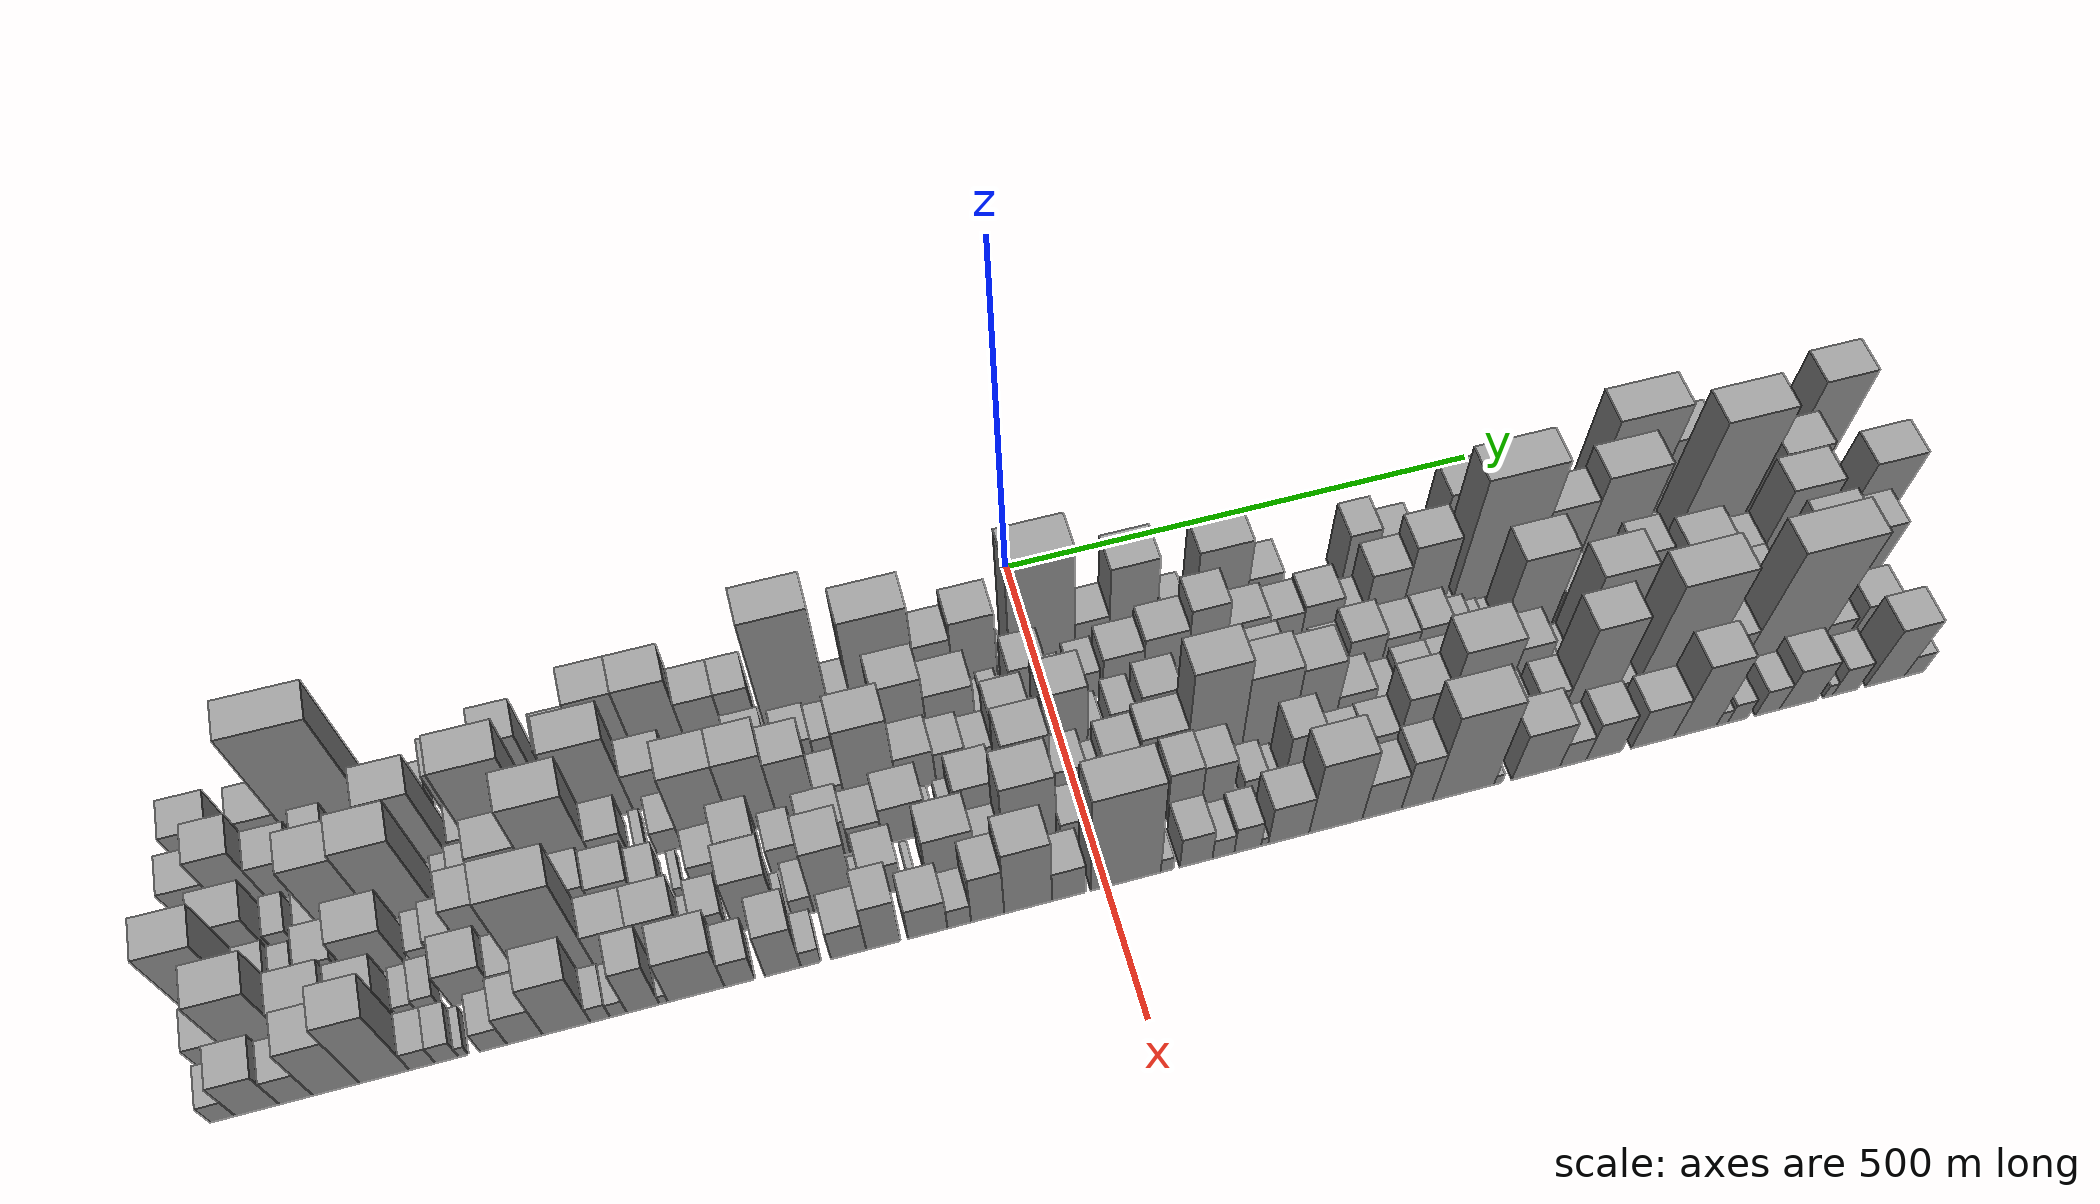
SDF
<sdf version="1.6">
 <world name="default">
  <scene>
   <sky><clouds><speed>12</speed></clouds></sky>
   <ambient>0.4 0.4 0.4 1</ambient>
   <background>0.7 0.7 0.7 1</background>
   <shadows>1</shadows>
  </scene>
  <gravity>0 0 -9.8066</gravity>
  <magnetic_field>6e-06 2.3e-05 -4.2e-05</magnetic_field>
  <physics default="0" name="default_physics" type="ode">
   <ode>
    <solver>
     <type>quick</type>
     <iters>10</iters>
     <sor>1.0</sor>
     <use_dynamic_moi_rescaling>0</use_dynamic_moi_rescaling>
    </solver>
    <constraints>
     <cfm>0</cfm>
     <erp>0.2</erp>
     <contact_max_correcting_vel>100</contact_max_correcting_vel>
     <contact_surface_layer>0.001</contact_surface_layer>
    </constraints>
   </ode>
   <max_step_size>0.004</max_step_size>
   <real_time_factor>1</real_time_factor>
   <real_time_update_rate>250</real_time_update_rate>
  </physics>
  <light name="sun" type="directional">
   <pose>0 0 10 0 0 0</pose>
   <diffuse>0.8 0.8 0.8 1</diffuse>
   <specular>0.2 0.2 0.2 1</specular>
   <attenuation>
    <range>1000</range>
    <constant>0.9</constant>
    <linear>0.01</linear>
    <quadratic>0.001</quadratic>
   </attenuation>
   <direction>-0.5 0.1 -0.9</direction>
  </light>
  <model name="building_1">
   <static>1</static>
   <pose>100.0000 -800.0666 0 0.000000 0.000000 0.000000</pose>
   <link name="link">
    <pose>0 0 40.50 0 0 0</pose>
    <collision name="collision"><geometry><box><size>40.0000 41.8669 81.0000</size></box></geometry></collision>
    <visual name="visual">
     <cast_shadows>0</cast_shadows>
     <geometry><box><size>40.0000 41.8669 81.0000</size></box></geometry>
     <material>
      <script>
       <uri>model://grey_wall/materials/scripts</uri>
       <uri>model://grey_wall/materials/textures</uri>
       <name>vrc/grey_wall</name>
      </script>
     </material>
    </visual>
   </link>
  </model>
  <model name="building_2">
   <static>1</static>
   <pose>100.0000 -772.9464 0 0.000000 0.000000 0.000000</pose>
   <link name="link">
    <pose>0 0 13.50 0 0 0</pose>
    <collision name="collision"><geometry><box><size>40.0000 12.3734 27.0000</size></box></geometry></collision>
    <visual name="visual">
     <cast_shadows>0</cast_shadows>
     <geometry><box><size>40.0000 12.3734 27.0000</size></box></geometry>
     <material>
      <script>
       <uri>model://grey_wall/materials/scripts</uri>
       <uri>model://grey_wall/materials/textures</uri>
       <name>vrc/grey_wall</name>
      </script>
     </material>
    </visual>
   </link>
  </model>
  <model name="building_3">
   <static>1</static>
   <pose>100.0000 -741.5910 0 0.000000 0.000000 0.000000</pose>
   <link name="link">
    <pose>0 0 37.50 0 0 0</pose>
    <collision name="collision"><geometry><box><size>40.0000 42.3374 75.0000</size></box></geometry></collision>
    <visual name="visual">
     <cast_shadows>0</cast_shadows>
     <geometry><box><size>40.0000 42.3374 75.0000</size></box></geometry>
     <material>
      <script>
       <uri>model://grey_wall/materials/scripts</uri>
       <uri>model://grey_wall/materials/textures</uri>
       <name>vrc/grey_wall</name>
      </script>
     </material>
    </visual>
   </link>
  </model>
  <model name="building_4">
   <static>1</static>
   <pose>100.0000 -681.8136 0 0.000000 0.000000 0.000000</pose>
   <link name="link">
    <pose>0 0 111.00 0 0 0</pose>
    <collision name="collision"><geometry><box><size>40.0000 77.2175 222.0000</size></box></geometry></collision>
    <visual name="visual">
     <cast_shadows>0</cast_shadows>
     <geometry><box><size>40.0000 77.2175 222.0000</size></box></geometry>
     <material>
      <script>
       <uri>model://grey_wall/materials/scripts</uri>
       <uri>model://grey_wall/materials/textures</uri>
       <name>vrc/grey_wall</name>
      </script>
     </material>
    </visual>
   </link>
  </model>
  <model name="building_5">
   <static>1</static>
   <pose>100.0000 -633.0652 0 0.000000 0.000000 0.000000</pose>
   <link name="link">
    <pose>0 0 18.00 0 0 0</pose>
    <collision name="collision"><geometry><box><size>40.0000 20.2793 36.0000</size></box></geometry></collision>
    <visual name="visual">
     <cast_shadows>0</cast_shadows>
     <geometry><box><size>40.0000 20.2793 36.0000</size></box></geometry>
     <material>
      <script>
       <uri>model://grey_wall/materials/scripts</uri>
       <uri>model://grey_wall/materials/textures</uri>
       <name>vrc/grey_wall</name>
      </script>
     </material>
    </visual>
   </link>
  </model>
  <model name="building_6">
   <static>1</static>
   <pose>100.0000 -603.3383 0 0.000000 0.000000 0.000000</pose>
   <link name="link">
    <pose>0 0 19.50 0 0 0</pose>
    <collision name="collision"><geometry><box><size>40.0000 21.1745 39.0000</size></box></geometry></collision>
    <visual name="visual">
     <cast_shadows>0</cast_shadows>
     <geometry><box><size>40.0000 21.1745 39.0000</size></box></geometry>
     <material>
      <script>
       <uri>model://grey_wall/materials/scripts</uri>
       <uri>model://grey_wall/materials/textures</uri>
       <name>vrc/grey_wall</name>
      </script>
     </material>
    </visual>
   </link>
  </model>
  <model name="building_7">
   <static>1</static>
   <pose>100.0000 -564.9898 0 0.000000 0.000000 0.000000</pose>
   <link name="link">
    <pose>0 0 39.00 0 0 0</pose>
    <collision name="collision"><geometry><box><size>40.0000 41.5226 78.0000</size></box></geometry></collision>
    <visual name="visual">
     <cast_shadows>0</cast_shadows>
     <geometry><box><size>40.0000 41.5226 78.0000</size></box></geometry>
     <material>
      <script>
       <uri>model://grey_wall/materials/scripts</uri>
       <uri>model://grey_wall/materials/textures</uri>
       <name>vrc/grey_wall</name>
      </script>
     </material>
    </visual>
   </link>
  </model>
  <model name="building_8">
   <static>1</static>
   <pose>100.0000 -538.1103 0 0.000000 0.000000 0.000000</pose>
   <link name="link">
    <pose>0 0 13.50 0 0 0</pose>
    <collision name="collision"><geometry><box><size>40.0000 12.2365 27.0000</size></box></geometry></collision>
    <visual name="visual">
     <cast_shadows>0</cast_shadows>
     <geometry><box><size>40.0000 12.2365 27.0000</size></box></geometry>
     <material>
      <script>
       <uri>model://grey_wall/materials/scripts</uri>
       <uri>model://grey_wall/materials/textures</uri>
       <name>vrc/grey_wall</name>
      </script>
     </material>
    </visual>
   </link>
  </model>
  <model name="building_9">
   <static>1</static>
   <pose>100.0000 -512.1156 0 0.000000 0.000000 0.000000</pose>
   <link name="link">
    <pose>0 0 55.50 0 0 0</pose>
    <collision name="collision"><geometry><box><size>40.0000 39.7527 111.0000</size></box></geometry></collision>
    <visual name="visual">
     <cast_shadows>0</cast_shadows>
     <geometry><box><size>40.0000 39.7527 111.0000</size></box></geometry>
     <material>
      <script>
       <uri>model://grey_wall/materials/scripts</uri>
       <uri>model://grey_wall/materials/textures</uri>
       <name>vrc/grey_wall</name>
      </script>
     </material>
    </visual>
   </link>
  </model>
  <model name="building_10">
   <static>1</static>
   <pose>100.0000 -462.4981 0 0.000000 0.000000 0.000000</pose>
   <link name="link">
    <pose>0 0 37.50 0 0 0</pose>
    <collision name="collision"><geometry><box><size>40.0000 41.4823 75.0000</size></box></geometry></collision>
    <visual name="visual">
     <cast_shadows>0</cast_shadows>
     <geometry><box><size>40.0000 41.4823 75.0000</size></box></geometry>
     <material>
      <script>
       <uri>model://grey_wall/materials/scripts</uri>
       <uri>model://grey_wall/materials/textures</uri>
       <name>vrc/grey_wall</name>
      </script>
     </material>
    </visual>
   </link>
  </model>
  <model name="building_11">
   <static>1</static>
   <pose>100.0000 -419.6553 0 0.000000 0.000000 0.000000</pose>
   <link name="link">
    <pose>0 0 72.00 0 0 0</pose>
    <collision name="collision"><geometry><box><size>40.0000 44.2034 144.0000</size></box></geometry></collision>
    <visual name="visual">
     <cast_shadows>0</cast_shadows>
     <geometry><box><size>40.0000 44.2034 144.0000</size></box></geometry>
     <material>
      <script>
       <uri>model://grey_wall/materials/scripts</uri>
       <uri>model://grey_wall/materials/textures</uri>
       <name>vrc/grey_wall</name>
      </script>
     </material>
    </visual>
   </link>
  </model>
  <model name="building_12">
   <static>1</static>
   <pose>100.0000 -373.0268 0 0.000000 0.000000 0.000000</pose>
   <link name="link">
    <pose>0 0 72.00 0 0 0</pose>
    <collision name="collision"><geometry><box><size>40.0000 49.0535 144.0000</size></box></geometry></collision>
    <visual name="visual">
     <cast_shadows>0</cast_shadows>
     <geometry><box><size>40.0000 49.0535 144.0000</size></box></geometry>
     <material>
      <script>
       <uri>model://grey_wall/materials/scripts</uri>
       <uri>model://grey_wall/materials/textures</uri>
       <name>vrc/grey_wall</name>
      </script>
     </material>
    </visual>
   </link>
  </model>
  <model name="building_13">
   <static>1</static>
   <pose>100.0000 -329.8094 0 0.000000 0.000000 0.000000</pose>
   <link name="link">
    <pose>0 0 48.00 0 0 0</pose>
    <collision name="collision"><geometry><box><size>40.0000 37.3814 96.0000</size></box></geometry></collision>
    <visual name="visual">
     <cast_shadows>0</cast_shadows>
     <geometry><box><size>40.0000 37.3814 96.0000</size></box></geometry>
     <material>
      <script>
       <uri>model://grey_wall/materials/scripts</uri>
       <uri>model://grey_wall/materials/textures</uri>
       <name>vrc/grey_wall</name>
      </script>
     </material>
    </visual>
   </link>
  </model>
  <model name="building_14">
   <static>1</static>
   <pose>100.0000 -295.0552 0 0.000000 0.000000 0.000000</pose>
   <link name="link">
    <pose>0 0 48.00 0 0 0</pose>
    <collision name="collision"><geometry><box><size>40.0000 32.1269 96.0000</size></box></geometry></collision>
    <visual name="visual">
     <cast_shadows>0</cast_shadows>
     <geometry><box><size>40.0000 32.1269 96.0000</size></box></geometry>
     <material>
      <script>
       <uri>model://grey_wall/materials/scripts</uri>
       <uri>model://grey_wall/materials/textures</uri>
       <name>vrc/grey_wall</name>
      </script>
     </material>
    </visual>
   </link>
  </model>
  <model name="building_15">
   <static>1</static>
   <pose>100.0000 -240.8266 0 0.000000 0.000000 0.000000</pose>
   <link name="link">
    <pose>0 0 103.50 0 0 0</pose>
    <collision name="collision"><geometry><box><size>40.0000 64.3303 207.0000</size></box></geometry></collision>
    <visual name="visual">
     <cast_shadows>0</cast_shadows>
     <geometry><box><size>40.0000 64.3303 207.0000</size></box></geometry>
     <material>
      <script>
       <uri>model://grey_wall/materials/scripts</uri>
       <uri>model://grey_wall/materials/textures</uri>
       <name>vrc/grey_wall</name>
      </script>
     </material>
    </visual>
   </link>
  </model>
  <model name="building_16">
   <static>1</static>
   <pose>100.0000 -197.7018 0 0.000000 0.000000 0.000000</pose>
   <link name="link">
    <pose>0 0 19.50 0 0 0</pose>
    <collision name="collision"><geometry><box><size>40.0000 21.9192 39.0000</size></box></geometry></collision>
    <visual name="visual">
     <cast_shadows>0</cast_shadows>
     <geometry><box><size>40.0000 21.9192 39.0000</size></box></geometry>
     <material>
      <script>
       <uri>model://grey_wall/materials/scripts</uri>
       <uri>model://grey_wall/materials/textures</uri>
       <name>vrc/grey_wall</name>
      </script>
     </material>
    </visual>
   </link>
  </model>
  <model name="building_17">
   <static>1</static>
   <pose>100.0000 -153.9231 0 0.000000 0.000000 0.000000</pose>
   <link name="link">
    <pose>0 0 84.00 0 0 0</pose>
    <collision name="collision"><geometry><box><size>40.0000 65.6383 168.0000</size></box></geometry></collision>
    <visual name="visual">
     <cast_shadows>0</cast_shadows>
     <geometry><box><size>40.0000 65.6383 168.0000</size></box></geometry>
     <material>
      <script>
       <uri>model://grey_wall/materials/scripts</uri>
       <uri>model://grey_wall/materials/textures</uri>
       <name>vrc/grey_wall</name>
      </script>
     </material>
    </visual>
   </link>
  </model>
  <model name="building_18">
   <static>1</static>
   <pose>100.0000 -102.9866 0 0.000000 0.000000 0.000000</pose>
   <link name="link">
    <pose>0 0 46.50 0 0 0</pose>
    <collision name="collision"><geometry><box><size>40.0000 36.2348 93.0000</size></box></geometry></collision>
    <visual name="visual">
     <cast_shadows>0</cast_shadows>
     <geometry><box><size>40.0000 36.2348 93.0000</size></box></geometry>
     <material>
      <script>
       <uri>model://grey_wall/materials/scripts</uri>
       <uri>model://grey_wall/materials/textures</uri>
       <name>vrc/grey_wall</name>
      </script>
     </material>
    </visual>
   </link>
  </model>
  <model name="building_19">
   <static>1</static>
   <pose>100.0000 -62.6117 0 0.000000 0.000000 0.000000</pose>
   <link name="link">
    <pose>0 0 60.00 0 0 0</pose>
    <collision name="collision"><geometry><box><size>40.0000 44.5149 120.0000</size></box></geometry></collision>
    <visual name="visual">
     <cast_shadows>0</cast_shadows>
     <geometry><box><size>40.0000 44.5149 120.0000</size></box></geometry>
     <material>
      <script>
       <uri>model://grey_wall/materials/scripts</uri>
       <uri>model://grey_wall/materials/textures</uri>
       <name>vrc/grey_wall</name>
      </script>
     </material>
    </visual>
   </link>
  </model>
  <model name="building_20">
   <static>1</static>
   <pose>100.0000 -35.6186 0 0.000000 0.000000 0.000000</pose>
   <link name="link">
    <pose>0 0 10.50 0 0 0</pose>
    <collision name="collision"><geometry><box><size>40.0000 9.4714 21.0000</size></box></geometry></collision>
    <visual name="visual">
     <cast_shadows>0</cast_shadows>
     <geometry><box><size>40.0000 9.4714 21.0000</size></box></geometry>
     <material>
      <script>
       <uri>model://grey_wall/materials/scripts</uri>
       <uri>model://grey_wall/materials/textures</uri>
       <name>vrc/grey_wall</name>
      </script>
     </material>
    </visual>
   </link>
  </model>
  <model name="building_21">
   <static>1</static>
   <pose>100.0000 5.5704 0 0.000000 0.000000 0.000000</pose>
   <link name="link">
    <pose>0 0 100.50 0 0 0</pose>
    <collision name="collision"><geometry><box><size>40.0000 66.9066 201.0000</size></box></geometry></collision>
    <visual name="visual">
     <cast_shadows>0</cast_shadows>
     <geometry><box><size>40.0000 66.9066 201.0000</size></box></geometry>
     <material>
      <script>
       <uri>model://grey_wall/materials/scripts</uri>
       <uri>model://grey_wall/materials/textures</uri>
       <name>vrc/grey_wall</name>
      </script>
     </material>
    </visual>
   </link>
  </model>
  <model name="building_22">
   <static>1</static>
   <pose>100.0000 56.5066 0 0.000000 0.000000 0.000000</pose>
   <link name="link">
    <pose>0 0 31.50 0 0 0</pose>
    <collision name="collision"><geometry><box><size>40.0000 34.9657 63.0000</size></box></geometry></collision>
    <visual name="visual">
     <cast_shadows>0</cast_shadows>
     <geometry><box><size>40.0000 34.9657 63.0000</size></box></geometry>
     <material>
      <script>
       <uri>model://grey_wall/materials/scripts</uri>
       <uri>model://grey_wall/materials/textures</uri>
       <name>vrc/grey_wall</name>
      </script>
     </material>
    </visual>
   </link>
  </model>
  <model name="building_23">
   <static>1</static>
   <pose>100.0000 98.3546 0 0.000000 0.000000 0.000000</pose>
   <link name="link">
    <pose>0 0 73.50 0 0 0</pose>
    <collision name="collision"><geometry><box><size>40.0000 48.7302 147.0000</size></box></geometry></collision>
    <visual name="visual">
     <cast_shadows>0</cast_shadows>
     <geometry><box><size>40.0000 48.7302 147.0000</size></box></geometry>
     <material>
      <script>
       <uri>model://grey_wall/materials/scripts</uri>
       <uri>model://grey_wall/materials/textures</uri>
       <name>vrc/grey_wall</name>
      </script>
     </material>
    </visual>
   </link>
  </model>
  <model name="building_24">
   <static>1</static>
   <pose>100.0000 141.8501 0 0.000000 0.000000 0.000000</pose>
   <link name="link">
    <pose>0 0 24.00 0 0 0</pose>
    <collision name="collision"><geometry><box><size>40.0000 24.2610 48.0000</size></box></geometry></collision>
    <visual name="visual">
     <cast_shadows>0</cast_shadows>
     <geometry><box><size>40.0000 24.2610 48.0000</size></box></geometry>
     <material>
      <script>
       <uri>model://grey_wall/materials/scripts</uri>
       <uri>model://grey_wall/materials/textures</uri>
       <name>vrc/grey_wall</name>
      </script>
     </material>
    </visual>
   </link>
  </model>
  <model name="building_25">
   <static>1</static>
   <pose>100.0000 189.0597 0 0.000000 0.000000 0.000000</pose>
   <link name="link">
    <pose>0 0 69.00 0 0 0</pose>
    <collision name="collision"><geometry><box><size>40.0000 54.1582 138.0000</size></box></geometry></collision>
    <visual name="visual">
     <cast_shadows>0</cast_shadows>
     <geometry><box><size>40.0000 54.1582 138.0000</size></box></geometry>
     <material>
      <script>
       <uri>model://grey_wall/materials/scripts</uri>
       <uri>model://grey_wall/materials/textures</uri>
       <name>vrc/grey_wall</name>
      </script>
     </material>
    </visual>
   </link>
  </model>
  <model name="building_26">
   <static>1</static>
   <pose>100.0000 234.2118 0 0.000000 0.000000 0.000000</pose>
   <link name="link">
    <pose>0 0 33.00 0 0 0</pose>
    <collision name="collision"><geometry><box><size>40.0000 36.1460 66.0000</size></box></geometry></collision>
    <visual name="visual">
     <cast_shadows>0</cast_shadows>
     <geometry><box><size>40.0000 36.1460 66.0000</size></box></geometry>
     <material>
      <script>
       <uri>model://grey_wall/materials/scripts</uri>
       <uri>model://grey_wall/materials/textures</uri>
       <name>vrc/grey_wall</name>
      </script>
     </material>
    </visual>
   </link>
  </model>
  <model name="building_27">
   <static>1</static>
   <pose>100.0000 333.4423 0 0.000000 0.000000 0.000000</pose>
   <link name="link">
    <pose>0 0 51.00 0 0 0</pose>
    <collision name="collision"><geometry><box><size>40.0000 32.7717 102.0000</size></box></geometry></collision>
    <visual name="visual">
     <cast_shadows>0</cast_shadows>
     <geometry><box><size>40.0000 32.7717 102.0000</size></box></geometry>
     <material>
      <script>
       <uri>model://grey_wall/materials/scripts</uri>
       <uri>model://grey_wall/materials/textures</uri>
       <name>vrc/grey_wall</name>
      </script>
     </material>
    </visual>
   </link>
  </model>
  <model name="building_28">
   <static>1</static>
   <pose>100.0000 369.4874 0 0.000000 0.000000 0.000000</pose>
   <link name="link">
    <pose>0 0 37.50 0 0 0</pose>
    <collision name="collision"><geometry><box><size>40.0000 39.3185 75.0000</size></box></geometry></collision>
    <visual name="visual">
     <cast_shadows>0</cast_shadows>
     <geometry><box><size>40.0000 39.3185 75.0000</size></box></geometry>
     <material>
      <script>
       <uri>model://grey_wall/materials/scripts</uri>
       <uri>model://grey_wall/materials/textures</uri>
       <name>vrc/grey_wall</name>
      </script>
     </material>
    </visual>
   </link>
  </model>
  <model name="building_29">
   <static>1</static>
   <pose>100.0000 402.8128 0 0.000000 0.000000 0.000000</pose>
   <link name="link">
    <pose>0 0 24.00 0 0 0</pose>
    <collision name="collision"><geometry><box><size>40.0000 27.3323 48.0000</size></box></geometry></collision>
    <visual name="visual">
     <cast_shadows>0</cast_shadows>
     <geometry><box><size>40.0000 27.3323 48.0000</size></box></geometry>
     <material>
      <script>
       <uri>model://grey_wall/materials/scripts</uri>
       <uri>model://grey_wall/materials/textures</uri>
       <name>vrc/grey_wall</name>
      </script>
     </material>
    </visual>
   </link>
  </model>
  <model name="building_30">
   <static>1</static>
   <pose>100.0000 438.0873 0 0.000000 0.000000 0.000000</pose>
   <link name="link">
    <pose>0 0 66.00 0 0 0</pose>
    <collision name="collision"><geometry><box><size>40.0000 43.2168 132.0000</size></box></geometry></collision>
    <visual name="visual">
     <cast_shadows>0</cast_shadows>
     <geometry><box><size>40.0000 43.2168 132.0000</size></box></geometry>
     <material>
      <script>
       <uri>model://grey_wall/materials/scripts</uri>
       <uri>model://grey_wall/materials/textures</uri>
       <name>vrc/grey_wall</name>
      </script>
     </material>
    </visual>
   </link>
  </model>
  <model name="building_31">
   <static>1</static>
   <pose>100.0000 482.3826 0 0.000000 0.000000 0.000000</pose>
   <link name="link">
    <pose>0 0 42.00 0 0 0</pose>
    <collision name="collision"><geometry><box><size>40.0000 45.3738 84.0000</size></box></geometry></collision>
    <visual name="visual">
     <cast_shadows>0</cast_shadows>
     <geometry><box><size>40.0000 45.3738 84.0000</size></box></geometry>
     <material>
      <script>
       <uri>model://grey_wall/materials/scripts</uri>
       <uri>model://grey_wall/materials/textures</uri>
       <name>vrc/grey_wall</name>
      </script>
     </material>
    </visual>
   </link>
  </model>
  <model name="building_32">
   <static>1</static>
   <pose>100.0000 525.3424 0 0.000000 0.000000 0.000000</pose>
   <link name="link">
    <pose>0 0 52.50 0 0 0</pose>
    <collision name="collision"><geometry><box><size>40.0000 40.5458 105.0000</size></box></geometry></collision>
    <visual name="visual">
     <cast_shadows>0</cast_shadows>
     <geometry><box><size>40.0000 40.5458 105.0000</size></box></geometry>
     <material>
      <script>
       <uri>model://grey_wall/materials/scripts</uri>
       <uri>model://grey_wall/materials/textures</uri>
       <name>vrc/grey_wall</name>
      </script>
     </material>
    </visual>
   </link>
  </model>
  <model name="building_33">
   <static>1</static>
   <pose>100.0000 561.0534 0 0.000000 0.000000 0.000000</pose>
   <link name="link">
    <pose>0 0 18.00 0 0 0</pose>
    <collision name="collision"><geometry><box><size>40.0000 18.8762 36.0000</size></box></geometry></collision>
    <visual name="visual">
     <cast_shadows>0</cast_shadows>
     <geometry><box><size>40.0000 18.8762 36.0000</size></box></geometry>
     <material>
      <script>
       <uri>model://grey_wall/materials/scripts</uri>
       <uri>model://grey_wall/materials/textures</uri>
       <name>vrc/grey_wall</name>
      </script>
     </material>
    </visual>
   </link>
  </model>
  <model name="building_34">
   <static>1</static>
   <pose>100.0000 614.4144 0 0.000000 0.000000 0.000000</pose>
   <link name="link">
    <pose>0 0 96.00 0 0 0</pose>
    <collision name="collision"><geometry><box><size>40.0000 75.8458 192.0000</size></box></geometry></collision>
    <visual name="visual">
     <cast_shadows>0</cast_shadows>
     <geometry><box><size>40.0000 75.8458 192.0000</size></box></geometry>
     <material>
      <script>
       <uri>model://grey_wall/materials/scripts</uri>
       <uri>model://grey_wall/materials/textures</uri>
       <name>vrc/grey_wall</name>
      </script>
     </material>
    </visual>
   </link>
  </model>
  <model name="building_35">
   <static>1</static>
   <pose>100.0000 674.1312 0 0.000000 0.000000 0.000000</pose>
   <link name="link">
    <pose>0 0 66.00 0 0 0</pose>
    <collision name="collision"><geometry><box><size>40.0000 43.5878 132.0000</size></box></geometry></collision>
    <visual name="visual">
     <cast_shadows>0</cast_shadows>
     <geometry><box><size>40.0000 43.5878 132.0000</size></box></geometry>
     <material>
      <script>
       <uri>model://grey_wall/materials/scripts</uri>
       <uri>model://grey_wall/materials/textures</uri>
       <name>vrc/grey_wall</name>
      </script>
     </material>
    </visual>
   </link>
  </model>
  <model name="building_36">
   <static>1</static>
   <pose>100.0000 713.1540 0 0.000000 0.000000 0.000000</pose>
   <link name="link">
    <pose>0 0 48.00 0 0 0</pose>
    <collision name="collision"><geometry><box><size>40.0000 34.4577 96.0000</size></box></geometry></collision>
    <visual name="visual">
     <cast_shadows>0</cast_shadows>
     <geometry><box><size>40.0000 34.4577 96.0000</size></box></geometry>
     <material>
      <script>
       <uri>model://grey_wall/materials/scripts</uri>
       <uri>model://grey_wall/materials/textures</uri>
       <name>vrc/grey_wall</name>
      </script>
     </material>
    </visual>
   </link>
  </model>
  <model name="building_37">
   <static>1</static>
   <pose>100.0000 749.8381 0 0.000000 0.000000 0.000000</pose>
   <link name="link">
    <pose>0 0 36.00 0 0 0</pose>
    <collision name="collision"><geometry><box><size>40.0000 38.9105 72.0000</size></box></geometry></collision>
    <visual name="visual">
     <cast_shadows>0</cast_shadows>
     <geometry><box><size>40.0000 38.9105 72.0000</size></box></geometry>
     <material>
      <script>
       <uri>model://grey_wall/materials/scripts</uri>
       <uri>model://grey_wall/materials/textures</uri>
       <name>vrc/grey_wall</name>
      </script>
     </material>
    </visual>
   </link>
  </model>
  <model name="building_38">
   <static>1</static>
   <pose>100.0000 778.4212 0 0.000000 0.000000 0.000000</pose>
   <link name="link">
    <pose>0 0 16.50 0 0 0</pose>
    <collision name="collision"><geometry><box><size>40.0000 18.2558 33.0000</size></box></geometry></collision>
    <visual name="visual">
     <cast_shadows>0</cast_shadows>
     <geometry><box><size>40.0000 18.2558 33.0000</size></box></geometry>
     <material>
      <script>
       <uri>model://grey_wall/materials/scripts</uri>
       <uri>model://grey_wall/materials/textures</uri>
       <name>vrc/grey_wall</name>
      </script>
     </material>
    </visual>
   </link>
  </model>
  <model name="building_39">
   <static>1</static>
   <pose>100.0000 824.4427 0 0.000000 0.000000 0.000000</pose>
   <link name="link">
    <pose>0 0 87.00 0 0 0</pose>
    <collision name="collision"><geometry><box><size>40.0000 55.7872 174.0000</size></box></geometry></collision>
    <visual name="visual">
     <cast_shadows>0</cast_shadows>
     <geometry><box><size>40.0000 55.7872 174.0000</size></box></geometry>
     <material>
      <script>
       <uri>model://grey_wall/materials/scripts</uri>
       <uri>model://grey_wall/materials/textures</uri>
       <name>vrc/grey_wall</name>
      </script>
     </material>
    </visual>
   </link>
  </model>
  <model name="building_40">
   <static>1</static>
   <pose>149.0000 -810.1917 0 0.000000 0.000000 0.000000</pose>
   <link name="link">
    <pose>0 0 34.50 0 0 0</pose>
    <collision name="collision"><geometry><box><size>40.0000 39.6165 69.0000</size></box></geometry></collision>
    <visual name="visual">
     <cast_shadows>0</cast_shadows>
     <geometry><box><size>40.0000 39.6165 69.0000</size></box></geometry>
     <material>
      <script>
       <uri>model://grey_wall/materials/scripts</uri>
       <uri>model://grey_wall/materials/textures</uri>
       <name>vrc/grey_wall</name>
      </script>
     </material>
    </visual>
   </link>
  </model>
  <model name="building_41">
   <static>1</static>
   <pose>149.0000 -770.7093 0 0.000000 0.000000 0.000000</pose>
   <link name="link">
    <pose>0 0 57.00 0 0 0</pose>
    <collision name="collision"><geometry><box><size>40.0000 39.3484 114.0000</size></box></geometry></collision>
    <visual name="visual">
     <cast_shadows>0</cast_shadows>
     <geometry><box><size>40.0000 39.3484 114.0000</size></box></geometry>
     <material>
      <script>
       <uri>model://grey_wall/materials/scripts</uri>
       <uri>model://grey_wall/materials/textures</uri>
       <name>vrc/grey_wall</name>
      </script>
     </material>
    </visual>
   </link>
  </model>
  <model name="building_42">
   <static>1</static>
   <pose>149.0000 -731.8525 0 0.000000 0.000000 0.000000</pose>
   <link name="link">
    <pose>0 0 37.50 0 0 0</pose>
    <collision name="collision"><geometry><box><size>40.0000 38.3653 75.0000</size></box></geometry></collision>
    <visual name="visual">
     <cast_shadows>0</cast_shadows>
     <geometry><box><size>40.0000 38.3653 75.0000</size></box></geometry>
     <material>
      <script>
       <uri>model://grey_wall/materials/scripts</uri>
       <uri>model://grey_wall/materials/textures</uri>
       <name>vrc/grey_wall</name>
      </script>
     </material>
    </visual>
   </link>
  </model>
  <model name="building_43">
   <static>1</static>
   <pose>149.0000 -688.6359 0 0.000000 0.000000 0.000000</pose>
   <link name="link">
    <pose>0 0 46.50 0 0 0</pose>
    <collision name="collision"><geometry><box><size>40.0000 28.0679 93.0000</size></box></geometry></collision>
    <visual name="visual">
     <cast_shadows>0</cast_shadows>
     <geometry><box><size>40.0000 28.0679 93.0000</size></box></geometry>
     <material>
      <script>
       <uri>model://grey_wall/materials/scripts</uri>
       <uri>model://grey_wall/materials/textures</uri>
       <name>vrc/grey_wall</name>
      </script>
     </material>
    </visual>
   </link>
  </model>
  <model name="building_44">
   <static>1</static>
   <pose>149.0000 -651.4638 0 0.000000 0.000000 0.000000</pose>
   <link name="link">
    <pose>0 0 27.00 0 0 0</pose>
    <collision name="collision"><geometry><box><size>40.0000 28.2765 54.0000</size></box></geometry></collision>
    <visual name="visual">
     <cast_shadows>0</cast_shadows>
     <geometry><box><size>40.0000 28.2765 54.0000</size></box></geometry>
     <material>
      <script>
       <uri>model://grey_wall/materials/scripts</uri>
       <uri>model://grey_wall/materials/textures</uri>
       <name>vrc/grey_wall</name>
      </script>
     </material>
    </visual>
   </link>
  </model>
  <model name="building_45">
   <static>1</static>
   <pose>149.0000 -610.1578 0 0.000000 0.000000 0.000000</pose>
   <link name="link">
    <pose>0 0 70.50 0 0 0</pose>
    <collision name="collision"><geometry><box><size>40.0000 48.3355 141.0000</size></box></geometry></collision>
    <visual name="visual">
     <cast_shadows>0</cast_shadows>
     <geometry><box><size>40.0000 48.3355 141.0000</size></box></geometry>
     <material>
      <script>
       <uri>model://grey_wall/materials/scripts</uri>
       <uri>model://grey_wall/materials/textures</uri>
       <name>vrc/grey_wall</name>
      </script>
     </material>
    </visual>
   </link>
  </model>
  <model name="building_46">
   <static>1</static>
   <pose>149.0000 -571.2518 0 0.000000 0.000000 0.000000</pose>
   <link name="link">
    <pose>0 0 16.50 0 0 0</pose>
    <collision name="collision"><geometry><box><size>40.0000 17.4767 33.0000</size></box></geometry></collision>
    <visual name="visual">
     <cast_shadows>0</cast_shadows>
     <geometry><box><size>40.0000 17.4767 33.0000</size></box></geometry>
     <material>
      <script>
       <uri>model://grey_wall/materials/scripts</uri>
       <uri>model://grey_wall/materials/textures</uri>
       <name>vrc/grey_wall</name>
      </script>
     </material>
    </visual>
   </link>
  </model>
  <model name="building_47">
   <static>1</static>
   <pose>149.0000 -531.8372 0 0.000000 0.000000 0.000000</pose>
   <link name="link">
    <pose>0 0 82.50 0 0 0</pose>
    <collision name="collision"><geometry><box><size>40.0000 61.3524 165.0000</size></box></geometry></collision>
    <visual name="visual">
     <cast_shadows>0</cast_shadows>
     <geometry><box><size>40.0000 61.3524 165.0000</size></box></geometry>
     <material>
      <script>
       <uri>model://grey_wall/materials/scripts</uri>
       <uri>model://grey_wall/materials/textures</uri>
       <name>vrc/grey_wall</name>
      </script>
     </material>
    </visual>
   </link>
  </model>
  <model name="building_48">
   <static>1</static>
   <pose>149.0000 -483.6819 0 0.000000 0.000000 0.000000</pose>
   <link name="link">
    <pose>0 0 25.50 0 0 0</pose>
    <collision name="collision"><geometry><box><size>40.0000 28.9581 51.0000</size></box></geometry></collision>
    <visual name="visual">
     <cast_shadows>0</cast_shadows>
     <geometry><box><size>40.0000 28.9581 51.0000</size></box></geometry>
     <material>
      <script>
       <uri>model://grey_wall/materials/scripts</uri>
       <uri>model://grey_wall/materials/textures</uri>
       <name>vrc/grey_wall</name>
      </script>
     </material>
    </visual>
   </link>
  </model>
  <model name="building_49">
   <static>1</static>
   <pose>149.0000 -440.0245 0 0.000000 0.000000 0.000000</pose>
   <link name="link">
    <pose>0 0 76.50 0 0 0</pose>
    <collision name="collision"><geometry><box><size>40.0000 58.3566 153.0000</size></box></geometry></collision>
    <visual name="visual">
     <cast_shadows>0</cast_shadows>
     <geometry><box><size>40.0000 58.3566 153.0000</size></box></geometry>
     <material>
      <script>
       <uri>model://grey_wall/materials/scripts</uri>
       <uri>model://grey_wall/materials/textures</uri>
       <name>vrc/grey_wall</name>
      </script>
     </material>
    </visual>
   </link>
  </model>
  <model name="building_50">
   <static>1</static>
   <pose>149.0000 -390.0981 0 0.000000 0.000000 0.000000</pose>
   <link name="link">
    <pose>0 0 37.50 0 0 0</pose>
    <collision name="collision"><geometry><box><size>40.0000 41.4963 75.0000</size></box></geometry></collision>
    <visual name="visual">
     <cast_shadows>0</cast_shadows>
     <geometry><box><size>40.0000 41.4963 75.0000</size></box></geometry>
     <material>
      <script>
       <uri>model://grey_wall/materials/scripts</uri>
       <uri>model://grey_wall/materials/textures</uri>
       <name>vrc/grey_wall</name>
      </script>
     </material>
    </visual>
   </link>
  </model>
  <model name="building_51">
   <static>1</static>
   <pose>149.0000 -362.1024 0 0.000000 0.000000 0.000000</pose>
   <link name="link">
    <pose>0 0 9.00 0 0 0</pose>
    <collision name="collision"><geometry><box><size>40.0000 8.4950 18.0000</size></box></geometry></collision>
    <visual name="visual">
     <cast_shadows>0</cast_shadows>
     <geometry><box><size>40.0000 8.4950 18.0000</size></box></geometry>
     <material>
      <script>
       <uri>model://grey_wall/materials/scripts</uri>
       <uri>model://grey_wall/materials/textures</uri>
       <name>vrc/grey_wall</name>
      </script>
     </material>
    </visual>
   </link>
  </model>
  <model name="building_52">
   <static>1</static>
   <pose>149.0000 -341.7077 0 0.000000 0.000000 0.000000</pose>
   <link name="link">
    <pose>0 0 22.50 0 0 0</pose>
    <collision name="collision"><geometry><box><size>40.0000 26.2945 45.0000</size></box></geometry></collision>
    <visual name="visual">
     <cast_shadows>0</cast_shadows>
     <geometry><box><size>40.0000 26.2945 45.0000</size></box></geometry>
     <material>
      <script>
       <uri>model://grey_wall/materials/scripts</uri>
       <uri>model://grey_wall/materials/textures</uri>
       <name>vrc/grey_wall</name>
      </script>
     </material>
    </visual>
   </link>
  </model>
  <model name="building_53">
   <static>1</static>
   <pose>149.0000 -319.5899 0 0.000000 0.000000 0.000000</pose>
   <link name="link">
    <pose>0 0 16.50 0 0 0</pose>
    <collision name="collision"><geometry><box><size>40.0000 17.9410 33.0000</size></box></geometry></collision>
    <visual name="visual">
     <cast_shadows>0</cast_shadows>
     <geometry><box><size>40.0000 17.9410 33.0000</size></box></geometry>
     <material>
      <script>
       <uri>model://grey_wall/materials/scripts</uri>
       <uri>model://grey_wall/materials/textures</uri>
       <name>vrc/grey_wall</name>
      </script>
     </material>
    </visual>
   </link>
  </model>
  <model name="building_54">
   <static>1</static>
   <pose>149.0000 -292.4086 0 0.000000 0.000000 0.000000</pose>
   <link name="link">
    <pose>0 0 36.00 0 0 0</pose>
    <collision name="collision"><geometry><box><size>40.0000 36.4217 72.0000</size></box></geometry></collision>
    <visual name="visual">
     <cast_shadows>0</cast_shadows>
     <geometry><box><size>40.0000 36.4217 72.0000</size></box></geometry>
     <material>
      <script>
       <uri>model://grey_wall/materials/scripts</uri>
       <uri>model://grey_wall/materials/textures</uri>
       <name>vrc/grey_wall</name>
      </script>
     </material>
    </visual>
   </link>
  </model>
  <model name="building_55">
   <static>1</static>
   <pose>149.0000 -270.7496 0 0.000000 0.000000 0.000000</pose>
   <link name="link">
    <pose>0 0 7.50 0 0 0</pose>
    <collision name="collision"><geometry><box><size>40.0000 6.8963 15.0000</size></box></geometry></collision>
    <visual name="visual">
     <cast_shadows>0</cast_shadows>
     <geometry><box><size>40.0000 6.8963 15.0000</size></box></geometry>
     <material>
      <script>
       <uri>model://grey_wall/materials/scripts</uri>
       <uri>model://grey_wall/materials/textures</uri>
       <name>vrc/grey_wall</name>
      </script>
     </material>
    </visual>
   </link>
  </model>
  <model name="building_56">
   <static>1</static>
   <pose>149.0000 -250.5568 0 0.000000 0.000000 0.000000</pose>
   <link name="link">
    <pose>0 0 30.00 0 0 0</pose>
    <collision name="collision"><geometry><box><size>40.0000 33.4891 60.0000</size></box></geometry></collision>
    <visual name="visual">
     <cast_shadows>0</cast_shadows>
     <geometry><box><size>40.0000 33.4891 60.0000</size></box></geometry>
     <material>
      <script>
       <uri>model://grey_wall/materials/scripts</uri>
       <uri>model://grey_wall/materials/textures</uri>
       <name>vrc/grey_wall</name>
      </script>
     </material>
    </visual>
   </link>
  </model>
  <model name="building_57">
   <static>1</static>
   <pose>149.0000 -218.5528 0 0.000000 0.000000 0.000000</pose>
   <link name="link">
    <pose>0 0 27.00 0 0 0</pose>
    <collision name="collision"><geometry><box><size>40.0000 30.5189 54.0000</size></box></geometry></collision>
    <visual name="visual">
     <cast_shadows>0</cast_shadows>
     <geometry><box><size>40.0000 30.5189 54.0000</size></box></geometry>
     <material>
      <script>
       <uri>model://grey_wall/materials/scripts</uri>
       <uri>model://grey_wall/materials/textures</uri>
       <name>vrc/grey_wall</name>
      </script>
     </material>
    </visual>
   </link>
  </model>
  <model name="building_58">
   <static>1</static>
   <pose>149.0000 -186.6593 0 0.000000 0.000000 0.000000</pose>
   <link name="link">
    <pose>0 0 28.50 0 0 0</pose>
    <collision name="collision"><geometry><box><size>40.0000 33.2682 57.0000</size></box></geometry></collision>
    <visual name="visual">
     <cast_shadows>0</cast_shadows>
     <geometry><box><size>40.0000 33.2682 57.0000</size></box></geometry>
     <material>
      <script>
       <uri>model://grey_wall/materials/scripts</uri>
       <uri>model://grey_wall/materials/textures</uri>
       <name>vrc/grey_wall</name>
      </script>
     </material>
    </visual>
   </link>
  </model>
  <model name="building_59">
   <static>1</static>
   <pose>149.0000 -146.6231 0 0.000000 0.000000 0.000000</pose>
   <link name="link">
    <pose>0 0 60.00 0 0 0</pose>
    <collision name="collision"><geometry><box><size>40.0000 46.8044 120.0000</size></box></geometry></collision>
    <visual name="visual">
     <cast_shadows>0</cast_shadows>
     <geometry><box><size>40.0000 46.8044 120.0000</size></box></geometry>
     <material>
      <script>
       <uri>model://grey_wall/materials/scripts</uri>
       <uri>model://grey_wall/materials/textures</uri>
       <name>vrc/grey_wall</name>
      </script>
     </material>
    </visual>
   </link>
  </model>
  <model name="building_60">
   <static>1</static>
   <pose>149.0000 -99.2421 0 0.000000 0.000000 0.000000</pose>
   <link name="link">
    <pose>0 0 42.00 0 0 0</pose>
    <collision name="collision"><geometry><box><size>40.0000 47.9576 84.0000</size></box></geometry></collision>
    <visual name="visual">
     <cast_shadows>0</cast_shadows>
     <geometry><box><size>40.0000 47.9576 84.0000</size></box></geometry>
     <material>
      <script>
       <uri>model://grey_wall/materials/scripts</uri>
       <uri>model://grey_wall/materials/textures</uri>
       <name>vrc/grey_wall</name>
      </script>
     </material>
    </visual>
   </link>
  </model>
  <model name="building_61">
   <static>1</static>
   <pose>149.0000 -70.0975 0 0.000000 0.000000 0.000000</pose>
   <link name="link">
    <pose>0 0 12.00 0 0 0</pose>
    <collision name="collision"><geometry><box><size>40.0000 10.3316 24.0000</size></box></geometry></collision>
    <visual name="visual">
     <cast_shadows>0</cast_shadows>
     <geometry><box><size>40.0000 10.3316 24.0000</size></box></geometry>
     <material>
      <script>
       <uri>model://grey_wall/materials/scripts</uri>
       <uri>model://grey_wall/materials/textures</uri>
       <name>vrc/grey_wall</name>
      </script>
     </material>
    </visual>
   </link>
  </model>
  <model name="building_62">
   <static>1</static>
   <pose>149.0000 -55.8874 0 0.000000 0.000000 0.000000</pose>
   <link name="link">
    <pose>0 0 18.00 0 0 0</pose>
    <collision name="collision"><geometry><box><size>40.0000 18.0885 36.0000</size></box></geometry></collision>
    <visual name="visual">
     <cast_shadows>0</cast_shadows>
     <geometry><box><size>40.0000 18.0885 36.0000</size></box></geometry>
     <material>
      <script>
       <uri>model://grey_wall/materials/scripts</uri>
       <uri>model://grey_wall/materials/textures</uri>
       <name>vrc/grey_wall</name>
      </script>
     </material>
    </visual>
   </link>
  </model>
  <model name="building_63">
   <static>1</static>
   <pose>149.0000 -21.5145 0 0.000000 0.000000 0.000000</pose>
   <link name="link">
    <pose>0 0 46.50 0 0 0</pose>
    <collision name="collision"><geometry><box><size>40.0000 36.6574 93.0000</size></box></geometry></collision>
    <visual name="visual">
     <cast_shadows>0</cast_shadows>
     <geometry><box><size>40.0000 36.6574 93.0000</size></box></geometry>
     <material>
      <script>
       <uri>model://grey_wall/materials/scripts</uri>
       <uri>model://grey_wall/materials/textures</uri>
       <name>vrc/grey_wall</name>
      </script>
     </material>
    </visual>
   </link>
  </model>
  <model name="building_64">
   <static>1</static>
   <pose>149.0000 6.7519 0 0.000000 0.000000 0.000000</pose>
   <link name="link">
    <pose>0 0 18.00 0 0 0</pose>
    <collision name="collision"><geometry><box><size>40.0000 19.8753 36.0000</size></box></geometry></collision>
    <visual name="visual">
     <cast_shadows>0</cast_shadows>
     <geometry><box><size>40.0000 19.8753 36.0000</size></box></geometry>
     <material>
      <script>
       <uri>model://grey_wall/materials/scripts</uri>
       <uri>model://grey_wall/materials/textures</uri>
       <name>vrc/grey_wall</name>
      </script>
     </material>
    </visual>
   </link>
  </model>
  <model name="building_65">
   <static>1</static>
   <pose>149.0000 36.0463 0 0.000000 0.000000 0.000000</pose>
   <link name="link">
    <pose>0 0 25.50 0 0 0</pose>
    <collision name="collision"><geometry><box><size>40.0000 28.7135 51.0000</size></box></geometry></collision>
    <visual name="visual">
     <cast_shadows>0</cast_shadows>
     <geometry><box><size>40.0000 28.7135 51.0000</size></box></geometry>
     <material>
      <script>
       <uri>model://grey_wall/materials/scripts</uri>
       <uri>model://grey_wall/materials/textures</uri>
       <name>vrc/grey_wall</name>
      </script>
     </material>
    </visual>
   </link>
  </model>
  <model name="building_66">
   <static>1</static>
   <pose>149.0000 74.0706 0 0.000000 0.000000 0.000000</pose>
   <link name="link">
    <pose>0 0 34.50 0 0 0</pose>
    <collision name="collision"><geometry><box><size>40.0000 41.3352 69.0000</size></box></geometry></collision>
    <visual name="visual">
     <cast_shadows>0</cast_shadows>
     <geometry><box><size>40.0000 41.3352 69.0000</size></box></geometry>
     <material>
      <script>
       <uri>model://grey_wall/materials/scripts</uri>
       <uri>model://grey_wall/materials/textures</uri>
       <name>vrc/grey_wall</name>
      </script>
     </material>
    </visual>
   </link>
  </model>
  <model name="building_67">
   <static>1</static>
   <pose>149.0000 117.2238 0 0.000000 0.000000 0.000000</pose>
   <link name="link">
    <pose>0 0 43.50 0 0 0</pose>
    <collision name="collision"><geometry><box><size>40.0000 44.9713 87.0000</size></box></geometry></collision>
    <visual name="visual">
     <cast_shadows>0</cast_shadows>
     <geometry><box><size>40.0000 44.9713 87.0000</size></box></geometry>
     <material>
      <script>
       <uri>model://grey_wall/materials/scripts</uri>
       <uri>model://grey_wall/materials/textures</uri>
       <name>vrc/grey_wall</name>
      </script>
     </material>
    </visual>
   </link>
  </model>
  <model name="building_68">
   <static>1</static>
   <pose>149.0000 159.1819 0 0.000000 0.000000 0.000000</pose>
   <link name="link">
    <pose>0 0 60.00 0 0 0</pose>
    <collision name="collision"><geometry><box><size>40.0000 38.9449 120.0000</size></box></geometry></collision>
    <visual name="visual">
     <cast_shadows>0</cast_shadows>
     <geometry><box><size>40.0000 38.9449 120.0000</size></box></geometry>
     <material>
      <script>
       <uri>model://grey_wall/materials/scripts</uri>
       <uri>model://grey_wall/materials/textures</uri>
       <name>vrc/grey_wall</name>
      </script>
     </material>
    </visual>
   </link>
  </model>
  <model name="building_69">
   <static>1</static>
   <pose>149.0000 200.0035 0 0.000000 0.000000 0.000000</pose>
   <link name="link">
    <pose>0 0 37.50 0 0 0</pose>
    <collision name="collision"><geometry><box><size>40.0000 42.6982 75.0000</size></box></geometry></collision>
    <visual name="visual">
     <cast_shadows>0</cast_shadows>
     <geometry><box><size>40.0000 42.6982 75.0000</size></box></geometry>
     <material>
      <script>
       <uri>model://grey_wall/materials/scripts</uri>
       <uri>model://grey_wall/materials/textures</uri>
       <name>vrc/grey_wall</name>
      </script>
     </material>
    </visual>
   </link>
  </model>
  <model name="building_70">
   <static>1</static>
   <pose>149.0000 239.1743 0 0.000000 0.000000 0.000000</pose>
   <link name="link">
    <pose>0 0 33.00 0 0 0</pose>
    <collision name="collision"><geometry><box><size>40.0000 35.6436 66.0000</size></box></geometry></collision>
    <visual name="visual">
     <cast_shadows>0</cast_shadows>
     <geometry><box><size>40.0000 35.6436 66.0000</size></box></geometry>
     <material>
      <script>
       <uri>model://grey_wall/materials/scripts</uri>
       <uri>model://grey_wall/materials/textures</uri>
       <name>vrc/grey_wall</name>
      </script>
     </material>
    </visual>
   </link>
  </model>
  <model name="building_71">
   <static>1</static>
   <pose>149.0000 277.1224 0 0.000000 0.000000 0.000000</pose>
   <link name="link">
    <pose>0 0 37.50 0 0 0</pose>
    <collision name="collision"><geometry><box><size>40.0000 40.2526 75.0000</size></box></geometry></collision>
    <visual name="visual">
     <cast_shadows>0</cast_shadows>
     <geometry><box><size>40.0000 40.2526 75.0000</size></box></geometry>
     <material>
      <script>
       <uri>model://grey_wall/materials/scripts</uri>
       <uri>model://grey_wall/materials/textures</uri>
       <name>vrc/grey_wall</name>
      </script>
     </material>
    </visual>
   </link>
  </model>
  <model name="building_72">
   <static>1</static>
   <pose>149.0000 309.7122 0 0.000000 0.000000 0.000000</pose>
   <link name="link">
    <pose>0 0 21.00 0 0 0</pose>
    <collision name="collision"><geometry><box><size>40.0000 24.9270 42.0000</size></box></geometry></collision>
    <visual name="visual">
     <cast_shadows>0</cast_shadows>
     <geometry><box><size>40.0000 24.9270 42.0000</size></box></geometry>
     <material>
      <script>
       <uri>model://grey_wall/materials/scripts</uri>
       <uri>model://grey_wall/materials/textures</uri>
       <name>vrc/grey_wall</name>
      </script>
     </material>
    </visual>
   </link>
  </model>
  <model name="building_73">
   <static>1</static>
   <pose>149.0000 342.3925 0 0.000000 0.000000 0.000000</pose>
   <link name="link">
    <pose>0 0 51.00 0 0 0</pose>
    <collision name="collision"><geometry><box><size>40.0000 40.4336 102.0000</size></box></geometry></collision>
    <visual name="visual">
     <cast_shadows>0</cast_shadows>
     <geometry><box><size>40.0000 40.4336 102.0000</size></box></geometry>
     <material>
      <script>
       <uri>model://grey_wall/materials/scripts</uri>
       <uri>model://grey_wall/materials/textures</uri>
       <name>vrc/grey_wall</name>
      </script>
     </material>
    </visual>
   </link>
  </model>
  <model name="building_74">
   <static>1</static>
   <pose>149.0000 385.5866 0 0.000000 0.000000 0.000000</pose>
   <link name="link">
    <pose>0 0 67.50 0 0 0</pose>
    <collision name="collision"><geometry><box><size>40.0000 45.9545 135.0000</size></box></geometry></collision>
    <visual name="visual">
     <cast_shadows>0</cast_shadows>
     <geometry><box><size>40.0000 45.9545 135.0000</size></box></geometry>
     <material>
      <script>
       <uri>model://grey_wall/materials/scripts</uri>
       <uri>model://grey_wall/materials/textures</uri>
       <name>vrc/grey_wall</name>
      </script>
     </material>
    </visual>
   </link>
  </model>
  <model name="building_75">
   <static>1</static>
   <pose>149.0000 413.0706 0 0.000000 0.000000 0.000000</pose>
   <link name="link">
    <pose>0 0 10.50 0 0 0</pose>
    <collision name="collision"><geometry><box><size>40.0000 9.0136 21.0000</size></box></geometry></collision>
    <visual name="visual">
     <cast_shadows>0</cast_shadows>
     <geometry><box><size>40.0000 9.0136 21.0000</size></box></geometry>
     <material>
      <script>
       <uri>model://grey_wall/materials/scripts</uri>
       <uri>model://grey_wall/materials/textures</uri>
       <name>vrc/grey_wall</name>
      </script>
     </material>
    </visual>
   </link>
  </model>
  <model name="building_76">
   <static>1</static>
   <pose>149.0000 457.8460 0 0.000000 0.000000 0.000000</pose>
   <link name="link">
    <pose>0 0 112.50 0 0 0</pose>
    <collision name="collision"><geometry><box><size>40.0000 80.5373 225.0000</size></box></geometry></collision>
    <visual name="visual">
     <cast_shadows>0</cast_shadows>
     <geometry><box><size>40.0000 80.5373 225.0000</size></box></geometry>
     <material>
      <script>
       <uri>model://grey_wall/materials/scripts</uri>
       <uri>model://grey_wall/materials/textures</uri>
       <name>vrc/grey_wall</name>
      </script>
     </material>
    </visual>
   </link>
  </model>
  <model name="building_77">
   <static>1</static>
   <pose>149.0000 523.0994 0 0.000000 0.000000 0.000000</pose>
   <link name="link">
    <pose>0 0 70.50 0 0 0</pose>
    <collision name="collision"><geometry><box><size>40.0000 49.9693 141.0000</size></box></geometry></collision>
    <visual name="visual">
     <cast_shadows>0</cast_shadows>
     <geometry><box><size>40.0000 49.9693 141.0000</size></box></geometry>
     <material>
      <script>
       <uri>model://grey_wall/materials/scripts</uri>
       <uri>model://grey_wall/materials/textures</uri>
       <name>vrc/grey_wall</name>
      </script>
     </material>
    </visual>
   </link>
  </model>
  <model name="building_78">
   <static>1</static>
   <pose>149.0000 580.7592 0 0.000000 0.000000 0.000000</pose>
   <link name="link">
    <pose>0 0 88.50 0 0 0</pose>
    <collision name="collision"><geometry><box><size>40.0000 65.3503 177.0000</size></box></geometry></collision>
    <visual name="visual">
     <cast_shadows>0</cast_shadows>
     <geometry><box><size>40.0000 65.3503 177.0000</size></box></geometry>
     <material>
      <script>
       <uri>model://grey_wall/materials/scripts</uri>
       <uri>model://grey_wall/materials/textures</uri>
       <name>vrc/grey_wall</name>
      </script>
     </material>
    </visual>
   </link>
  </model>
  <model name="building_79">
   <static>1</static>
   <pose>149.0000 624.8012 0 0.000000 0.000000 0.000000</pose>
   <link name="link">
    <pose>0 0 21.00 0 0 0</pose>
    <collision name="collision"><geometry><box><size>40.0000 22.7337 42.0000</size></box></geometry></collision>
    <visual name="visual">
     <cast_shadows>0</cast_shadows>
     <geometry><box><size>40.0000 22.7337 42.0000</size></box></geometry>
     <material>
      <script>
       <uri>model://grey_wall/materials/scripts</uri>
       <uri>model://grey_wall/materials/textures</uri>
       <name>vrc/grey_wall</name>
      </script>
     </material>
    </visual>
   </link>
  </model>
  <model name="building_80">
   <static>1</static>
   <pose>149.0000 650.3942 0 0.000000 0.000000 0.000000</pose>
   <link name="link">
    <pose>0 0 10.50 0 0 0</pose>
    <collision name="collision"><geometry><box><size>40.0000 8.4525 21.0000</size></box></geometry></collision>
    <visual name="visual">
     <cast_shadows>0</cast_shadows>
     <geometry><box><size>40.0000 8.4525 21.0000</size></box></geometry>
     <material>
      <script>
       <uri>model://grey_wall/materials/scripts</uri>
       <uri>model://grey_wall/materials/textures</uri>
       <name>vrc/grey_wall</name>
      </script>
     </material>
    </visual>
   </link>
  </model>
  <model name="building_81">
   <static>1</static>
   <pose>149.0000 690.8088 0 0.000000 0.000000 0.000000</pose>
   <link name="link">
    <pose>0 0 112.50 0 0 0</pose>
    <collision name="collision"><geometry><box><size>40.0000 72.3766 225.0000</size></box></geometry></collision>
    <visual name="visual">
     <cast_shadows>0</cast_shadows>
     <geometry><box><size>40.0000 72.3766 225.0000</size></box></geometry>
     <material>
      <script>
       <uri>model://grey_wall/materials/scripts</uri>
       <uri>model://grey_wall/materials/textures</uri>
       <name>vrc/grey_wall</name>
      </script>
     </material>
    </visual>
   </link>
  </model>
  <model name="building_82">
   <static>1</static>
   <pose>149.0000 731.0602 0 0.000000 0.000000 0.000000</pose>
   <link name="link">
    <pose>0 0 9.00 0 0 0</pose>
    <collision name="collision"><geometry><box><size>40.0000 8.1261 18.0000</size></box></geometry></collision>
    <visual name="visual">
     <cast_shadows>0</cast_shadows>
     <geometry><box><size>40.0000 8.1261 18.0000</size></box></geometry>
     <material>
      <script>
       <uri>model://grey_wall/materials/scripts</uri>
       <uri>model://grey_wall/materials/textures</uri>
       <name>vrc/grey_wall</name>
      </script>
     </material>
    </visual>
   </link>
  </model>
  <model name="building_83">
   <static>1</static>
   <pose>149.0000 738.9481 0 0.000000 0.000000 0.000000</pose>
   <link name="link">
    <pose>0 0 9.00 0 0 0</pose>
    <collision name="collision"><geometry><box><size>40.0000 7.6496 18.0000</size></box></geometry></collision>
    <visual name="visual">
     <cast_shadows>0</cast_shadows>
     <geometry><box><size>40.0000 7.6496 18.0000</size></box></geometry>
     <material>
      <script>
       <uri>model://grey_wall/materials/scripts</uri>
       <uri>model://grey_wall/materials/textures</uri>
       <name>vrc/grey_wall</name>
      </script>
     </material>
    </visual>
   </link>
  </model>
  <model name="building_84">
   <static>1</static>
   <pose>149.0000 768.4375 0 0.000000 0.000000 0.000000</pose>
   <link name="link">
    <pose>0 0 70.50 0 0 0</pose>
    <collision name="collision"><geometry><box><size>40.0000 51.3292 141.0000</size></box></geometry></collision>
    <visual name="visual">
     <cast_shadows>0</cast_shadows>
     <geometry><box><size>40.0000 51.3292 141.0000</size></box></geometry>
     <material>
      <script>
       <uri>model://grey_wall/materials/scripts</uri>
       <uri>model://grey_wall/materials/textures</uri>
       <name>vrc/grey_wall</name>
      </script>
     </material>
    </visual>
   </link>
  </model>
  <model name="building_85">
   <static>1</static>
   <pose>149.0000 813.8109 0 0.000000 0.000000 0.000000</pose>
   <link name="link">
    <pose>0 0 33.00 0 0 0</pose>
    <collision name="collision"><geometry><box><size>40.0000 39.4176 66.0000</size></box></geometry></collision>
    <visual name="visual">
     <cast_shadows>0</cast_shadows>
     <geometry><box><size>40.0000 39.4176 66.0000</size></box></geometry>
     <material>
      <script>
       <uri>model://grey_wall/materials/scripts</uri>
       <uri>model://grey_wall/materials/textures</uri>
       <name>vrc/grey_wall</name>
      </script>
     </material>
    </visual>
   </link>
  </model>
  <model name="building_86">
   <static>1</static>
   <pose>198.0000 -816.2228 0 0.000000 0.000000 0.000000</pose>
   <link name="link">
    <pose>0 0 25.50 0 0 0</pose>
    <collision name="collision"><geometry><box><size>40.0000 27.5544 51.0000</size></box></geometry></collision>
    <visual name="visual">
     <cast_shadows>0</cast_shadows>
     <geometry><box><size>40.0000 27.5544 51.0000</size></box></geometry>
     <material>
      <script>
       <uri>model://grey_wall/materials/scripts</uri>
       <uri>model://grey_wall/materials/textures</uri>
       <name>vrc/grey_wall</name>
      </script>
     </material>
    </visual>
   </link>
  </model>
  <model name="building_87">
   <static>1</static>
   <pose>198.0000 -779.1922 0 0.000000 0.000000 0.000000</pose>
   <link name="link">
    <pose>0 0 39.00 0 0 0</pose>
    <collision name="collision"><geometry><box><size>40.0000 46.5069 78.0000</size></box></geometry></collision>
    <visual name="visual">
     <cast_shadows>0</cast_shadows>
     <geometry><box><size>40.0000 46.5069 78.0000</size></box></geometry>
     <material>
      <script>
       <uri>model://grey_wall/materials/scripts</uri>
       <uri>model://grey_wall/materials/textures</uri>
       <name>vrc/grey_wall</name>
      </script>
     </material>
    </visual>
   </link>
  </model>
  <model name="building_88">
   <static>1</static>
   <pose>198.0000 -741.8868 0 0.000000 0.000000 0.000000</pose>
   <link name="link">
    <pose>0 0 18.00 0 0 0</pose>
    <collision name="collision"><geometry><box><size>40.0000 20.1038 36.0000</size></box></geometry></collision>
    <visual name="visual">
     <cast_shadows>0</cast_shadows>
     <geometry><box><size>40.0000 20.1038 36.0000</size></box></geometry>
     <material>
      <script>
       <uri>model://grey_wall/materials/scripts</uri>
       <uri>model://grey_wall/materials/textures</uri>
       <name>vrc/grey_wall</name>
      </script>
     </material>
    </visual>
   </link>
  </model>
  <model name="building_89">
   <static>1</static>
   <pose>198.0000 -713.1197 0 0.000000 0.000000 0.000000</pose>
   <link name="link">
    <pose>0 0 18.00 0 0 0</pose>
    <collision name="collision"><geometry><box><size>40.0000 21.4303 36.0000</size></box></geometry></collision>
    <visual name="visual">
     <cast_shadows>0</cast_shadows>
     <geometry><box><size>40.0000 21.4303 36.0000</size></box></geometry>
     <material>
      <script>
       <uri>model://grey_wall/materials/scripts</uri>
       <uri>model://grey_wall/materials/textures</uri>
       <name>vrc/grey_wall</name>
      </script>
     </material>
    </visual>
   </link>
  </model>
  <model name="building_90">
   <static>1</static>
   <pose>198.0000 -679.1906 0 0.000000 0.000000 0.000000</pose>
   <link name="link">
    <pose>0 0 73.50 0 0 0</pose>
    <collision name="collision"><geometry><box><size>40.0000 46.4281 147.0000</size></box></geometry></collision>
    <visual name="visual">
     <cast_shadows>0</cast_shadows>
     <geometry><box><size>40.0000 46.4281 147.0000</size></box></geometry>
     <material>
      <script>
       <uri>model://grey_wall/materials/scripts</uri>
       <uri>model://grey_wall/materials/textures</uri>
       <name>vrc/grey_wall</name>
      </script>
     </material>
    </visual>
   </link>
  </model>
  <model name="building_91">
   <static>1</static>
   <pose>198.0000 -630.0033 0 0.000000 0.000000 0.000000</pose>
   <link name="link">
    <pose>0 0 78.00 0 0 0</pose>
    <collision name="collision"><geometry><box><size>40.0000 51.9465 156.0000</size></box></geometry></collision>
    <visual name="visual">
     <cast_shadows>0</cast_shadows>
     <geometry><box><size>40.0000 51.9465 156.0000</size></box></geometry>
     <material>
      <script>
       <uri>model://grey_wall/materials/scripts</uri>
       <uri>model://grey_wall/materials/textures</uri>
       <name>vrc/grey_wall</name>
      </script>
     </material>
    </visual>
   </link>
  </model>
  <model name="building_92">
   <static>1</static>
   <pose>198.0000 -589.7651 0 0.000000 0.000000 0.000000</pose>
   <link name="link">
    <pose>0 0 16.50 0 0 0</pose>
    <collision name="collision"><geometry><box><size>40.0000 16.5299 33.0000</size></box></geometry></collision>
    <visual name="visual">
     <cast_shadows>0</cast_shadows>
     <geometry><box><size>40.0000 16.5299 33.0000</size></box></geometry>
     <material>
      <script>
       <uri>model://grey_wall/materials/scripts</uri>
       <uri>model://grey_wall/materials/textures</uri>
       <name>vrc/grey_wall</name>
      </script>
     </material>
    </visual>
   </link>
  </model>
  <model name="building_93">
   <static>1</static>
   <pose>198.0000 -569.1661 0 0.000000 0.000000 0.000000</pose>
   <link name="link">
    <pose>0 0 22.50 0 0 0</pose>
    <collision name="collision"><geometry><box><size>40.0000 24.6680 45.0000</size></box></geometry></collision>
    <visual name="visual">
     <cast_shadows>0</cast_shadows>
     <geometry><box><size>40.0000 24.6680 45.0000</size></box></geometry>
     <material>
      <script>
       <uri>model://grey_wall/materials/scripts</uri>
       <uri>model://grey_wall/materials/textures</uri>
       <name>vrc/grey_wall</name>
      </script>
     </material>
    </visual>
   </link>
  </model>
  <model name="building_94">
   <static>1</static>
   <pose>198.0000 -534.4286 0 0.000000 0.000000 0.000000</pose>
   <link name="link">
    <pose>0 0 43.50 0 0 0</pose>
    <collision name="collision"><geometry><box><size>40.0000 44.8070 87.0000</size></box></geometry></collision>
    <visual name="visual">
     <cast_shadows>0</cast_shadows>
     <geometry><box><size>40.0000 44.8070 87.0000</size></box></geometry>
     <material>
      <script>
       <uri>model://grey_wall/materials/scripts</uri>
       <uri>model://grey_wall/materials/textures</uri>
       <name>vrc/grey_wall</name>
      </script>
     </material>
    </visual>
   </link>
  </model>
  <model name="building_95">
   <static>1</static>
   <pose>198.0000 -482.9594 0 0.000000 0.000000 0.000000</pose>
   <link name="link">
    <pose>0 0 79.50 0 0 0</pose>
    <collision name="collision"><geometry><box><size>40.0000 58.1315 159.0000</size></box></geometry></collision>
    <visual name="visual">
     <cast_shadows>0</cast_shadows>
     <geometry><box><size>40.0000 58.1315 159.0000</size></box></geometry>
     <material>
      <script>
       <uri>model://grey_wall/materials/scripts</uri>
       <uri>model://grey_wall/materials/textures</uri>
       <name>vrc/grey_wall</name>
      </script>
     </material>
    </visual>
   </link>
  </model>
  <model name="building_96">
   <static>1</static>
   <pose>198.0000 -437.7335 0 0.000000 0.000000 0.000000</pose>
   <link name="link">
    <pose>0 0 31.50 0 0 0</pose>
    <collision name="collision"><geometry><box><size>40.0000 32.3203 63.0000</size></box></geometry></collision>
    <visual name="visual">
     <cast_shadows>0</cast_shadows>
     <geometry><box><size>40.0000 32.3203 63.0000</size></box></geometry>
     <material>
      <script>
       <uri>model://grey_wall/materials/scripts</uri>
       <uri>model://grey_wall/materials/textures</uri>
       <name>vrc/grey_wall</name>
      </script>
     </material>
    </visual>
   </link>
  </model>
  <model name="building_97">
   <static>1</static>
   <pose>198.0000 -409.5723 0 0.000000 0.000000 0.000000</pose>
   <link name="link">
    <pose>0 0 12.00 0 0 0</pose>
    <collision name="collision"><geometry><box><size>40.0000 10.0021 24.0000</size></box></geometry></collision>
    <visual name="visual">
     <cast_shadows>0</cast_shadows>
     <geometry><box><size>40.0000 10.0021 24.0000</size></box></geometry>
     <material>
      <script>
       <uri>model://grey_wall/materials/scripts</uri>
       <uri>model://grey_wall/materials/textures</uri>
       <name>vrc/grey_wall</name>
      </script>
     </material>
    </visual>
   </link>
  </model>
  <model name="building_98">
   <static>1</static>
   <pose>198.0000 -385.2307 0 0.000000 0.000000 0.000000</pose>
   <link name="link">
    <pose>0 0 22.50 0 0 0</pose>
    <collision name="collision"><geometry><box><size>40.0000 24.6811 45.0000</size></box></geometry></collision>
    <visual name="visual">
     <cast_shadows>0</cast_shadows>
     <geometry><box><size>40.0000 24.6811 45.0000</size></box></geometry>
     <material>
      <script>
       <uri>model://grey_wall/materials/scripts</uri>
       <uri>model://grey_wall/materials/textures</uri>
       <name>vrc/grey_wall</name>
      </script>
     </material>
    </visual>
   </link>
  </model>
  <model name="building_99">
   <static>1</static>
   <pose>198.0000 -348.5359 0 0.000000 0.000000 0.000000</pose>
   <link name="link">
    <pose>0 0 72.00 0 0 0</pose>
    <collision name="collision"><geometry><box><size>40.0000 48.7085 144.0000</size></box></geometry></collision>
    <visual name="visual">
     <cast_shadows>0</cast_shadows>
     <geometry><box><size>40.0000 48.7085 144.0000</size></box></geometry>
     <material>
      <script>
       <uri>model://grey_wall/materials/scripts</uri>
       <uri>model://grey_wall/materials/textures</uri>
       <name>vrc/grey_wall</name>
      </script>
     </material>
    </visual>
   </link>
  </model>
  <model name="building_100">
   <static>1</static>
   <pose>198.0000 -302.3318 0 0.000000 0.000000 0.000000</pose>
   <link name="link">
    <pose>0 0 72.00 0 0 0</pose>
    <collision name="collision"><geometry><box><size>40.0000 43.6997 144.0000</size></box></geometry></collision>
    <visual name="visual">
     <cast_shadows>0</cast_shadows>
     <geometry><box><size>40.0000 43.6997 144.0000</size></box></geometry>
     <material>
      <script>
       <uri>model://grey_wall/materials/scripts</uri>
       <uri>model://grey_wall/materials/textures</uri>
       <name>vrc/grey_wall</name>
      </script>
     </material>
    </visual>
   </link>
  </model>
  <model name="building_101">
   <static>1</static>
   <pose>198.0000 -261.3246 0 0.000000 0.000000 0.000000</pose>
   <link name="link">
    <pose>0 0 61.50 0 0 0</pose>
    <collision name="collision"><geometry><box><size>40.0000 38.3147 123.0000</size></box></geometry></collision>
    <visual name="visual">
     <cast_shadows>0</cast_shadows>
     <geometry><box><size>40.0000 38.3147 123.0000</size></box></geometry>
     <material>
      <script>
       <uri>model://grey_wall/materials/scripts</uri>
       <uri>model://grey_wall/materials/textures</uri>
       <name>vrc/grey_wall</name>
      </script>
     </material>
    </visual>
   </link>
  </model>
  <model name="building_102">
   <static>1</static>
   <pose>198.0000 -228.6058 0 0.000000 0.000000 0.000000</pose>
   <link name="link">
    <pose>0 0 24.00 0 0 0</pose>
    <collision name="collision"><geometry><box><size>40.0000 27.1228 48.0000</size></box></geometry></collision>
    <visual name="visual">
     <cast_shadows>0</cast_shadows>
     <geometry><box><size>40.0000 27.1228 48.0000</size></box></geometry>
     <material>
      <script>
       <uri>model://grey_wall/materials/scripts</uri>
       <uri>model://grey_wall/materials/textures</uri>
       <name>vrc/grey_wall</name>
      </script>
     </material>
    </visual>
   </link>
  </model>
  <model name="building_103">
   <static>1</static>
   <pose>198.0000 -189.9139 0 0.000000 0.000000 0.000000</pose>
   <link name="link">
    <pose>0 0 75.00 0 0 0</pose>
    <collision name="collision"><geometry><box><size>40.0000 50.2609 150.0000</size></box></geometry></collision>
    <visual name="visual">
     <cast_shadows>0</cast_shadows>
     <geometry><box><size>40.0000 50.2609 150.0000</size></box></geometry>
     <material>
      <script>
       <uri>model://grey_wall/materials/scripts</uri>
       <uri>model://grey_wall/materials/textures</uri>
       <name>vrc/grey_wall</name>
      </script>
     </material>
    </visual>
   </link>
  </model>
  <model name="building_104">
   <static>1</static>
   <pose>198.0000 -145.8619 0 0.000000 0.000000 0.000000</pose>
   <link name="link">
    <pose>0 0 34.50 0 0 0</pose>
    <collision name="collision"><geometry><box><size>40.0000 37.8431 69.0000</size></box></geometry></collision>
    <visual name="visual">
     <cast_shadows>0</cast_shadows>
     <geometry><box><size>40.0000 37.8431 69.0000</size></box></geometry>
     <material>
      <script>
       <uri>model://grey_wall/materials/scripts</uri>
       <uri>model://grey_wall/materials/textures</uri>
       <name>vrc/grey_wall</name>
      </script>
     </material>
    </visual>
   </link>
  </model>
  <model name="building_105">
   <static>1</static>
   <pose>198.0000 -111.8500 0 0.000000 0.000000 0.000000</pose>
   <link name="link">
    <pose>0 0 30.00 0 0 0</pose>
    <collision name="collision"><geometry><box><size>40.0000 30.1807 60.0000</size></box></geometry></collision>
    <visual name="visual">
     <cast_shadows>0</cast_shadows>
     <geometry><box><size>40.0000 30.1807 60.0000</size></box></geometry>
     <material>
      <script>
       <uri>model://grey_wall/materials/scripts</uri>
       <uri>model://grey_wall/materials/textures</uri>
       <name>vrc/grey_wall</name>
      </script>
     </material>
    </visual>
   </link>
  </model>
  <model name="building_106">
   <static>1</static>
   <pose>198.0000 -83.5195 0 0.000000 0.000000 0.000000</pose>
   <link name="link">
    <pose>0 0 24.00 0 0 0</pose>
    <collision name="collision"><geometry><box><size>40.0000 26.4803 48.0000</size></box></geometry></collision>
    <visual name="visual">
     <cast_shadows>0</cast_shadows>
     <geometry><box><size>40.0000 26.4803 48.0000</size></box></geometry>
     <material>
      <script>
       <uri>model://grey_wall/materials/scripts</uri>
       <uri>model://grey_wall/materials/textures</uri>
       <name>vrc/grey_wall</name>
      </script>
     </material>
    </visual>
   </link>
  </model>
  <model name="building_107">
   <static>1</static>
   <pose>198.0000 -50.9484 0 0.000000 0.000000 0.000000</pose>
   <link name="link">
    <pose>0 0 52.50 0 0 0</pose>
    <collision name="collision"><geometry><box><size>40.0000 38.6619 105.0000</size></box></geometry></collision>
    <visual name="visual">
     <cast_shadows>0</cast_shadows>
     <geometry><box><size>40.0000 38.6619 105.0000</size></box></geometry>
     <material>
      <script>
       <uri>model://grey_wall/materials/scripts</uri>
       <uri>model://grey_wall/materials/textures</uri>
       <name>vrc/grey_wall</name>
      </script>
     </material>
    </visual>
   </link>
  </model>
  <model name="building_108">
   <static>1</static>
   <pose>198.0000 0.9798 0 0.000000 0.000000 0.000000</pose>
   <link name="link">
    <pose>0 0 60.00 0 0 0</pose>
    <collision name="collision"><geometry><box><size>40.0000 45.1944 120.0000</size></box></geometry></collision>
    <visual name="visual">
     <cast_shadows>0</cast_shadows>
     <geometry><box><size>40.0000 45.1944 120.0000</size></box></geometry>
     <material>
      <script>
       <uri>model://grey_wall/materials/scripts</uri>
       <uri>model://grey_wall/materials/textures</uri>
       <name>vrc/grey_wall</name>
      </script>
     </material>
    </visual>
   </link>
  </model>
  <model name="building_109">
   <static>1</static>
   <pose>198.0000 31.9448 0 0.000000 0.000000 0.000000</pose>
   <link name="link">
    <pose>0 0 16.50 0 0 0</pose>
    <collision name="collision"><geometry><box><size>40.0000 16.7356 33.0000</size></box></geometry></collision>
    <visual name="visual">
     <cast_shadows>0</cast_shadows>
     <geometry><box><size>40.0000 16.7356 33.0000</size></box></geometry>
     <material>
      <script>
       <uri>model://grey_wall/materials/scripts</uri>
       <uri>model://grey_wall/materials/textures</uri>
       <name>vrc/grey_wall</name>
      </script>
     </material>
    </visual>
   </link>
  </model>
  <model name="building_110">
   <static>1</static>
   <pose>198.0000 59.3342 0 0.000000 0.000000 0.000000</pose>
   <link name="link">
    <pose>0 0 25.50 0 0 0</pose>
    <collision name="collision"><geometry><box><size>40.0000 26.0433 51.0000</size></box></geometry></collision>
    <visual name="visual">
     <cast_shadows>0</cast_shadows>
     <geometry><box><size>40.0000 26.0433 51.0000</size></box></geometry>
     <material>
      <script>
       <uri>model://grey_wall/materials/scripts</uri>
       <uri>model://grey_wall/materials/textures</uri>
       <name>vrc/grey_wall</name>
      </script>
     </material>
    </visual>
   </link>
  </model>
  <model name="building_111">
   <static>1</static>
   <pose>198.0000 97.5024 0 0.000000 0.000000 0.000000</pose>
   <link name="link">
    <pose>0 0 34.50 0 0 0</pose>
    <collision name="collision"><geometry><box><size>40.0000 40.2931 69.0000</size></box></geometry></collision>
    <visual name="visual">
     <cast_shadows>0</cast_shadows>
     <geometry><box><size>40.0000 40.2931 69.0000</size></box></geometry>
     <material>
      <script>
       <uri>model://grey_wall/materials/scripts</uri>
       <uri>model://grey_wall/materials/textures</uri>
       <name>vrc/grey_wall</name>
      </script>
     </material>
    </visual>
   </link>
  </model>
  <model name="building_112">
   <static>1</static>
   <pose>198.0000 134.7721 0 0.000000 0.000000 0.000000</pose>
   <link name="link">
    <pose>0 0 19.50 0 0 0</pose>
    <collision name="collision"><geometry><box><size>40.0000 22.2463 39.0000</size></box></geometry></collision>
    <visual name="visual">
     <cast_shadows>0</cast_shadows>
     <geometry><box><size>40.0000 22.2463 39.0000</size></box></geometry>
     <material>
      <script>
       <uri>model://grey_wall/materials/scripts</uri>
       <uri>model://grey_wall/materials/textures</uri>
       <name>vrc/grey_wall</name>
      </script>
     </material>
    </visual>
   </link>
  </model>
  <model name="building_113">
   <static>1</static>
   <pose>198.0000 164.2398 0 0.000000 0.000000 0.000000</pose>
   <link name="link">
    <pose>0 0 24.00 0 0 0</pose>
    <collision name="collision"><geometry><box><size>40.0000 26.6891 48.0000</size></box></geometry></collision>
    <visual name="visual">
     <cast_shadows>0</cast_shadows>
     <geometry><box><size>40.0000 26.6891 48.0000</size></box></geometry>
     <material>
      <script>
       <uri>model://grey_wall/materials/scripts</uri>
       <uri>model://grey_wall/materials/textures</uri>
       <name>vrc/grey_wall</name>
      </script>
     </material>
    </visual>
   </link>
  </model>
  <model name="building_114">
   <static>1</static>
   <pose>198.0000 200.1584 0 0.000000 0.000000 0.000000</pose>
   <link name="link">
    <pose>0 0 40.50 0 0 0</pose>
    <collision name="collision"><geometry><box><size>40.0000 45.1480 81.0000</size></box></geometry></collision>
    <visual name="visual">
     <cast_shadows>0</cast_shadows>
     <geometry><box><size>40.0000 45.1480 81.0000</size></box></geometry>
     <material>
      <script>
       <uri>model://grey_wall/materials/scripts</uri>
       <uri>model://grey_wall/materials/textures</uri>
       <name>vrc/grey_wall</name>
      </script>
     </material>
    </visual>
   </link>
  </model>
  <model name="building_115">
   <static>1</static>
   <pose>198.0000 227.9738 0 0.000000 0.000000 0.000000</pose>
   <link name="link">
    <pose>0 0 12.00 0 0 0</pose>
    <collision name="collision"><geometry><box><size>40.0000 10.4829 24.0000</size></box></geometry></collision>
    <visual name="visual">
     <cast_shadows>0</cast_shadows>
     <geometry><box><size>40.0000 10.4829 24.0000</size></box></geometry>
     <material>
      <script>
       <uri>model://grey_wall/materials/scripts</uri>
       <uri>model://grey_wall/materials/textures</uri>
       <name>vrc/grey_wall</name>
      </script>
     </material>
    </visual>
   </link>
  </model>
  <model name="building_116">
   <static>1</static>
   <pose>198.0000 243.8494 0 0.000000 0.000000 0.000000</pose>
   <link name="link">
    <pose>0 0 18.00 0 0 0</pose>
    <collision name="collision"><geometry><box><size>40.0000 21.2684 36.0000</size></box></geometry></collision>
    <visual name="visual">
     <cast_shadows>0</cast_shadows>
     <geometry><box><size>40.0000 21.2684 36.0000</size></box></geometry>
     <material>
      <script>
       <uri>model://grey_wall/materials/scripts</uri>
       <uri>model://grey_wall/materials/textures</uri>
       <name>vrc/grey_wall</name>
      </script>
     </material>
    </visual>
   </link>
  </model>
  <model name="building_117">
   <static>1</static>
   <pose>198.0000 271.6576 0 0.000000 0.000000 0.000000</pose>
   <link name="link">
    <pose>0 0 25.50 0 0 0</pose>
    <collision name="collision"><geometry><box><size>40.0000 28.3479 51.0000</size></box></geometry></collision>
    <visual name="visual">
     <cast_shadows>0</cast_shadows>
     <geometry><box><size>40.0000 28.3479 51.0000</size></box></geometry>
     <material>
      <script>
       <uri>model://grey_wall/materials/scripts</uri>
       <uri>model://grey_wall/materials/textures</uri>
       <name>vrc/grey_wall</name>
      </script>
     </material>
    </visual>
   </link>
  </model>
  <model name="building_118">
   <static>1</static>
   <pose>198.0000 304.7454 0 0.000000 0.000000 0.000000</pose>
   <link name="link">
    <pose>0 0 37.50 0 0 0</pose>
    <collision name="collision"><geometry><box><size>40.0000 37.8278 75.0000</size></box></geometry></collision>
    <visual name="visual">
     <cast_shadows>0</cast_shadows>
     <geometry><box><size>40.0000 37.8278 75.0000</size></box></geometry>
     <material>
      <script>
       <uri>model://grey_wall/materials/scripts</uri>
       <uri>model://grey_wall/materials/textures</uri>
       <name>vrc/grey_wall</name>
      </script>
     </material>
    </visual>
   </link>
  </model>
  <model name="building_119">
   <static>1</static>
   <pose>198.0000 341.5169 0 0.000000 0.000000 0.000000</pose>
   <link name="link">
    <pose>0 0 31.50 0 0 0</pose>
    <collision name="collision"><geometry><box><size>40.0000 35.7151 63.0000</size></box></geometry></collision>
    <visual name="visual">
     <cast_shadows>0</cast_shadows>
     <geometry><box><size>40.0000 35.7151 63.0000</size></box></geometry>
     <material>
      <script>
       <uri>model://grey_wall/materials/scripts</uri>
       <uri>model://grey_wall/materials/textures</uri>
       <name>vrc/grey_wall</name>
      </script>
     </material>
    </visual>
   </link>
  </model>
  <model name="building_120">
   <static>1</static>
   <pose>198.0000 376.6212 0 0.000000 0.000000 0.000000</pose>
   <link name="link">
    <pose>0 0 33.00 0 0 0</pose>
    <collision name="collision"><geometry><box><size>40.0000 34.4935 66.0000</size></box></geometry></collision>
    <visual name="visual">
     <cast_shadows>0</cast_shadows>
     <geometry><box><size>40.0000 34.4935 66.0000</size></box></geometry>
     <material>
      <script>
       <uri>model://grey_wall/materials/scripts</uri>
       <uri>model://grey_wall/materials/textures</uri>
       <name>vrc/grey_wall</name>
      </script>
     </material>
    </visual>
   </link>
  </model>
  <model name="building_121">
   <static>1</static>
   <pose>198.0000 406.4166 0 0.000000 0.000000 0.000000</pose>
   <link name="link">
    <pose>0 0 21.00 0 0 0</pose>
    <collision name="collision"><geometry><box><size>40.0000 25.0973 42.0000</size></box></geometry></collision>
    <visual name="visual">
     <cast_shadows>0</cast_shadows>
     <geometry><box><size>40.0000 25.0973 42.0000</size></box></geometry>
     <material>
      <script>
       <uri>model://grey_wall/materials/scripts</uri>
       <uri>model://grey_wall/materials/textures</uri>
       <name>vrc/grey_wall</name>
      </script>
     </material>
    </visual>
   </link>
  </model>
  <model name="building_122">
   <static>1</static>
   <pose>198.0000 429.2547 0 0.000000 0.000000 0.000000</pose>
   <link name="link">
    <pose>0 0 13.50 0 0 0</pose>
    <collision name="collision"><geometry><box><size>40.0000 12.5790 27.0000</size></box></geometry></collision>
    <visual name="visual">
     <cast_shadows>0</cast_shadows>
     <geometry><box><size>40.0000 12.5790 27.0000</size></box></geometry>
     <material>
      <script>
       <uri>model://grey_wall/materials/scripts</uri>
       <uri>model://grey_wall/materials/textures</uri>
       <name>vrc/grey_wall</name>
      </script>
     </material>
    </visual>
   </link>
  </model>
  <model name="building_123">
   <static>1</static>
   <pose>198.0000 441.0207 0 0.000000 0.000000 0.000000</pose>
   <link name="link">
    <pose>0 0 12.00 0 0 0</pose>
    <collision name="collision"><geometry><box><size>40.0000 10.9529 24.0000</size></box></geometry></collision>
    <visual name="visual">
     <cast_shadows>0</cast_shadows>
     <geometry><box><size>40.0000 10.9529 24.0000</size></box></geometry>
     <material>
      <script>
       <uri>model://grey_wall/materials/scripts</uri>
       <uri>model://grey_wall/materials/textures</uri>
       <name>vrc/grey_wall</name>
      </script>
     </material>
    </visual>
   </link>
  </model>
  <model name="building_124">
   <static>1</static>
   <pose>198.0000 477.3033 0 0.000000 0.000000 0.000000</pose>
   <link name="link">
    <pose>0 0 75.00 0 0 0</pose>
    <collision name="collision"><geometry><box><size>40.0000 55.6124 150.0000</size></box></geometry></collision>
    <visual name="visual">
     <cast_shadows>0</cast_shadows>
     <geometry><box><size>40.0000 55.6124 150.0000</size></box></geometry>
     <material>
      <script>
       <uri>model://grey_wall/materials/scripts</uri>
       <uri>model://grey_wall/materials/textures</uri>
       <name>vrc/grey_wall</name>
      </script>
     </material>
    </visual>
   </link>
  </model>
  <model name="building_125">
   <static>1</static>
   <pose>198.0000 526.4189 0 0.000000 0.000000 0.000000</pose>
   <link name="link">
    <pose>0 0 33.00 0 0 0</pose>
    <collision name="collision"><geometry><box><size>40.0000 36.6189 66.0000</size></box></geometry></collision>
    <visual name="visual">
     <cast_shadows>0</cast_shadows>
     <geometry><box><size>40.0000 36.6189 66.0000</size></box></geometry>
     <material>
      <script>
       <uri>model://grey_wall/materials/scripts</uri>
       <uri>model://grey_wall/materials/textures</uri>
       <name>vrc/grey_wall</name>
      </script>
     </material>
    </visual>
   </link>
  </model>
  <model name="building_126">
   <static>1</static>
   <pose>198.0000 558.4666 0 0.000000 0.000000 0.000000</pose>
   <link name="link">
    <pose>0 0 13.50 0 0 0</pose>
    <collision name="collision"><geometry><box><size>40.0000 13.4764 27.0000</size></box></geometry></collision>
    <visual name="visual">
     <cast_shadows>0</cast_shadows>
     <geometry><box><size>40.0000 13.4764 27.0000</size></box></geometry>
     <material>
      <script>
       <uri>model://grey_wall/materials/scripts</uri>
       <uri>model://grey_wall/materials/textures</uri>
       <name>vrc/grey_wall</name>
      </script>
     </material>
    </visual>
   </link>
  </model>
  <model name="building_127">
   <static>1</static>
   <pose>198.0000 569.7485 0 0.000000 0.000000 0.000000</pose>
   <link name="link">
    <pose>0 0 10.50 0 0 0</pose>
    <collision name="collision"><geometry><box><size>40.0000 9.0875 21.0000</size></box></geometry></collision>
    <visual name="visual">
     <cast_shadows>0</cast_shadows>
     <geometry><box><size>40.0000 9.0875 21.0000</size></box></geometry>
     <material>
      <script>
       <uri>model://grey_wall/materials/scripts</uri>
       <uri>model://grey_wall/materials/textures</uri>
       <name>vrc/grey_wall</name>
      </script>
     </material>
    </visual>
   </link>
  </model>
  <model name="building_128">
   <static>1</static>
   <pose>198.0000 593.5507 0 0.000000 0.000000 0.000000</pose>
   <link name="link">
    <pose>0 0 52.50 0 0 0</pose>
    <collision name="collision"><geometry><box><size>40.0000 38.5168 105.0000</size></box></geometry></collision>
    <visual name="visual">
     <cast_shadows>0</cast_shadows>
     <geometry><box><size>40.0000 38.5168 105.0000</size></box></geometry>
     <material>
      <script>
       <uri>model://grey_wall/materials/scripts</uri>
       <uri>model://grey_wall/materials/textures</uri>
       <name>vrc/grey_wall</name>
      </script>
     </material>
    </visual>
   </link>
  </model>
  <model name="building_129">
   <static>1</static>
   <pose>198.0000 620.3101 0 0.000000 0.000000 0.000000</pose>
   <link name="link">
    <pose>0 0 15.00 0 0 0</pose>
    <collision name="collision"><geometry><box><size>40.0000 15.0019 30.0000</size></box></geometry></collision>
    <visual name="visual">
     <cast_shadows>0</cast_shadows>
     <geometry><box><size>40.0000 15.0019 30.0000</size></box></geometry>
     <material>
      <script>
       <uri>model://grey_wall/materials/scripts</uri>
       <uri>model://grey_wall/materials/textures</uri>
       <name>vrc/grey_wall</name>
      </script>
     </material>
    </visual>
   </link>
  </model>
  <model name="building_130">
   <static>1</static>
   <pose>198.0000 659.4314 0 0.000000 0.000000 0.000000</pose>
   <link name="link">
    <pose>0 0 45.00 0 0 0</pose>
    <collision name="collision"><geometry><box><size>40.0000 51.2406 90.0000</size></box></geometry></collision>
    <visual name="visual">
     <cast_shadows>0</cast_shadows>
     <geometry><box><size>40.0000 51.2406 90.0000</size></box></geometry>
     <material>
      <script>
       <uri>model://grey_wall/materials/scripts</uri>
       <uri>model://grey_wall/materials/textures</uri>
       <name>vrc/grey_wall</name>
      </script>
     </material>
    </visual>
   </link>
  </model>
  <model name="building_131">
   <static>1</static>
   <pose>198.0000 703.1479 0 0.000000 0.000000 0.000000</pose>
   <link name="link">
    <pose>0 0 31.50 0 0 0</pose>
    <collision name="collision"><geometry><box><size>40.0000 36.1924 63.0000</size></box></geometry></collision>
    <visual name="visual">
     <cast_shadows>0</cast_shadows>
     <geometry><box><size>40.0000 36.1924 63.0000</size></box></geometry>
     <material>
      <script>
       <uri>model://grey_wall/materials/scripts</uri>
       <uri>model://grey_wall/materials/textures</uri>
       <name>vrc/grey_wall</name>
      </script>
     </material>
    </visual>
   </link>
  </model>
  <model name="building_132">
   <static>1</static>
   <pose>198.0000 748.2386 0 0.000000 0.000000 0.000000</pose>
   <link name="link">
    <pose>0 0 78.00 0 0 0</pose>
    <collision name="collision"><geometry><box><size>40.0000 53.9890 156.0000</size></box></geometry></collision>
    <visual name="visual">
     <cast_shadows>0</cast_shadows>
     <geometry><box><size>40.0000 53.9890 156.0000</size></box></geometry>
     <material>
      <script>
       <uri>model://grey_wall/materials/scripts</uri>
       <uri>model://grey_wall/materials/textures</uri>
       <name>vrc/grey_wall</name>
      </script>
     </material>
    </visual>
   </link>
  </model>
  <model name="building_133">
   <static>1</static>
   <pose>198.0000 778.5084 0 0.000000 0.000000 0.000000</pose>
   <link name="link">
    <pose>0 0 7.50 0 0 0</pose>
    <collision name="collision"><geometry><box><size>40.0000 6.5507 15.0000</size></box></geometry></collision>
    <visual name="visual">
     <cast_shadows>0</cast_shadows>
     <geometry><box><size>40.0000 6.5507 15.0000</size></box></geometry>
     <material>
      <script>
       <uri>model://grey_wall/materials/scripts</uri>
       <uri>model://grey_wall/materials/textures</uri>
       <name>vrc/grey_wall</name>
      </script>
     </material>
    </visual>
   </link>
  </model>
  <model name="building_134">
   <static>1</static>
   <pose>198.0000 792.7010 0 0.000000 0.000000 0.000000</pose>
   <link name="link">
    <pose>0 0 19.50 0 0 0</pose>
    <collision name="collision"><geometry><box><size>40.0000 21.8345 39.0000</size></box></geometry></collision>
    <visual name="visual">
     <cast_shadows>0</cast_shadows>
     <geometry><box><size>40.0000 21.8345 39.0000</size></box></geometry>
     <material>
      <script>
       <uri>model://grey_wall/materials/scripts</uri>
       <uri>model://grey_wall/materials/textures</uri>
       <name>vrc/grey_wall</name>
      </script>
     </material>
    </visual>
   </link>
  </model>
  <model name="building_135">
   <static>1</static>
   <pose>198.0000 830.3828 0 0.000000 0.000000 0.000000</pose>
   <link name="link">
    <pose>0 0 84.00 0 0 0</pose>
    <collision name="collision"><geometry><box><size>40.0000 53.5291 168.0000</size></box></geometry></collision>
    <visual name="visual">
     <cast_shadows>0</cast_shadows>
     <geometry><box><size>40.0000 53.5291 168.0000</size></box></geometry>
     <material>
      <script>
       <uri>model://grey_wall/materials/scripts</uri>
       <uri>model://grey_wall/materials/textures</uri>
       <name>vrc/grey_wall</name>
      </script>
     </material>
    </visual>
   </link>
  </model>
  <model name="building_136">
   <static>1</static>
   <pose>247.0000 -800.6093 0 0.000000 0.000000 0.000000</pose>
   <link name="link">
    <pose>0 0 75.00 0 0 0</pose>
    <collision name="collision"><geometry><box><size>40.0000 48.7814 150.0000</size></box></geometry></collision>
    <visual name="visual">
     <cast_shadows>0</cast_shadows>
     <geometry><box><size>40.0000 48.7814 150.0000</size></box></geometry>
     <material>
      <script>
       <uri>model://grey_wall/materials/scripts</uri>
       <uri>model://grey_wall/materials/textures</uri>
       <name>vrc/grey_wall</name>
      </script>
     </material>
    </visual>
   </link>
  </model>
  <model name="building_137">
   <static>1</static>
   <pose>247.0000 -763.0975 0 0.000000 0.000000 0.000000</pose>
   <link name="link">
    <pose>0 0 24.00 0 0 0</pose>
    <collision name="collision"><geometry><box><size>40.0000 26.2423 48.0000</size></box></geometry></collision>
    <visual name="visual">
     <cast_shadows>0</cast_shadows>
     <geometry><box><size>40.0000 26.2423 48.0000</size></box></geometry>
     <material>
      <script>
       <uri>model://grey_wall/materials/scripts</uri>
       <uri>model://grey_wall/materials/textures</uri>
       <name>vrc/grey_wall</name>
      </script>
     </material>
    </visual>
   </link>
  </model>
  <model name="building_138">
   <static>1</static>
   <pose>247.0000 -740.2750 0 0.000000 0.000000 0.000000</pose>
   <link name="link">
    <pose>0 0 16.50 0 0 0</pose>
    <collision name="collision"><geometry><box><size>40.0000 19.4026 33.0000</size></box></geometry></collision>
    <visual name="visual">
     <cast_shadows>0</cast_shadows>
     <geometry><box><size>40.0000 19.4026 33.0000</size></box></geometry>
     <material>
      <script>
       <uri>model://grey_wall/materials/scripts</uri>
       <uri>model://grey_wall/materials/textures</uri>
       <name>vrc/grey_wall</name>
      </script>
     </material>
    </visual>
   </link>
  </model>
  <model name="building_139">
   <static>1</static>
   <pose>247.0000 -704.7419 0 0.000000 0.000000 0.000000</pose>
   <link name="link">
    <pose>0 0 30.00 0 0 0</pose>
    <collision name="collision"><geometry><box><size>40.0000 31.6636 60.0000</size></box></geometry></collision>
    <visual name="visual">
     <cast_shadows>0</cast_shadows>
     <geometry><box><size>40.0000 31.6636 60.0000</size></box></geometry>
     <material>
      <script>
       <uri>model://grey_wall/materials/scripts</uri>
       <uri>model://grey_wall/materials/textures</uri>
       <name>vrc/grey_wall</name>
      </script>
     </material>
    </visual>
   </link>
  </model>
  <model name="building_140">
   <static>1</static>
   <pose>247.0000 -660.1826 0 0.000000 0.000000 0.000000</pose>
   <link name="link">
    <pose>0 0 45.00 0 0 0</pose>
    <collision name="collision"><geometry><box><size>40.0000 47.4549 90.0000</size></box></geometry></collision>
    <visual name="visual">
     <cast_shadows>0</cast_shadows>
     <geometry><box><size>40.0000 47.4549 90.0000</size></box></geometry>
     <material>
      <script>
       <uri>model://grey_wall/materials/scripts</uri>
       <uri>model://grey_wall/materials/textures</uri>
       <name>vrc/grey_wall</name>
      </script>
     </material>
    </visual>
   </link>
  </model>
  <model name="building_141">
   <static>1</static>
   <pose>247.0000 -621.1882 0 0.000000 0.000000 0.000000</pose>
   <link name="link">
    <pose>0 0 16.50 0 0 0</pose>
    <collision name="collision"><geometry><box><size>40.0000 18.5339 33.0000</size></box></geometry></collision>
    <visual name="visual">
     <cast_shadows>0</cast_shadows>
     <geometry><box><size>40.0000 18.5339 33.0000</size></box></geometry>
     <material>
      <script>
       <uri>model://grey_wall/materials/scripts</uri>
       <uri>model://grey_wall/materials/textures</uri>
       <name>vrc/grey_wall</name>
      </script>
     </material>
    </visual>
   </link>
  </model>
  <model name="building_142">
   <static>1</static>
   <pose>247.0000 -599.3636 0 0.000000 0.000000 0.000000</pose>
   <link name="link">
    <pose>0 0 22.50 0 0 0</pose>
    <collision name="collision"><geometry><box><size>40.0000 25.1154 45.0000</size></box></geometry></collision>
    <visual name="visual">
     <cast_shadows>0</cast_shadows>
     <geometry><box><size>40.0000 25.1154 45.0000</size></box></geometry>
     <material>
      <script>
       <uri>model://grey_wall/materials/scripts</uri>
       <uri>model://grey_wall/materials/textures</uri>
       <name>vrc/grey_wall</name>
      </script>
     </material>
    </visual>
   </link>
  </model>
  <model name="building_143">
   <static>1</static>
   <pose>247.0000 -566.4821 0 0.000000 0.000000 0.000000</pose>
   <link name="link">
    <pose>0 0 48.00 0 0 0</pose>
    <collision name="collision"><geometry><box><size>40.0000 34.6477 96.0000</size></box></geometry></collision>
    <visual name="visual">
     <cast_shadows>0</cast_shadows>
     <geometry><box><size>40.0000 34.6477 96.0000</size></box></geometry>
     <material>
      <script>
       <uri>model://grey_wall/materials/scripts</uri>
       <uri>model://grey_wall/materials/textures</uri>
       <name>vrc/grey_wall</name>
      </script>
     </material>
    </visual>
   </link>
  </model>
  <model name="building_144">
   <static>1</static>
   <pose>247.0000 -523.0402 0 0.000000 0.000000 0.000000</pose>
   <link name="link">
    <pose>0 0 31.50 0 0 0</pose>
    <collision name="collision"><geometry><box><size>40.0000 34.2360 63.0000</size></box></geometry></collision>
    <visual name="visual">
     <cast_shadows>0</cast_shadows>
     <geometry><box><size>40.0000 34.2360 63.0000</size></box></geometry>
     <material>
      <script>
       <uri>model://grey_wall/materials/scripts</uri>
       <uri>model://grey_wall/materials/textures</uri>
       <name>vrc/grey_wall</name>
      </script>
     </material>
    </visual>
   </link>
  </model>
  <model name="building_145">
   <static>1</static>
   <pose>247.0000 -483.5645 0 0.000000 0.000000 0.000000</pose>
   <link name="link">
    <pose>0 0 37.50 0 0 0</pose>
    <collision name="collision"><geometry><box><size>40.0000 44.7155 75.0000</size></box></geometry></collision>
    <visual name="visual">
     <cast_shadows>0</cast_shadows>
     <geometry><box><size>40.0000 44.7155 75.0000</size></box></geometry>
     <material>
      <script>
       <uri>model://grey_wall/materials/scripts</uri>
       <uri>model://grey_wall/materials/textures</uri>
       <name>vrc/grey_wall</name>
      </script>
     </material>
    </visual>
   </link>
  </model>
  <model name="building_146">
   <static>1</static>
   <pose>247.0000 -442.1226 0 0.000000 0.000000 0.000000</pose>
   <link name="link">
    <pose>0 0 33.00 0 0 0</pose>
    <collision name="collision"><geometry><box><size>40.0000 38.1683 66.0000</size></box></geometry></collision>
    <visual name="visual">
     <cast_shadows>0</cast_shadows>
     <geometry><box><size>40.0000 38.1683 66.0000</size></box></geometry>
     <material>
      <script>
       <uri>model://grey_wall/materials/scripts</uri>
       <uri>model://grey_wall/materials/textures</uri>
       <name>vrc/grey_wall</name>
      </script>
     </material>
    </visual>
   </link>
  </model>
  <model name="building_147">
   <static>1</static>
   <pose>247.0000 -410.1035 0 0.000000 0.000000 0.000000</pose>
   <link name="link">
    <pose>0 0 24.00 0 0 0</pose>
    <collision name="collision"><geometry><box><size>40.0000 25.8699 48.0000</size></box></geometry></collision>
    <visual name="visual">
     <cast_shadows>0</cast_shadows>
     <geometry><box><size>40.0000 25.8699 48.0000</size></box></geometry>
     <material>
      <script>
       <uri>model://grey_wall/materials/scripts</uri>
       <uri>model://grey_wall/materials/textures</uri>
       <name>vrc/grey_wall</name>
      </script>
     </material>
    </visual>
   </link>
  </model>
  <model name="building_148">
   <static>1</static>
   <pose>247.0000 -383.6363 0 0.000000 0.000000 0.000000</pose>
   <link name="link">
    <pose>0 0 10.50 0 0 0</pose>
    <collision name="collision"><geometry><box><size>40.0000 9.0646 21.0000</size></box></geometry></collision>
    <visual name="visual">
     <cast_shadows>0</cast_shadows>
     <geometry><box><size>40.0000 9.0646 21.0000</size></box></geometry>
     <material>
      <script>
       <uri>model://grey_wall/materials/scripts</uri>
       <uri>model://grey_wall/materials/textures</uri>
       <name>vrc/grey_wall</name>
      </script>
     </material>
    </visual>
   </link>
  </model>
  <model name="building_149">
   <static>1</static>
   <pose>247.0000 -354.8018 0 0.000000 0.000000 0.000000</pose>
   <link name="link">
    <pose>0 0 28.50 0 0 0</pose>
    <collision name="collision"><geometry><box><size>40.0000 30.6044 57.0000</size></box></geometry></collision>
    <visual name="visual">
     <cast_shadows>0</cast_shadows>
     <geometry><box><size>40.0000 30.6044 57.0000</size></box></geometry>
     <material>
      <script>
       <uri>model://grey_wall/materials/scripts</uri>
       <uri>model://grey_wall/materials/textures</uri>
       <name>vrc/grey_wall</name>
      </script>
     </material>
    </visual>
   </link>
  </model>
  <model name="building_150">
   <static>1</static>
   <pose>247.0000 -321.1986 0 0.000000 0.000000 0.000000</pose>
   <link name="link">
    <pose>0 0 46.50 0 0 0</pose>
    <collision name="collision"><geometry><box><size>40.0000 36.6021 93.0000</size></box></geometry></collision>
    <visual name="visual">
     <cast_shadows>0</cast_shadows>
     <geometry><box><size>40.0000 36.6021 93.0000</size></box></geometry>
     <material>
      <script>
       <uri>model://grey_wall/materials/scripts</uri>
       <uri>model://grey_wall/materials/textures</uri>
       <name>vrc/grey_wall</name>
      </script>
     </material>
    </visual>
   </link>
  </model>
  <model name="building_151">
   <static>1</static>
   <pose>247.0000 -283.9694 0 0.000000 0.000000 0.000000</pose>
   <link name="link">
    <pose>0 0 25.50 0 0 0</pose>
    <collision name="collision"><geometry><box><size>40.0000 27.8563 51.0000</size></box></geometry></collision>
    <visual name="visual">
     <cast_shadows>0</cast_shadows>
     <geometry><box><size>40.0000 27.8563 51.0000</size></box></geometry>
     <material>
      <script>
       <uri>model://grey_wall/materials/scripts</uri>
       <uri>model://grey_wall/materials/textures</uri>
       <name>vrc/grey_wall</name>
      </script>
     </material>
    </visual>
   </link>
  </model>
  <model name="building_152">
   <static>1</static>
   <pose>247.0000 -242.7623 0 0.000000 0.000000 0.000000</pose>
   <link name="link">
    <pose>0 0 36.00 0 0 0</pose>
    <collision name="collision"><geometry><box><size>40.0000 40.5579 72.0000</size></box></geometry></collision>
    <visual name="visual">
     <cast_shadows>0</cast_shadows>
     <geometry><box><size>40.0000 40.5579 72.0000</size></box></geometry>
     <material>
      <script>
       <uri>model://grey_wall/materials/scripts</uri>
       <uri>model://grey_wall/materials/textures</uri>
       <name>vrc/grey_wall</name>
      </script>
     </material>
    </visual>
   </link>
  </model>
  <model name="building_153">
   <static>1</static>
   <pose>247.0000 -206.3472 0 0.000000 0.000000 0.000000</pose>
   <link name="link">
    <pose>0 0 27.00 0 0 0</pose>
    <collision name="collision"><geometry><box><size>40.0000 32.2722 54.0000</size></box></geometry></collision>
    <visual name="visual">
     <cast_shadows>0</cast_shadows>
     <geometry><box><size>40.0000 32.2722 54.0000</size></box></geometry>
     <material>
      <script>
       <uri>model://grey_wall/materials/scripts</uri>
       <uri>model://grey_wall/materials/textures</uri>
       <name>vrc/grey_wall</name>
      </script>
     </material>
    </visual>
   </link>
  </model>
  <model name="building_154">
   <static>1</static>
   <pose>247.0000 -168.5744 0 0.000000 0.000000 0.000000</pose>
   <link name="link">
    <pose>0 0 37.50 0 0 0</pose>
    <collision name="collision"><geometry><box><size>40.0000 43.2733 75.0000</size></box></geometry></collision>
    <visual name="visual">
     <cast_shadows>0</cast_shadows>
     <geometry><box><size>40.0000 43.2733 75.0000</size></box></geometry>
     <material>
      <script>
       <uri>model://grey_wall/materials/scripts</uri>
       <uri>model://grey_wall/materials/textures</uri>
       <name>vrc/grey_wall</name>
      </script>
     </material>
    </visual>
   </link>
  </model>
  <model name="building_155">
   <static>1</static>
   <pose>247.0000 -142.6561 0 0.000000 0.000000 0.000000</pose>
   <link name="link">
    <pose>0 0 10.50 0 0 0</pose>
    <collision name="collision"><geometry><box><size>40.0000 8.5634 21.0000</size></box></geometry></collision>
    <visual name="visual">
     <cast_shadows>0</cast_shadows>
     <geometry><box><size>40.0000 8.5634 21.0000</size></box></geometry>
     <material>
      <script>
       <uri>model://grey_wall/materials/scripts</uri>
       <uri>model://grey_wall/materials/textures</uri>
       <name>vrc/grey_wall</name>
      </script>
     </material>
    </visual>
   </link>
  </model>
  <model name="building_156">
   <static>1</static>
   <pose>247.0000 -125.9421 0 0.000000 0.000000 0.000000</pose>
   <link name="link">
    <pose>0 0 13.50 0 0 0</pose>
    <collision name="collision"><geometry><box><size>40.0000 12.8646 27.0000</size></box></geometry></collision>
    <visual name="visual">
     <cast_shadows>0</cast_shadows>
     <geometry><box><size>40.0000 12.8646 27.0000</size></box></geometry>
     <material>
      <script>
       <uri>model://grey_wall/materials/scripts</uri>
       <uri>model://grey_wall/materials/textures</uri>
       <name>vrc/grey_wall</name>
      </script>
     </material>
    </visual>
   </link>
  </model>
  <model name="building_157">
   <static>1</static>
   <pose>247.0000 -99.2802 0 0.000000 0.000000 0.000000</pose>
   <link name="link">
    <pose>0 0 37.50 0 0 0</pose>
    <collision name="collision"><geometry><box><size>40.0000 40.4591 75.0000</size></box></geometry></collision>
    <visual name="visual">
     <cast_shadows>0</cast_shadows>
     <geometry><box><size>40.0000 40.4591 75.0000</size></box></geometry>
     <material>
      <script>
       <uri>model://grey_wall/materials/scripts</uri>
       <uri>model://grey_wall/materials/textures</uri>
       <name>vrc/grey_wall</name>
      </script>
     </material>
    </visual>
   </link>
  </model>
  <model name="building_158">
   <static>1</static>
   <pose>247.0000 -49.4859 0 0.000000 0.000000 0.000000</pose>
   <link name="link">
    <pose>0 0 70.50 0 0 0</pose>
    <collision name="collision"><geometry><box><size>40.0000 45.1297 141.0000</size></box></geometry></collision>
    <visual name="visual">
     <cast_shadows>0</cast_shadows>
     <geometry><box><size>40.0000 45.1297 141.0000</size></box></geometry>
     <material>
      <script>
       <uri>model://grey_wall/materials/scripts</uri>
       <uri>model://grey_wall/materials/textures</uri>
       <name>vrc/grey_wall</name>
      </script>
     </material>
    </visual>
   </link>
  </model>
  <model name="building_159">
   <static>1</static>
   <pose>247.0000 -9.1135 0 0.000000 0.000000 0.000000</pose>
   <link name="link">
    <pose>0 0 30.00 0 0 0</pose>
    <collision name="collision"><geometry><box><size>40.0000 35.6151 60.0000</size></box></geometry></collision>
    <visual name="visual">
     <cast_shadows>0</cast_shadows>
     <geometry><box><size>40.0000 35.6151 60.0000</size></box></geometry>
     <material>
      <script>
       <uri>model://grey_wall/materials/scripts</uri>
       <uri>model://grey_wall/materials/textures</uri>
       <name>vrc/grey_wall</name>
      </script>
     </material>
    </visual>
   </link>
  </model>
  <model name="building_160">
   <static>1</static>
   <pose>247.0000 16.5467 0 0.000000 0.000000 0.000000</pose>
   <link name="link">
    <pose>0 0 15.00 0 0 0</pose>
    <collision name="collision"><geometry><box><size>40.0000 15.7052 30.0000</size></box></geometry></collision>
    <visual name="visual">
     <cast_shadows>0</cast_shadows>
     <geometry><box><size>40.0000 15.7052 30.0000</size></box></geometry>
     <material>
      <script>
       <uri>model://grey_wall/materials/scripts</uri>
       <uri>model://grey_wall/materials/textures</uri>
       <name>vrc/grey_wall</name>
      </script>
     </material>
    </visual>
   </link>
  </model>
  <model name="building_161">
   <static>1</static>
   <pose>247.0000 43.1501 0 0.000000 0.000000 0.000000</pose>
   <link name="link">
    <pose>0 0 33.00 0 0 0</pose>
    <collision name="collision"><geometry><box><size>40.0000 37.5017 66.0000</size></box></geometry></collision>
    <visual name="visual">
     <cast_shadows>0</cast_shadows>
     <geometry><box><size>40.0000 37.5017 66.0000</size></box></geometry>
     <material>
      <script>
       <uri>model://grey_wall/materials/scripts</uri>
       <uri>model://grey_wall/materials/textures</uri>
       <name>vrc/grey_wall</name>
      </script>
     </material>
    </visual>
   </link>
  </model>
  <model name="building_162">
   <static>1</static>
   <pose>247.0000 84.9950 0 0.000000 0.000000 0.000000</pose>
   <link name="link">
    <pose>0 0 40.50 0 0 0</pose>
    <collision name="collision"><geometry><box><size>40.0000 46.1882 81.0000</size></box></geometry></collision>
    <visual name="visual">
     <cast_shadows>0</cast_shadows>
     <geometry><box><size>40.0000 46.1882 81.0000</size></box></geometry>
     <material>
      <script>
       <uri>model://grey_wall/materials/scripts</uri>
       <uri>model://grey_wall/materials/textures</uri>
       <name>vrc/grey_wall</name>
      </script>
     </material>
    </visual>
   </link>
  </model>
  <model name="building_163">
   <static>1</static>
   <pose>247.0000 135.9696 0 0.000000 0.000000 0.000000</pose>
   <link name="link">
    <pose>0 0 91.50 0 0 0</pose>
    <collision name="collision"><geometry><box><size>40.0000 55.7608 183.0000</size></box></geometry></collision>
    <visual name="visual">
     <cast_shadows>0</cast_shadows>
     <geometry><box><size>40.0000 55.7608 183.0000</size></box></geometry>
     <material>
      <script>
       <uri>model://grey_wall/materials/scripts</uri>
       <uri>model://grey_wall/materials/textures</uri>
       <name>vrc/grey_wall</name>
      </script>
     </material>
    </visual>
   </link>
  </model>
  <model name="building_164">
   <static>1</static>
   <pose>247.0000 189.5366 0 0.000000 0.000000 0.000000</pose>
   <link name="link">
    <pose>0 0 73.50 0 0 0</pose>
    <collision name="collision"><geometry><box><size>40.0000 51.3733 147.0000</size></box></geometry></collision>
    <visual name="visual">
     <cast_shadows>0</cast_shadows>
     <geometry><box><size>40.0000 51.3733 147.0000</size></box></geometry>
     <material>
      <script>
       <uri>model://grey_wall/materials/scripts</uri>
       <uri>model://grey_wall/materials/textures</uri>
       <name>vrc/grey_wall</name>
      </script>
     </material>
    </visual>
   </link>
  </model>
  <model name="building_165">
   <static>1</static>
   <pose>247.0000 236.4533 0 0.000000 0.000000 0.000000</pose>
   <link name="link">
    <pose>0 0 69.00 0 0 0</pose>
    <collision name="collision"><geometry><box><size>40.0000 42.4601 138.0000</size></box></geometry></collision>
    <visual name="visual">
     <cast_shadows>0</cast_shadows>
     <geometry><box><size>40.0000 42.4601 138.0000</size></box></geometry>
     <material>
      <script>
       <uri>model://grey_wall/materials/scripts</uri>
       <uri>model://grey_wall/materials/textures</uri>
       <name>vrc/grey_wall</name>
      </script>
     </material>
    </visual>
   </link>
  </model>
  <model name="building_166">
   <static>1</static>
   <pose>247.0000 276.8266 0 0.000000 0.000000 0.000000</pose>
   <link name="link">
    <pose>0 0 33.00 0 0 0</pose>
    <collision name="collision"><geometry><box><size>40.0000 38.2865 66.0000</size></box></geometry></collision>
    <visual name="visual">
     <cast_shadows>0</cast_shadows>
     <geometry><box><size>40.0000 38.2865 66.0000</size></box></geometry>
     <material>
      <script>
       <uri>model://grey_wall/materials/scripts</uri>
       <uri>model://grey_wall/materials/textures</uri>
       <name>vrc/grey_wall</name>
      </script>
     </material>
    </visual>
   </link>
  </model>
  <model name="building_167">
   <static>1</static>
   <pose>247.0000 309.1084 0 0.000000 0.000000 0.000000</pose>
   <link name="link">
    <pose>0 0 22.50 0 0 0</pose>
    <collision name="collision"><geometry><box><size>40.0000 26.2771 45.0000</size></box></geometry></collision>
    <visual name="visual">
     <cast_shadows>0</cast_shadows>
     <geometry><box><size>40.0000 26.2771 45.0000</size></box></geometry>
     <material>
      <script>
       <uri>model://grey_wall/materials/scripts</uri>
       <uri>model://grey_wall/materials/textures</uri>
       <name>vrc/grey_wall</name>
      </script>
     </material>
    </visual>
   </link>
  </model>
  <model name="building_168">
   <static>1</static>
   <pose>247.0000 340.0244 0 0.000000 0.000000 0.000000</pose>
   <link name="link">
    <pose>0 0 31.50 0 0 0</pose>
    <collision name="collision"><geometry><box><size>40.0000 35.5550 63.0000</size></box></geometry></collision>
    <visual name="visual">
     <cast_shadows>0</cast_shadows>
     <geometry><box><size>40.0000 35.5550 63.0000</size></box></geometry>
     <material>
      <script>
       <uri>model://grey_wall/materials/scripts</uri>
       <uri>model://grey_wall/materials/textures</uri>
       <name>vrc/grey_wall</name>
      </script>
     </material>
    </visual>
   </link>
  </model>
  <model name="building_169">
   <static>1</static>
   <pose>247.0000 374.5164 0 0.000000 0.000000 0.000000</pose>
   <link name="link">
    <pose>0 0 31.50 0 0 0</pose>
    <collision name="collision"><geometry><box><size>40.0000 33.4291 63.0000</size></box></geometry></collision>
    <visual name="visual">
     <cast_shadows>0</cast_shadows>
     <geometry><box><size>40.0000 33.4291 63.0000</size></box></geometry>
     <material>
      <script>
       <uri>model://grey_wall/materials/scripts</uri>
       <uri>model://grey_wall/materials/textures</uri>
       <name>vrc/grey_wall</name>
      </script>
     </material>
    </visual>
   </link>
  </model>
  <model name="building_170">
   <static>1</static>
   <pose>247.0000 411.8291 0 0.000000 0.000000 0.000000</pose>
   <link name="link">
    <pose>0 0 34.50 0 0 0</pose>
    <collision name="collision"><geometry><box><size>40.0000 41.1961 69.0000</size></box></geometry></collision>
    <visual name="visual">
     <cast_shadows>0</cast_shadows>
     <geometry><box><size>40.0000 41.1961 69.0000</size></box></geometry>
     <material>
      <script>
       <uri>model://grey_wall/materials/scripts</uri>
       <uri>model://grey_wall/materials/textures</uri>
       <name>vrc/grey_wall</name>
      </script>
     </material>
    </visual>
   </link>
  </model>
  <model name="building_171">
   <static>1</static>
   <pose>247.0000 460.0760 0 0.000000 0.000000 0.000000</pose>
   <link name="link">
    <pose>0 0 34.50 0 0 0</pose>
    <collision name="collision"><geometry><box><size>40.0000 35.2977 69.0000</size></box></geometry></collision>
    <visual name="visual">
     <cast_shadows>0</cast_shadows>
     <geometry><box><size>40.0000 35.2977 69.0000</size></box></geometry>
     <material>
      <script>
       <uri>model://grey_wall/materials/scripts</uri>
       <uri>model://grey_wall/materials/textures</uri>
       <name>vrc/grey_wall</name>
      </script>
     </material>
    </visual>
   </link>
  </model>
  <model name="building_172">
   <static>1</static>
   <pose>247.0000 483.9654 0 0.000000 0.000000 0.000000</pose>
   <link name="link">
    <pose>0 0 13.50 0 0 0</pose>
    <collision name="collision"><geometry><box><size>40.0000 12.4811 27.0000</size></box></geometry></collision>
    <visual name="visual">
     <cast_shadows>0</cast_shadows>
     <geometry><box><size>40.0000 12.4811 27.0000</size></box></geometry>
     <material>
      <script>
       <uri>model://grey_wall/materials/scripts</uri>
       <uri>model://grey_wall/materials/textures</uri>
       <name>vrc/grey_wall</name>
      </script>
     </material>
    </visual>
   </link>
  </model>
  <model name="building_173">
   <static>1</static>
   <pose>247.0000 496.0633 0 0.000000 0.000000 0.000000</pose>
   <link name="link">
    <pose>0 0 13.50 0 0 0</pose>
    <collision name="collision"><geometry><box><size>40.0000 11.7147 27.0000</size></box></geometry></collision>
    <visual name="visual">
     <cast_shadows>0</cast_shadows>
     <geometry><box><size>40.0000 11.7147 27.0000</size></box></geometry>
     <material>
      <script>
       <uri>model://grey_wall/materials/scripts</uri>
       <uri>model://grey_wall/materials/textures</uri>
       <name>vrc/grey_wall</name>
      </script>
     </material>
    </visual>
   </link>
  </model>
  <model name="building_174">
   <static>1</static>
   <pose>247.0000 529.4366 0 0.000000 0.000000 0.000000</pose>
   <link name="link">
    <pose>0 0 87.00 0 0 0</pose>
    <collision name="collision"><geometry><box><size>40.0000 55.0321 174.0000</size></box></geometry></collision>
    <visual name="visual">
     <cast_shadows>0</cast_shadows>
     <geometry><box><size>40.0000 55.0321 174.0000</size></box></geometry>
     <material>
      <script>
       <uri>model://grey_wall/materials/scripts</uri>
       <uri>model://grey_wall/materials/textures</uri>
       <name>vrc/grey_wall</name>
      </script>
     </material>
    </visual>
   </link>
  </model>
  <model name="building_175">
   <static>1</static>
   <pose>247.0000 566.7355 0 0.000000 0.000000 0.000000</pose>
   <link name="link">
    <pose>0 0 18.00 0 0 0</pose>
    <collision name="collision"><geometry><box><size>40.0000 19.5657 36.0000</size></box></geometry></collision>
    <visual name="visual">
     <cast_shadows>0</cast_shadows>
     <geometry><box><size>40.0000 19.5657 36.0000</size></box></geometry>
     <material>
      <script>
       <uri>model://grey_wall/materials/scripts</uri>
       <uri>model://grey_wall/materials/textures</uri>
       <name>vrc/grey_wall</name>
      </script>
     </material>
    </visual>
   </link>
  </model>
  <model name="building_176">
   <static>1</static>
   <pose>247.0000 593.3896 0 0.000000 0.000000 0.000000</pose>
   <link name="link">
    <pose>0 0 22.50 0 0 0</pose>
    <collision name="collision"><geometry><box><size>40.0000 23.7425 45.0000</size></box></geometry></collision>
    <visual name="visual">
     <cast_shadows>0</cast_shadows>
     <geometry><box><size>40.0000 23.7425 45.0000</size></box></geometry>
     <material>
      <script>
       <uri>model://grey_wall/materials/scripts</uri>
       <uri>model://grey_wall/materials/textures</uri>
       <name>vrc/grey_wall</name>
      </script>
     </material>
    </visual>
   </link>
  </model>
  <model name="building_177">
   <static>1</static>
   <pose>247.0000 617.6910 0 0.000000 0.000000 0.000000</pose>
   <link name="link">
    <pose>0 0 22.50 0 0 0</pose>
    <collision name="collision"><geometry><box><size>40.0000 24.8602 45.0000</size></box></geometry></collision>
    <visual name="visual">
     <cast_shadows>0</cast_shadows>
     <geometry><box><size>40.0000 24.8602 45.0000</size></box></geometry>
     <material>
      <script>
       <uri>model://grey_wall/materials/scripts</uri>
       <uri>model://grey_wall/materials/textures</uri>
       <name>vrc/grey_wall</name>
      </script>
     </material>
    </visual>
   </link>
  </model>
  <model name="building_178">
   <static>1</static>
   <pose>247.0000 650.2553 0 0.000000 0.000000 0.000000</pose>
   <link name="link">
    <pose>0 0 24.00 0 0 0</pose>
    <collision name="collision"><geometry><box><size>40.0000 26.2685 48.0000</size></box></geometry></collision>
    <visual name="visual">
     <cast_shadows>0</cast_shadows>
     <geometry><box><size>40.0000 26.2685 48.0000</size></box></geometry>
     <material>
      <script>
       <uri>model://grey_wall/materials/scripts</uri>
       <uri>model://grey_wall/materials/textures</uri>
       <name>vrc/grey_wall</name>
      </script>
     </material>
    </visual>
   </link>
  </model>
  <model name="building_179">
   <static>1</static>
   <pose>247.0000 686.2776 0 0.000000 0.000000 0.000000</pose>
   <link name="link">
    <pose>0 0 42.00 0 0 0</pose>
    <collision name="collision"><geometry><box><size>40.0000 45.7761 84.0000</size></box></geometry></collision>
    <visual name="visual">
     <cast_shadows>0</cast_shadows>
     <geometry><box><size>40.0000 45.7761 84.0000</size></box></geometry>
     <material>
      <script>
       <uri>model://grey_wall/materials/scripts</uri>
       <uri>model://grey_wall/materials/textures</uri>
       <name>vrc/grey_wall</name>
      </script>
     </material>
    </visual>
   </link>
  </model>
  <model name="building_180">
   <static>1</static>
   <pose>247.0000 718.2136 0 0.000000 0.000000 0.000000</pose>
   <link name="link">
    <pose>0 0 16.50 0 0 0</pose>
    <collision name="collision"><geometry><box><size>40.0000 18.0959 33.0000</size></box></geometry></collision>
    <visual name="visual">
     <cast_shadows>0</cast_shadows>
     <geometry><box><size>40.0000 18.0959 33.0000</size></box></geometry>
     <material>
      <script>
       <uri>model://grey_wall/materials/scripts</uri>
       <uri>model://grey_wall/materials/textures</uri>
       <name>vrc/grey_wall</name>
      </script>
     </material>
    </visual>
   </link>
  </model>
  <model name="building_181">
   <static>1</static>
   <pose>247.0000 757.5218 0 0.000000 0.000000 0.000000</pose>
   <link name="link">
    <pose>0 0 75.00 0 0 0</pose>
    <collision name="collision"><geometry><box><size>40.0000 52.5205 150.0000</size></box></geometry></collision>
    <visual name="visual">
     <cast_shadows>0</cast_shadows>
     <geometry><box><size>40.0000 52.5205 150.0000</size></box></geometry>
     <material>
      <script>
       <uri>model://grey_wall/materials/scripts</uri>
       <uri>model://grey_wall/materials/textures</uri>
       <name>vrc/grey_wall</name>
      </script>
     </material>
    </visual>
   </link>
  </model>
  <model name="building_182">
   <static>1</static>
   <pose>247.0000 804.6138 0 0.000000 0.000000 0.000000</pose>
   <link name="link">
    <pose>0 0 66.00 0 0 0</pose>
    <collision name="collision"><geometry><box><size>40.0000 41.6635 132.0000</size></box></geometry></collision>
    <visual name="visual">
     <cast_shadows>0</cast_shadows>
     <geometry><box><size>40.0000 41.6635 132.0000</size></box></geometry>
     <material>
      <script>
       <uri>model://grey_wall/materials/scripts</uri>
       <uri>model://grey_wall/materials/textures</uri>
       <name>vrc/grey_wall</name>
      </script>
     </material>
    </visual>
   </link>
  </model>
  <model name="building_183">
   <static>1</static>
   <pose>247.0000 830.5005 0 0.000000 0.000000 0.000000</pose>
   <link name="link">
    <pose>0 0 10.50 0 0 0</pose>
    <collision name="collision"><geometry><box><size>40.0000 10.1100 21.0000</size></box></geometry></collision>
    <visual name="visual">
     <cast_shadows>0</cast_shadows>
     <geometry><box><size>40.0000 10.1100 21.0000</size></box></geometry>
     <material>
      <script>
       <uri>model://grey_wall/materials/scripts</uri>
       <uri>model://grey_wall/materials/textures</uri>
       <name>vrc/grey_wall</name>
      </script>
     </material>
    </visual>
   </link>
  </model>
  <model name="building_184">
   <static>1</static>
   <pose>296.0000 -807.0984 0 0.000000 0.000000 0.000000</pose>
   <link name="link">
    <pose>0 0 27.00 0 0 0</pose>
    <collision name="collision"><geometry><box><size>40.0000 31.8032 54.0000</size></box></geometry></collision>
    <visual name="visual">
     <cast_shadows>0</cast_shadows>
     <geometry><box><size>40.0000 31.8032 54.0000</size></box></geometry>
     <material>
      <script>
       <uri>model://grey_wall/materials/scripts</uri>
       <uri>model://grey_wall/materials/textures</uri>
       <name>vrc/grey_wall</name>
      </script>
     </material>
    </visual>
   </link>
  </model>
  <model name="building_185">
   <static>1</static>
   <pose>296.0000 -765.7875 0 0.000000 0.000000 0.000000</pose>
   <link name="link">
    <pose>0 0 69.00 0 0 0</pose>
    <collision name="collision"><geometry><box><size>40.0000 50.8186 138.0000</size></box></geometry></collision>
    <visual name="visual">
     <cast_shadows>0</cast_shadows>
     <geometry><box><size>40.0000 50.8186 138.0000</size></box></geometry>
     <material>
      <script>
       <uri>model://grey_wall/materials/scripts</uri>
       <uri>model://grey_wall/materials/textures</uri>
       <name>vrc/grey_wall</name>
      </script>
     </material>
    </visual>
   </link>
  </model>
  <model name="building_186">
   <static>1</static>
   <pose>296.0000 -717.0696 0 0.000000 0.000000 0.000000</pose>
   <link name="link">
    <pose>0 0 42.00 0 0 0</pose>
    <collision name="collision"><geometry><box><size>40.0000 46.6173 84.0000</size></box></geometry></collision>
    <visual name="visual">
     <cast_shadows>0</cast_shadows>
     <geometry><box><size>40.0000 46.6173 84.0000</size></box></geometry>
     <material>
      <script>
       <uri>model://grey_wall/materials/scripts</uri>
       <uri>model://grey_wall/materials/textures</uri>
       <name>vrc/grey_wall</name>
      </script>
     </material>
    </visual>
   </link>
  </model>
  <model name="building_187">
   <static>1</static>
   <pose>296.0000 -673.6247 0 0.000000 0.000000 0.000000</pose>
   <link name="link">
    <pose>0 0 34.50 0 0 0</pose>
    <collision name="collision"><geometry><box><size>40.0000 40.2724 69.0000</size></box></geometry></collision>
    <visual name="visual">
     <cast_shadows>0</cast_shadows>
     <geometry><box><size>40.0000 40.2724 69.0000</size></box></geometry>
     <material>
      <script>
       <uri>model://grey_wall/materials/scripts</uri>
       <uri>model://grey_wall/materials/textures</uri>
       <name>vrc/grey_wall</name>
      </script>
     </material>
    </visual>
   </link>
  </model>
  <model name="building_188">
   <static>1</static>
   <pose>296.0000 -639.7486 0 0.000000 0.000000 0.000000</pose>
   <link name="link">
    <pose>0 0 15.00 0 0 0</pose>
    <collision name="collision"><geometry><box><size>40.0000 17.4798 30.0000</size></box></geometry></collision>
    <visual name="visual">
     <cast_shadows>0</cast_shadows>
     <geometry><box><size>40.0000 17.4798 30.0000</size></box></geometry>
     <material>
      <script>
       <uri>model://grey_wall/materials/scripts</uri>
       <uri>model://grey_wall/materials/textures</uri>
       <name>vrc/grey_wall</name>
      </script>
     </material>
    </visual>
   </link>
  </model>
  <model name="building_189">
   <static>1</static>
   <pose>296.0000 -621.0604 0 0.000000 0.000000 0.000000</pose>
   <link name="link">
    <pose>0 0 18.00 0 0 0</pose>
    <collision name="collision"><geometry><box><size>40.0000 19.8966 36.0000</size></box></geometry></collision>
    <visual name="visual">
     <cast_shadows>0</cast_shadows>
     <geometry><box><size>40.0000 19.8966 36.0000</size></box></geometry>
     <material>
      <script>
       <uri>model://grey_wall/materials/scripts</uri>
       <uri>model://grey_wall/materials/textures</uri>
       <name>vrc/grey_wall</name>
      </script>
     </material>
    </visual>
   </link>
  </model>
  <model name="building_190">
   <static>1</static>
   <pose>296.0000 -581.5223 0 0.000000 0.000000 0.000000</pose>
   <link name="link">
    <pose>0 0 36.00 0 0 0</pose>
    <collision name="collision"><geometry><box><size>40.0000 41.1797 72.0000</size></box></geometry></collision>
    <visual name="visual">
     <cast_shadows>0</cast_shadows>
     <geometry><box><size>40.0000 41.1797 72.0000</size></box></geometry>
     <material>
      <script>
       <uri>model://grey_wall/materials/scripts</uri>
       <uri>model://grey_wall/materials/textures</uri>
       <name>vrc/grey_wall</name>
      </script>
     </material>
    </visual>
   </link>
  </model>
  <model name="building_191">
   <static>1</static>
   <pose>296.0000 -547.6765 0 0.000000 0.000000 0.000000</pose>
   <link name="link">
    <pose>0 0 22.50 0 0 0</pose>
    <collision name="collision"><geometry><box><size>40.0000 26.5118 45.0000</size></box></geometry></collision>
    <visual name="visual">
     <cast_shadows>0</cast_shadows>
     <geometry><box><size>40.0000 26.5118 45.0000</size></box></geometry>
     <material>
      <script>
       <uri>model://grey_wall/materials/scripts</uri>
       <uri>model://grey_wall/materials/textures</uri>
       <name>vrc/grey_wall</name>
      </script>
     </material>
    </visual>
   </link>
  </model>
  <model name="building_192">
   <static>1</static>
   <pose>296.0000 -502.7590 0 0.000000 0.000000 0.000000</pose>
   <link name="link">
    <pose>0 0 97.50 0 0 0</pose>
    <collision name="collision"><geometry><box><size>40.0000 63.3232 195.0000</size></box></geometry></collision>
    <visual name="visual">
     <cast_shadows>0</cast_shadows>
     <geometry><box><size>40.0000 63.3232 195.0000</size></box></geometry>
     <material>
      <script>
       <uri>model://grey_wall/materials/scripts</uri>
       <uri>model://grey_wall/materials/textures</uri>
       <name>vrc/grey_wall</name>
      </script>
     </material>
    </visual>
   </link>
  </model>
  <model name="building_193">
   <static>1</static>
   <pose>296.0000 -450.7876 0 0.000000 0.000000 0.000000</pose>
   <link name="link">
    <pose>0 0 37.50 0 0 0</pose>
    <collision name="collision"><geometry><box><size>40.0000 40.6196 75.0000</size></box></geometry></collision>
    <visual name="visual">
     <cast_shadows>0</cast_shadows>
     <geometry><box><size>40.0000 40.6196 75.0000</size></box></geometry>
     <material>
      <script>
       <uri>model://grey_wall/materials/scripts</uri>
       <uri>model://grey_wall/materials/textures</uri>
       <name>vrc/grey_wall</name>
      </script>
     </material>
    </visual>
   </link>
  </model>
  <model name="building_194">
   <static>1</static>
   <pose>296.0000 -409.0235 0 0.000000 0.000000 0.000000</pose>
   <link name="link">
    <pose>0 0 37.50 0 0 0</pose>
    <collision name="collision"><geometry><box><size>40.0000 42.9086 75.0000</size></box></geometry></collision>
    <visual name="visual">
     <cast_shadows>0</cast_shadows>
     <geometry><box><size>40.0000 42.9086 75.0000</size></box></geometry>
     <material>
      <script>
       <uri>model://grey_wall/materials/scripts</uri>
       <uri>model://grey_wall/materials/textures</uri>
       <name>vrc/grey_wall</name>
      </script>
     </material>
    </visual>
   </link>
  </model>
  <model name="building_195">
   <static>1</static>
   <pose>296.0000 -382.0107 0 0.000000 0.000000 0.000000</pose>
   <link name="link">
    <pose>0 0 12.00 0 0 0</pose>
    <collision name="collision"><geometry><box><size>40.0000 11.1169 24.0000</size></box></geometry></collision>
    <visual name="visual">
     <cast_shadows>0</cast_shadows>
     <geometry><box><size>40.0000 11.1169 24.0000</size></box></geometry>
     <material>
      <script>
       <uri>model://grey_wall/materials/scripts</uri>
       <uri>model://grey_wall/materials/textures</uri>
       <name>vrc/grey_wall</name>
      </script>
     </material>
    </visual>
   </link>
  </model>
  <model name="building_196">
   <static>1</static>
   <pose>296.0000 -362.2135 0 0.000000 0.000000 0.000000</pose>
   <link name="link">
    <pose>0 0 27.00 0 0 0</pose>
    <collision name="collision"><geometry><box><size>40.0000 28.4775 54.0000</size></box></geometry></collision>
    <visual name="visual">
     <cast_shadows>0</cast_shadows>
     <geometry><box><size>40.0000 28.4775 54.0000</size></box></geometry>
     <material>
      <script>
       <uri>model://grey_wall/materials/scripts</uri>
       <uri>model://grey_wall/materials/textures</uri>
       <name>vrc/grey_wall</name>
      </script>
     </material>
    </visual>
   </link>
  </model>
  <model name="building_197">
   <static>1</static>
   <pose>296.0000 -321.1158 0 0.000000 0.000000 0.000000</pose>
   <link name="link">
    <pose>0 0 55.50 0 0 0</pose>
    <collision name="collision"><geometry><box><size>40.0000 41.7178 111.0000</size></box></geometry></collision>
    <visual name="visual">
     <cast_shadows>0</cast_shadows>
     <geometry><box><size>40.0000 41.7178 111.0000</size></box></geometry>
     <material>
      <script>
       <uri>model://grey_wall/materials/scripts</uri>
       <uri>model://grey_wall/materials/textures</uri>
       <name>vrc/grey_wall</name>
      </script>
     </material>
    </visual>
   </link>
  </model>
  <model name="building_198">
   <static>1</static>
   <pose>296.0000 -295.8527 0 0.000000 0.000000 0.000000</pose>
   <link name="link">
    <pose>0 0 10.50 0 0 0</pose>
    <collision name="collision"><geometry><box><size>40.0000 8.8083 21.0000</size></box></geometry></collision>
    <visual name="visual">
     <cast_shadows>0</cast_shadows>
     <geometry><box><size>40.0000 8.8083 21.0000</size></box></geometry>
     <material>
      <script>
       <uri>model://grey_wall/materials/scripts</uri>
       <uri>model://grey_wall/materials/textures</uri>
       <name>vrc/grey_wall</name>
      </script>
     </material>
    </visual>
   </link>
  </model>
  <model name="building_199">
   <static>1</static>
   <pose>296.0000 -278.1027 0 0.000000 0.000000 0.000000</pose>
   <link name="link">
    <pose>0 0 19.50 0 0 0</pose>
    <collision name="collision"><geometry><box><size>40.0000 20.6919 39.0000</size></box></geometry></collision>
    <visual name="visual">
     <cast_shadows>0</cast_shadows>
     <geometry><box><size>40.0000 20.6919 39.0000</size></box></geometry>
     <material>
      <script>
       <uri>model://grey_wall/materials/scripts</uri>
       <uri>model://grey_wall/materials/textures</uri>
       <name>vrc/grey_wall</name>
      </script>
     </material>
    </visual>
   </link>
  </model>
  <model name="building_200">
   <static>1</static>
   <pose>296.0000 -247.6811 0 0.000000 0.000000 0.000000</pose>
   <link name="link">
    <pose>0 0 64.50 0 0 0</pose>
    <collision name="collision"><geometry><box><size>40.0000 40.1512 129.0000</size></box></geometry></collision>
    <visual name="visual">
     <cast_shadows>0</cast_shadows>
     <geometry><box><size>40.0000 40.1512 129.0000</size></box></geometry>
     <material>
      <script>
       <uri>model://grey_wall/materials/scripts</uri>
       <uri>model://grey_wall/materials/textures</uri>
       <name>vrc/grey_wall</name>
      </script>
     </material>
    </visual>
   </link>
  </model>
  <model name="building_201">
   <static>1</static>
   <pose>296.0000 -223.9058 0 0.000000 0.000000 0.000000</pose>
   <link name="link">
    <pose>0 0 7.50 0 0 0</pose>
    <collision name="collision"><geometry><box><size>40.0000 7.3995 15.0000</size></box></geometry></collision>
    <visual name="visual">
     <cast_shadows>0</cast_shadows>
     <geometry><box><size>40.0000 7.3995 15.0000</size></box></geometry>
     <material>
      <script>
       <uri>model://grey_wall/materials/scripts</uri>
       <uri>model://grey_wall/materials/textures</uri>
       <name>vrc/grey_wall</name>
      </script>
     </material>
    </visual>
   </link>
  </model>
  <model name="building_202">
   <static>1</static>
   <pose>296.0000 -201.9342 0 0.000000 0.000000 0.000000</pose>
   <link name="link">
    <pose>0 0 31.50 0 0 0</pose>
    <collision name="collision"><geometry><box><size>40.0000 36.5437 63.0000</size></box></geometry></collision>
    <visual name="visual">
     <cast_shadows>0</cast_shadows>
     <geometry><box><size>40.0000 36.5437 63.0000</size></box></geometry>
     <material>
      <script>
       <uri>model://grey_wall/materials/scripts</uri>
       <uri>model://grey_wall/materials/textures</uri>
       <name>vrc/grey_wall</name>
      </script>
     </material>
    </visual>
   </link>
  </model>
  <model name="building_203">
   <static>1</static>
   <pose>296.0000 -173.0365 0 0.000000 0.000000 0.000000</pose>
   <link name="link">
    <pose>0 0 9.00 0 0 0</pose>
    <collision name="collision"><geometry><box><size>40.0000 7.2517 18.0000</size></box></geometry></collision>
    <visual name="visual">
     <cast_shadows>0</cast_shadows>
     <geometry><box><size>40.0000 7.2517 18.0000</size></box></geometry>
     <material>
      <script>
       <uri>model://grey_wall/materials/scripts</uri>
       <uri>model://grey_wall/materials/textures</uri>
       <name>vrc/grey_wall</name>
      </script>
     </material>
    </visual>
   </link>
  </model>
  <model name="building_204">
   <static>1</static>
   <pose>296.0000 -136.8110 0 0.000000 0.000000 0.000000</pose>
   <link name="link">
    <pose>0 0 45.00 0 0 0</pose>
    <collision name="collision"><geometry><box><size>40.0000 47.1992 90.0000</size></box></geometry></collision>
    <visual name="visual">
     <cast_shadows>0</cast_shadows>
     <geometry><box><size>40.0000 47.1992 90.0000</size></box></geometry>
     <material>
      <script>
       <uri>model://grey_wall/materials/scripts</uri>
       <uri>model://grey_wall/materials/textures</uri>
       <name>vrc/grey_wall</name>
      </script>
     </material>
    </visual>
   </link>
  </model>
  <model name="building_205">
   <static>1</static>
   <pose>296.0000 -99.6977 0 0.000000 0.000000 0.000000</pose>
   <link name="link">
    <pose>0 0 25.50 0 0 0</pose>
    <collision name="collision"><geometry><box><size>40.0000 27.0275 51.0000</size></box></geometry></collision>
    <visual name="visual">
     <cast_shadows>0</cast_shadows>
     <geometry><box><size>40.0000 27.0275 51.0000</size></box></geometry>
     <material>
      <script>
       <uri>model://grey_wall/materials/scripts</uri>
       <uri>model://grey_wall/materials/textures</uri>
       <name>vrc/grey_wall</name>
      </script>
     </material>
    </visual>
   </link>
  </model>
  <model name="building_206">
   <static>1</static>
   <pose>296.0000 -60.4332 0 0.000000 0.000000 0.000000</pose>
   <link name="link">
    <pose>0 0 78.00 0 0 0</pose>
    <collision name="collision"><geometry><box><size>40.0000 51.5015 156.0000</size></box></geometry></collision>
    <visual name="visual">
     <cast_shadows>0</cast_shadows>
     <geometry><box><size>40.0000 51.5015 156.0000</size></box></geometry>
     <material>
      <script>
       <uri>model://grey_wall/materials/scripts</uri>
       <uri>model://grey_wall/materials/textures</uri>
       <name>vrc/grey_wall</name>
      </script>
     </material>
    </visual>
   </link>
  </model>
  <model name="building_207">
   <static>1</static>
   <pose>296.0000 -15.6416 0 0.000000 0.000000 0.000000</pose>
   <link name="link">
    <pose>0 0 25.50 0 0 0</pose>
    <collision name="collision"><geometry><box><size>40.0000 30.0817 51.0000</size></box></geometry></collision>
    <visual name="visual">
     <cast_shadows>0</cast_shadows>
     <geometry><box><size>40.0000 30.0817 51.0000</size></box></geometry>
     <material>
      <script>
       <uri>model://grey_wall/materials/scripts</uri>
       <uri>model://grey_wall/materials/textures</uri>
       <name>vrc/grey_wall</name>
      </script>
     </material>
    </visual>
   </link>
  </model>
  <model name="building_208">
   <static>1</static>
   <pose>296.0000 10.0629 0 0.000000 0.000000 0.000000</pose>
   <link name="link">
    <pose>0 0 18.00 0 0 0</pose>
    <collision name="collision"><geometry><box><size>40.0000 21.3274 36.0000</size></box></geometry></collision>
    <visual name="visual">
     <cast_shadows>0</cast_shadows>
     <geometry><box><size>40.0000 21.3274 36.0000</size></box></geometry>
     <material>
      <script>
       <uri>model://grey_wall/materials/scripts</uri>
       <uri>model://grey_wall/materials/textures</uri>
       <name>vrc/grey_wall</name>
      </script>
     </material>
    </visual>
   </link>
  </model>
  <model name="building_209">
   <static>1</static>
   <pose>296.0000 34.2738 0 0.000000 0.000000 0.000000</pose>
   <link name="link">
    <pose>0 0 27.00 0 0 0</pose>
    <collision name="collision"><geometry><box><size>40.0000 27.0944 54.0000</size></box></geometry></collision>
    <visual name="visual">
     <cast_shadows>0</cast_shadows>
     <geometry><box><size>40.0000 27.0944 54.0000</size></box></geometry>
     <material>
      <script>
       <uri>model://grey_wall/materials/scripts</uri>
       <uri>model://grey_wall/materials/textures</uri>
       <name>vrc/grey_wall</name>
      </script>
     </material>
    </visual>
   </link>
  </model>
  <model name="building_210">
   <static>1</static>
   <pose>296.0000 57.0096 0 0.000000 0.000000 0.000000</pose>
   <link name="link">
    <pose>0 0 18.00 0 0 0</pose>
    <collision name="collision"><geometry><box><size>40.0000 18.3772 36.0000</size></box></geometry></collision>
    <visual name="visual">
     <cast_shadows>0</cast_shadows>
     <geometry><box><size>40.0000 18.3772 36.0000</size></box></geometry>
     <material>
      <script>
       <uri>model://grey_wall/materials/scripts</uri>
       <uri>model://grey_wall/materials/textures</uri>
       <name>vrc/grey_wall</name>
      </script>
     </material>
    </visual>
   </link>
  </model>
  <model name="building_211">
   <static>1</static>
   <pose>296.0000 90.9270 0 0.000000 0.000000 0.000000</pose>
   <link name="link">
    <pose>0 0 48.00 0 0 0</pose>
    <collision name="collision"><geometry><box><size>40.0000 33.4575 96.0000</size></box></geometry></collision>
    <visual name="visual">
     <cast_shadows>0</cast_shadows>
     <geometry><box><size>40.0000 33.4575 96.0000</size></box></geometry>
     <material>
      <script>
       <uri>model://grey_wall/materials/scripts</uri>
       <uri>model://grey_wall/materials/textures</uri>
       <name>vrc/grey_wall</name>
      </script>
     </material>
    </visual>
   </link>
  </model>
  <model name="building_212">
   <static>1</static>
   <pose>296.0000 123.5554 0 0.000000 0.000000 0.000000</pose>
   <link name="link">
    <pose>0 0 46.50 0 0 0</pose>
    <collision name="collision"><geometry><box><size>40.0000 31.7994 93.0000</size></box></geometry></collision>
    <visual name="visual">
     <cast_shadows>0</cast_shadows>
     <geometry><box><size>40.0000 31.7994 93.0000</size></box></geometry>
     <material>
      <script>
       <uri>model://grey_wall/materials/scripts</uri>
       <uri>model://grey_wall/materials/textures</uri>
       <name>vrc/grey_wall</name>
      </script>
     </material>
    </visual>
   </link>
  </model>
  <model name="building_213">
   <static>1</static>
   <pose>296.0000 161.7653 0 0.000000 0.000000 0.000000</pose>
   <link name="link">
    <pose>0 0 21.00 0 0 0</pose>
    <collision name="collision"><geometry><box><size>40.0000 24.6204 42.0000</size></box></geometry></collision>
    <visual name="visual">
     <cast_shadows>0</cast_shadows>
     <geometry><box><size>40.0000 24.6204 42.0000</size></box></geometry>
     <material>
      <script>
       <uri>model://grey_wall/materials/scripts</uri>
       <uri>model://grey_wall/materials/textures</uri>
       <name>vrc/grey_wall</name>
      </script>
     </material>
    </visual>
   </link>
  </model>
  <model name="building_214">
   <static>1</static>
   <pose>296.0000 180.5453 0 0.000000 0.000000 0.000000</pose>
   <link name="link">
    <pose>0 0 13.50 0 0 0</pose>
    <collision name="collision"><geometry><box><size>40.0000 12.9394 27.0000</size></box></geometry></collision>
    <visual name="visual">
     <cast_shadows>0</cast_shadows>
     <geometry><box><size>40.0000 12.9394 27.0000</size></box></geometry>
     <material>
      <script>
       <uri>model://grey_wall/materials/scripts</uri>
       <uri>model://grey_wall/materials/textures</uri>
       <name>vrc/grey_wall</name>
      </script>
     </material>
    </visual>
   </link>
  </model>
  <model name="building_215">
   <static>1</static>
   <pose>296.0000 207.6858 0 0.000000 0.000000 0.000000</pose>
   <link name="link">
    <pose>0 0 54.00 0 0 0</pose>
    <collision name="collision"><geometry><box><size>40.0000 35.3415 108.0000</size></box></geometry></collision>
    <visual name="visual">
     <cast_shadows>0</cast_shadows>
     <geometry><box><size>40.0000 35.3415 108.0000</size></box></geometry>
     <material>
      <script>
       <uri>model://grey_wall/materials/scripts</uri>
       <uri>model://grey_wall/materials/textures</uri>
       <name>vrc/grey_wall</name>
      </script>
     </material>
    </visual>
   </link>
  </model>
  <model name="building_216">
   <static>1</static>
   <pose>296.0000 251.4775 0 0.000000 0.000000 0.000000</pose>
   <link name="link">
    <pose>0 0 31.50 0 0 0</pose>
    <collision name="collision"><geometry><box><size>40.0000 32.2420 63.0000</size></box></geometry></collision>
    <visual name="visual">
     <cast_shadows>0</cast_shadows>
     <geometry><box><size>40.0000 32.2420 63.0000</size></box></geometry>
     <material>
      <script>
       <uri>model://grey_wall/materials/scripts</uri>
       <uri>model://grey_wall/materials/textures</uri>
       <name>vrc/grey_wall</name>
      </script>
     </material>
    </visual>
   </link>
  </model>
  <model name="building_217">
   <static>1</static>
   <pose>296.0000 284.4163 0 0.000000 0.000000 0.000000</pose>
   <link name="link">
    <pose>0 0 33.00 0 0 0</pose>
    <collision name="collision"><geometry><box><size>40.0000 33.6357 66.0000</size></box></geometry></collision>
    <visual name="visual">
     <cast_shadows>0</cast_shadows>
     <geometry><box><size>40.0000 33.6357 66.0000</size></box></geometry>
     <material>
      <script>
       <uri>model://grey_wall/materials/scripts</uri>
       <uri>model://grey_wall/materials/textures</uri>
       <name>vrc/grey_wall</name>
      </script>
     </material>
    </visual>
   </link>
  </model>
  <model name="building_218">
   <static>1</static>
   <pose>296.0000 322.8624 0 0.000000 0.000000 0.000000</pose>
   <link name="link">
    <pose>0 0 63.00 0 0 0</pose>
    <collision name="collision"><geometry><box><size>40.0000 43.2566 126.0000</size></box></geometry></collision>
    <visual name="visual">
     <cast_shadows>0</cast_shadows>
     <geometry><box><size>40.0000 43.2566 126.0000</size></box></geometry>
     <material>
      <script>
       <uri>model://grey_wall/materials/scripts</uri>
       <uri>model://grey_wall/materials/textures</uri>
       <name>vrc/grey_wall</name>
      </script>
     </material>
    </visual>
   </link>
  </model>
  <model name="building_219">
   <static>1</static>
   <pose>296.0000 373.3120 0 0.000000 0.000000 0.000000</pose>
   <link name="link">
    <pose>0 0 96.00 0 0 0</pose>
    <collision name="collision"><geometry><box><size>40.0000 57.6426 192.0000</size></box></geometry></collision>
    <visual name="visual">
     <cast_shadows>0</cast_shadows>
     <geometry><box><size>40.0000 57.6426 192.0000</size></box></geometry>
     <material>
      <script>
       <uri>model://grey_wall/materials/scripts</uri>
       <uri>model://grey_wall/materials/textures</uri>
       <name>vrc/grey_wall</name>
      </script>
     </material>
    </visual>
   </link>
  </model>
  <model name="building_220">
   <static>1</static>
   <pose>296.0000 421.8518 0 0.000000 0.000000 0.000000</pose>
   <link name="link">
    <pose>0 0 25.50 0 0 0</pose>
    <collision name="collision"><geometry><box><size>40.0000 29.4371 51.0000</size></box></geometry></collision>
    <visual name="visual">
     <cast_shadows>0</cast_shadows>
     <geometry><box><size>40.0000 29.4371 51.0000</size></box></geometry>
     <material>
      <script>
       <uri>model://grey_wall/materials/scripts</uri>
       <uri>model://grey_wall/materials/textures</uri>
       <name>vrc/grey_wall</name>
      </script>
     </material>
    </visual>
   </link>
  </model>
  <model name="building_221">
   <static>1</static>
   <pose>296.0000 460.0699 0 0.000000 0.000000 0.000000</pose>
   <link name="link">
    <pose>0 0 30.00 0 0 0</pose>
    <collision name="collision"><geometry><box><size>40.0000 30.9992 60.0000</size></box></geometry></collision>
    <visual name="visual">
     <cast_shadows>0</cast_shadows>
     <geometry><box><size>40.0000 30.9992 60.0000</size></box></geometry>
     <material>
      <script>
       <uri>model://grey_wall/materials/scripts</uri>
       <uri>model://grey_wall/materials/textures</uri>
       <name>vrc/grey_wall</name>
      </script>
     </material>
    </visual>
   </link>
  </model>
  <model name="building_222">
   <static>1</static>
   <pose>296.0000 501.4451 0 0.000000 0.000000 0.000000</pose>
   <link name="link">
    <pose>0 0 85.50 0 0 0</pose>
    <collision name="collision"><geometry><box><size>40.0000 51.7511 171.0000</size></box></geometry></collision>
    <visual name="visual">
     <cast_shadows>0</cast_shadows>
     <geometry><box><size>40.0000 51.7511 171.0000</size></box></geometry>
     <material>
      <script>
       <uri>model://grey_wall/materials/scripts</uri>
       <uri>model://grey_wall/materials/textures</uri>
       <name>vrc/grey_wall</name>
      </script>
     </material>
    </visual>
   </link>
  </model>
  <model name="building_223">
   <static>1</static>
   <pose>296.0000 537.8860 0 0.000000 0.000000 0.000000</pose>
   <link name="link">
    <pose>0 0 21.00 0 0 0</pose>
    <collision name="collision"><geometry><box><size>40.0000 21.1307 42.0000</size></box></geometry></collision>
    <visual name="visual">
     <cast_shadows>0</cast_shadows>
     <geometry><box><size>40.0000 21.1307 42.0000</size></box></geometry>
     <material>
      <script>
       <uri>model://grey_wall/materials/scripts</uri>
       <uri>model://grey_wall/materials/textures</uri>
       <name>vrc/grey_wall</name>
      </script>
     </material>
    </visual>
   </link>
  </model>
  <model name="building_224">
   <static>1</static>
   <pose>296.0000 584.7406 0 0.000000 0.000000 0.000000</pose>
   <link name="link">
    <pose>0 0 106.50 0 0 0</pose>
    <collision name="collision"><geometry><box><size>40.0000 72.5785 213.0000</size></box></geometry></collision>
    <visual name="visual">
     <cast_shadows>0</cast_shadows>
     <geometry><box><size>40.0000 72.5785 213.0000</size></box></geometry>
     <material>
      <script>
       <uri>model://grey_wall/materials/scripts</uri>
       <uri>model://grey_wall/materials/textures</uri>
       <name>vrc/grey_wall</name>
      </script>
     </material>
    </visual>
   </link>
  </model>
  <model name="building_225">
   <static>1</static>
   <pose>296.0000 642.5005 0 0.000000 0.000000 0.000000</pose>
   <link name="link">
    <pose>0 0 40.50 0 0 0</pose>
    <collision name="collision"><geometry><box><size>40.0000 42.9415 81.0000</size></box></geometry></collision>
    <visual name="visual">
     <cast_shadows>0</cast_shadows>
     <geometry><box><size>40.0000 42.9415 81.0000</size></box></geometry>
     <material>
      <script>
       <uri>model://grey_wall/materials/scripts</uri>
       <uri>model://grey_wall/materials/textures</uri>
       <name>vrc/grey_wall</name>
      </script>
     </material>
    </visual>
   </link>
  </model>
  <model name="building_226">
   <static>1</static>
   <pose>296.0000 705.7168 0 0.000000 0.000000 0.000000</pose>
   <link name="link">
    <pose>0 0 109.50 0 0 0</pose>
    <collision name="collision"><geometry><box><size>40.0000 83.4910 219.0000</size></box></geometry></collision>
    <visual name="visual">
     <cast_shadows>0</cast_shadows>
     <geometry><box><size>40.0000 83.4910 219.0000</size></box></geometry>
     <material>
      <script>
       <uri>model://grey_wall/materials/scripts</uri>
       <uri>model://grey_wall/materials/textures</uri>
       <name>vrc/grey_wall</name>
      </script>
     </material>
    </visual>
   </link>
  </model>
  <model name="building_227">
   <static>1</static>
   <pose>296.0000 762.2195 0 0.000000 0.000000 0.000000</pose>
   <link name="link">
    <pose>0 0 27.00 0 0 0</pose>
    <collision name="collision"><geometry><box><size>40.0000 29.5146 54.0000</size></box></geometry></collision>
    <visual name="visual">
     <cast_shadows>0</cast_shadows>
     <geometry><box><size>40.0000 29.5146 54.0000</size></box></geometry>
     <material>
      <script>
       <uri>model://grey_wall/materials/scripts</uri>
       <uri>model://grey_wall/materials/textures</uri>
       <name>vrc/grey_wall</name>
      </script>
     </material>
    </visual>
   </link>
  </model>
  <model name="building_228">
   <static>1</static>
   <pose>296.0000 801.4884 0 0.000000 0.000000 0.000000</pose>
   <link name="link">
    <pose>0 0 36.00 0 0 0</pose>
    <collision name="collision"><geometry><box><size>40.0000 39.0230 72.0000</size></box></geometry></collision>
    <visual name="visual">
     <cast_shadows>0</cast_shadows>
     <geometry><box><size>40.0000 39.0230 72.0000</size></box></geometry>
     <material>
      <script>
       <uri>model://grey_wall/materials/scripts</uri>
       <uri>model://grey_wall/materials/textures</uri>
       <name>vrc/grey_wall</name>
      </script>
     </material>
    </visual>
   </link>
  </model>
  <model name="building_229">
   <static>1</static>
   <pose>296.0000 830.0950 0 0.000000 0.000000 0.000000</pose>
   <link name="link">
    <pose>0 0 16.50 0 0 0</pose>
    <collision name="collision"><geometry><box><size>40.0000 18.1903 33.0000</size></box></geometry></collision>
    <visual name="visual">
     <cast_shadows>0</cast_shadows>
     <geometry><box><size>40.0000 18.1903 33.0000</size></box></geometry>
     <material>
      <script>
       <uri>model://grey_wall/materials/scripts</uri>
       <uri>model://grey_wall/materials/textures</uri>
       <name>vrc/grey_wall</name>
      </script>
     </material>
    </visual>
   </link>
  </model>
  <model name="building_230">
   <static>1</static>
   <pose>345.0000 -809.1842 0 0.000000 0.000000 0.000000</pose>
   <link name="link">
    <pose>0 0 19.50 0 0 0</pose>
    <collision name="collision"><geometry><box><size>40.0000 21.6315 39.0000</size></box></geometry></collision>
    <visual name="visual">
     <cast_shadows>0</cast_shadows>
     <geometry><box><size>40.0000 21.6315 39.0000</size></box></geometry>
     <material>
      <script>
       <uri>model://grey_wall/materials/scripts</uri>
       <uri>model://grey_wall/materials/textures</uri>
       <name>vrc/grey_wall</name>
      </script>
     </material>
    </visual>
   </link>
  </model>
  <model name="building_231">
   <static>1</static>
   <pose>345.0000 -779.2790 0 0.000000 0.000000 0.000000</pose>
   <link name="link">
    <pose>0 0 37.50 0 0 0</pose>
    <collision name="collision"><geometry><box><size>40.0000 38.1789 75.0000</size></box></geometry></collision>
    <visual name="visual">
     <cast_shadows>0</cast_shadows>
     <geometry><box><size>40.0000 38.1789 75.0000</size></box></geometry>
     <material>
      <script>
       <uri>model://grey_wall/materials/scripts</uri>
       <uri>model://grey_wall/materials/textures</uri>
       <name>vrc/grey_wall</name>
      </script>
     </material>
    </visual>
   </link>
  </model>
  <model name="building_232">
   <static>1</static>
   <pose>345.0000 -745.5553 0 0.000000 0.000000 0.000000</pose>
   <link name="link">
    <pose>0 0 28.50 0 0 0</pose>
    <collision name="collision"><geometry><box><size>40.0000 29.2686 57.0000</size></box></geometry></collision>
    <visual name="visual">
     <cast_shadows>0</cast_shadows>
     <geometry><box><size>40.0000 29.2686 57.0000</size></box></geometry>
     <material>
      <script>
       <uri>model://grey_wall/materials/scripts</uri>
       <uri>model://grey_wall/materials/textures</uri>
       <name>vrc/grey_wall</name>
      </script>
     </material>
    </visual>
   </link>
  </model>
  <model name="building_233">
   <static>1</static>
   <pose>345.0000 -710.3779 0 0.000000 0.000000 0.000000</pose>
   <link name="link">
    <pose>0 0 54.00 0 0 0</pose>
    <collision name="collision"><geometry><box><size>40.0000 41.0862 108.0000</size></box></geometry></collision>
    <visual name="visual">
     <cast_shadows>0</cast_shadows>
     <geometry><box><size>40.0000 41.0862 108.0000</size></box></geometry>
     <material>
      <script>
       <uri>model://grey_wall/materials/scripts</uri>
       <uri>model://grey_wall/materials/textures</uri>
       <name>vrc/grey_wall</name>
      </script>
     </material>
    </visual>
   </link>
  </model>
  <model name="building_234">
   <static>1</static>
   <pose>345.0000 -667.9379 0 0.000000 0.000000 0.000000</pose>
   <link name="link">
    <pose>0 0 70.50 0 0 0</pose>
    <collision name="collision"><geometry><box><size>40.0000 43.7939 141.0000</size></box></geometry></collision>
    <visual name="visual">
     <cast_shadows>0</cast_shadows>
     <geometry><box><size>40.0000 43.7939 141.0000</size></box></geometry>
     <material>
      <script>
       <uri>model://grey_wall/materials/scripts</uri>
       <uri>model://grey_wall/materials/textures</uri>
       <name>vrc/grey_wall</name>
      </script>
     </material>
    </visual>
   </link>
  </model>
  <model name="building_235">
   <static>1</static>
   <pose>345.0000 -634.5459 0 0.000000 0.000000 0.000000</pose>
   <link name="link">
    <pose>0 0 19.50 0 0 0</pose>
    <collision name="collision"><geometry><box><size>40.0000 22.9900 39.0000</size></box></geometry></collision>
    <visual name="visual">
     <cast_shadows>0</cast_shadows>
     <geometry><box><size>40.0000 22.9900 39.0000</size></box></geometry>
     <material>
      <script>
       <uri>model://grey_wall/materials/scripts</uri>
       <uri>model://grey_wall/materials/textures</uri>
       <name>vrc/grey_wall</name>
      </script>
     </material>
    </visual>
   </link>
  </model>
  <model name="building_236">
   <static>1</static>
   <pose>345.0000 -612.7099 0 0.000000 0.000000 0.000000</pose>
   <link name="link">
    <pose>0 0 19.50 0 0 0</pose>
    <collision name="collision"><geometry><box><size>40.0000 20.6819 39.0000</size></box></geometry></collision>
    <visual name="visual">
     <cast_shadows>0</cast_shadows>
     <geometry><box><size>40.0000 20.6819 39.0000</size></box></geometry>
     <material>
      <script>
       <uri>model://grey_wall/materials/scripts</uri>
       <uri>model://grey_wall/materials/textures</uri>
       <name>vrc/grey_wall</name>
      </script>
     </material>
    </visual>
   </link>
  </model>
  <model name="building_237">
   <static>1</static>
   <pose>345.0000 -598.0635 0 0.000000 0.000000 0.000000</pose>
   <link name="link">
    <pose>0 0 10.50 0 0 0</pose>
    <collision name="collision"><geometry><box><size>40.0000 8.6109 21.0000</size></box></geometry></collision>
    <visual name="visual">
     <cast_shadows>0</cast_shadows>
     <geometry><box><size>40.0000 8.6109 21.0000</size></box></geometry>
     <material>
      <script>
       <uri>model://grey_wall/materials/scripts</uri>
       <uri>model://grey_wall/materials/textures</uri>
       <name>vrc/grey_wall</name>
      </script>
     </material>
    </visual>
   </link>
  </model>
  <model name="building_238">
   <static>1</static>
   <pose>345.0000 -571.5035 0 0.000000 0.000000 0.000000</pose>
   <link name="link">
    <pose>0 0 21.00 0 0 0</pose>
    <collision name="collision"><geometry><box><size>40.0000 24.5091 42.0000</size></box></geometry></collision>
    <visual name="visual">
     <cast_shadows>0</cast_shadows>
     <geometry><box><size>40.0000 24.5091 42.0000</size></box></geometry>
     <material>
      <script>
       <uri>model://grey_wall/materials/scripts</uri>
       <uri>model://grey_wall/materials/textures</uri>
       <name>vrc/grey_wall</name>
      </script>
     </material>
    </visual>
   </link>
  </model>
  <model name="building_239">
   <static>1</static>
   <pose>345.0000 -543.1042 0 0.000000 0.000000 0.000000</pose>
   <link name="link">
    <pose>0 0 31.50 0 0 0</pose>
    <collision name="collision"><geometry><box><size>40.0000 32.2896 63.0000</size></box></geometry></collision>
    <visual name="visual">
     <cast_shadows>0</cast_shadows>
     <geometry><box><size>40.0000 32.2896 63.0000</size></box></geometry>
     <material>
      <script>
       <uri>model://grey_wall/materials/scripts</uri>
       <uri>model://grey_wall/materials/textures</uri>
       <name>vrc/grey_wall</name>
      </script>
     </material>
    </visual>
   </link>
  </model>
  <model name="building_240">
   <static>1</static>
   <pose>345.0000 -505.3946 0 0.000000 0.000000 0.000000</pose>
   <link name="link">
    <pose>0 0 55.50 0 0 0</pose>
    <collision name="collision"><geometry><box><size>40.0000 43.1295 111.0000</size></box></geometry></collision>
    <visual name="visual">
     <cast_shadows>0</cast_shadows>
     <geometry><box><size>40.0000 43.1295 111.0000</size></box></geometry>
     <material>
      <script>
       <uri>model://grey_wall/materials/scripts</uri>
       <uri>model://grey_wall/materials/textures</uri>
       <name>vrc/grey_wall</name>
      </script>
     </material>
    </visual>
   </link>
  </model>
  <model name="building_241">
   <static>1</static>
   <pose>345.0000 -475.0428 0 0.000000 0.000000 0.000000</pose>
   <link name="link">
    <pose>0 0 16.50 0 0 0</pose>
    <collision name="collision"><geometry><box><size>40.0000 17.5741 33.0000</size></box></geometry></collision>
    <visual name="visual">
     <cast_shadows>0</cast_shadows>
     <geometry><box><size>40.0000 17.5741 33.0000</size></box></geometry>
     <material>
      <script>
       <uri>model://grey_wall/materials/scripts</uri>
       <uri>model://grey_wall/materials/textures</uri>
       <name>vrc/grey_wall</name>
      </script>
     </material>
    </visual>
   </link>
  </model>
  <model name="building_242">
   <static>1</static>
   <pose>345.0000 -458.6364 0 0.000000 0.000000 0.000000</pose>
   <link name="link">
    <pose>0 0 15.00 0 0 0</pose>
    <collision name="collision"><geometry><box><size>40.0000 15.2387 30.0000</size></box></geometry></collision>
    <visual name="visual">
     <cast_shadows>0</cast_shadows>
     <geometry><box><size>40.0000 15.2387 30.0000</size></box></geometry>
     <material>
      <script>
       <uri>model://grey_wall/materials/scripts</uri>
       <uri>model://grey_wall/materials/textures</uri>
       <name>vrc/grey_wall</name>
      </script>
     </material>
    </visual>
   </link>
  </model>
  <model name="building_243">
   <static>1</static>
   <pose>345.0000 -436.1302 0 0.000000 0.000000 0.000000</pose>
   <link name="link">
    <pose>0 0 46.50 0 0 0</pose>
    <collision name="collision"><geometry><box><size>40.0000 29.7737 93.0000</size></box></geometry></collision>
    <visual name="visual">
     <cast_shadows>0</cast_shadows>
     <geometry><box><size>40.0000 29.7737 93.0000</size></box></geometry>
     <material>
      <script>
       <uri>model://grey_wall/materials/scripts</uri>
       <uri>model://grey_wall/materials/textures</uri>
       <name>vrc/grey_wall</name>
      </script>
     </material>
    </visual>
   </link>
  </model>
  <model name="building_244">
   <static>1</static>
   <pose>345.0000 -417.3230 0 0.000000 0.000000 0.000000</pose>
   <link name="link">
    <pose>0 0 9.00 0 0 0</pose>
    <collision name="collision"><geometry><box><size>40.0000 7.8407 18.0000</size></box></geometry></collision>
    <visual name="visual">
     <cast_shadows>0</cast_shadows>
     <geometry><box><size>40.0000 7.8407 18.0000</size></box></geometry>
     <material>
      <script>
       <uri>model://grey_wall/materials/scripts</uri>
       <uri>model://grey_wall/materials/textures</uri>
       <name>vrc/grey_wall</name>
      </script>
     </material>
    </visual>
   </link>
  </model>
  <model name="building_245">
   <static>1</static>
   <pose>345.0000 -387.4278 0 0.000000 0.000000 0.000000</pose>
   <link name="link">
    <pose>0 0 45.00 0 0 0</pose>
    <collision name="collision"><geometry><box><size>40.0000 51.9498 90.0000</size></box></geometry></collision>
    <visual name="visual">
     <cast_shadows>0</cast_shadows>
     <geometry><box><size>40.0000 51.9498 90.0000</size></box></geometry>
     <material>
      <script>
       <uri>model://grey_wall/materials/scripts</uri>
       <uri>model://grey_wall/materials/textures</uri>
       <name>vrc/grey_wall</name>
      </script>
     </material>
    </visual>
   </link>
  </model>
  <model name="building_246">
   <static>1</static>
   <pose>345.0000 -347.3774 0 0.000000 0.000000 0.000000</pose>
   <link name="link">
    <pose>0 0 27.00 0 0 0</pose>
    <collision name="collision"><geometry><box><size>40.0000 28.1510 54.0000</size></box></geometry></collision>
    <visual name="visual">
     <cast_shadows>0</cast_shadows>
     <geometry><box><size>40.0000 28.1510 54.0000</size></box></geometry>
     <material>
      <script>
       <uri>model://grey_wall/materials/scripts</uri>
       <uri>model://grey_wall/materials/textures</uri>
       <name>vrc/grey_wall</name>
      </script>
     </material>
    </visual>
   </link>
  </model>
  <model name="building_247">
   <static>1</static>
   <pose>345.0000 -307.4286 0 0.000000 0.000000 0.000000</pose>
   <link name="link">
    <pose>0 0 46.50 0 0 0</pose>
    <collision name="collision"><geometry><box><size>40.0000 33.7466 93.0000</size></box></geometry></collision>
    <visual name="visual">
     <cast_shadows>0</cast_shadows>
     <geometry><box><size>40.0000 33.7466 93.0000</size></box></geometry>
     <material>
      <script>
       <uri>model://grey_wall/materials/scripts</uri>
       <uri>model://grey_wall/materials/textures</uri>
       <name>vrc/grey_wall</name>
      </script>
     </material>
    </visual>
   </link>
  </model>
  <model name="building_248">
   <static>1</static>
   <pose>345.0000 -281.1662 0 0.000000 0.000000 0.000000</pose>
   <link name="link">
    <pose>0 0 16.50 0 0 0</pose>
    <collision name="collision"><geometry><box><size>40.0000 18.7781 33.0000</size></box></geometry></collision>
    <visual name="visual">
     <cast_shadows>0</cast_shadows>
     <geometry><box><size>40.0000 18.7781 33.0000</size></box></geometry>
     <material>
      <script>
       <uri>model://grey_wall/materials/scripts</uri>
       <uri>model://grey_wall/materials/textures</uri>
       <name>vrc/grey_wall</name>
      </script>
     </material>
    </visual>
   </link>
  </model>
  <model name="building_249">
   <static>1</static>
   <pose>345.0000 -246.1431 0 0.000000 0.000000 0.000000</pose>
   <link name="link">
    <pose>0 0 30.00 0 0 0</pose>
    <collision name="collision"><geometry><box><size>40.0000 33.2680 60.0000</size></box></geometry></collision>
    <visual name="visual">
     <cast_shadows>0</cast_shadows>
     <geometry><box><size>40.0000 33.2680 60.0000</size></box></geometry>
     <material>
      <script>
       <uri>model://grey_wall/materials/scripts</uri>
       <uri>model://grey_wall/materials/textures</uri>
       <name>vrc/grey_wall</name>
      </script>
     </material>
    </visual>
   </link>
  </model>
  <model name="building_250">
   <static>1</static>
   <pose>345.0000 -213.3630 0 0.000000 0.000000 0.000000</pose>
   <link name="link">
    <pose>0 0 46.50 0 0 0</pose>
    <collision name="collision"><geometry><box><size>40.0000 32.2923 93.0000</size></box></geometry></collision>
    <visual name="visual">
     <cast_shadows>0</cast_shadows>
     <geometry><box><size>40.0000 32.2923 93.0000</size></box></geometry>
     <material>
      <script>
       <uri>model://grey_wall/materials/scripts</uri>
       <uri>model://grey_wall/materials/textures</uri>
       <name>vrc/grey_wall</name>
      </script>
     </material>
    </visual>
   </link>
  </model>
  <model name="building_251">
   <static>1</static>
   <pose>345.0000 -171.4675 0 0.000000 0.000000 0.000000</pose>
   <link name="link">
    <pose>0 0 31.50 0 0 0</pose>
    <collision name="collision"><geometry><box><size>40.0000 37.4987 63.0000</size></box></geometry></collision>
    <visual name="visual">
     <cast_shadows>0</cast_shadows>
     <geometry><box><size>40.0000 37.4987 63.0000</size></box></geometry>
     <material>
      <script>
       <uri>model://grey_wall/materials/scripts</uri>
       <uri>model://grey_wall/materials/textures</uri>
       <name>vrc/grey_wall</name>
      </script>
     </material>
    </visual>
   </link>
  </model>
  <model name="building_252">
   <static>1</static>
   <pose>345.0000 -141.4607 0 0.000000 0.000000 0.000000</pose>
   <link name="link">
    <pose>0 0 19.50 0 0 0</pose>
    <collision name="collision"><geometry><box><size>40.0000 22.5148 39.0000</size></box></geometry></collision>
    <visual name="visual">
     <cast_shadows>0</cast_shadows>
     <geometry><box><size>40.0000 22.5148 39.0000</size></box></geometry>
     <material>
      <script>
       <uri>model://grey_wall/materials/scripts</uri>
       <uri>model://grey_wall/materials/textures</uri>
       <name>vrc/grey_wall</name>
      </script>
     </material>
    </visual>
   </link>
  </model>
  <model name="building_253">
   <static>1</static>
   <pose>345.0000 -114.3712 0 0.000000 0.000000 0.000000</pose>
   <link name="link">
    <pose>0 0 48.00 0 0 0</pose>
    <collision name="collision"><geometry><box><size>40.0000 31.6643 96.0000</size></box></geometry></collision>
    <visual name="visual">
     <cast_shadows>0</cast_shadows>
     <geometry><box><size>40.0000 31.6643 96.0000</size></box></geometry>
     <material>
      <script>
       <uri>model://grey_wall/materials/scripts</uri>
       <uri>model://grey_wall/materials/textures</uri>
       <name>vrc/grey_wall</name>
      </script>
     </material>
    </visual>
   </link>
  </model>
  <model name="building_254">
   <static>1</static>
   <pose>345.0000 -75.6243 0 0.000000 0.000000 0.000000</pose>
   <link name="link">
    <pose>0 0 64.50 0 0 0</pose>
    <collision name="collision"><geometry><box><size>40.0000 45.8294 129.0000</size></box></geometry></collision>
    <visual name="visual">
     <cast_shadows>0</cast_shadows>
     <geometry><box><size>40.0000 45.8294 129.0000</size></box></geometry>
     <material>
      <script>
       <uri>model://grey_wall/materials/scripts</uri>
       <uri>model://grey_wall/materials/textures</uri>
       <name>vrc/grey_wall</name>
      </script>
     </material>
    </visual>
   </link>
  </model>
  <model name="building_255">
   <static>1</static>
   <pose>345.0000 -36.4302 0 0.000000 0.000000 0.000000</pose>
   <link name="link">
    <pose>0 0 30.00 0 0 0</pose>
    <collision name="collision"><geometry><box><size>40.0000 32.5586 60.0000</size></box></geometry></collision>
    <visual name="visual">
     <cast_shadows>0</cast_shadows>
     <geometry><box><size>40.0000 32.5586 60.0000</size></box></geometry>
     <material>
      <script>
       <uri>model://grey_wall/materials/scripts</uri>
       <uri>model://grey_wall/materials/textures</uri>
       <name>vrc/grey_wall</name>
      </script>
     </material>
    </visual>
   </link>
  </model>
  <model name="building_256">
   <static>1</static>
   <pose>345.0000 18.9092 0 0.000000 0.000000 0.000000</pose>
   <link name="link">
    <pose>0 0 96.00 0 0 0</pose>
    <collision name="collision"><geometry><box><size>40.0000 68.1204 192.0000</size></box></geometry></collision>
    <visual name="visual">
     <cast_shadows>0</cast_shadows>
     <geometry><box><size>40.0000 68.1204 192.0000</size></box></geometry>
     <material>
      <script>
       <uri>model://grey_wall/materials/scripts</uri>
       <uri>model://grey_wall/materials/textures</uri>
       <name>vrc/grey_wall</name>
      </script>
     </material>
    </visual>
   </link>
  </model>
  <model name="building_257">
   <static>1</static>
   <pose>345.0000 59.3348 0 0.000000 0.000000 0.000000</pose>
   <link name="link">
    <pose>0 0 13.50 0 0 0</pose>
    <collision name="collision"><geometry><box><size>40.0000 12.7307 27.0000</size></box></geometry></collision>
    <visual name="visual">
     <cast_shadows>0</cast_shadows>
     <geometry><box><size>40.0000 12.7307 27.0000</size></box></geometry>
     <material>
      <script>
       <uri>model://grey_wall/materials/scripts</uri>
       <uri>model://grey_wall/materials/textures</uri>
       <name>vrc/grey_wall</name>
      </script>
     </material>
    </visual>
   </link>
  </model>
  <model name="building_258">
   <static>1</static>
   <pose>345.0000 87.7543 0 0.000000 0.000000 0.000000</pose>
   <link name="link">
    <pose>0 0 30.00 0 0 0</pose>
    <collision name="collision"><geometry><box><size>40.0000 32.1082 60.0000</size></box></geometry></collision>
    <visual name="visual">
     <cast_shadows>0</cast_shadows>
     <geometry><box><size>40.0000 32.1082 60.0000</size></box></geometry>
     <material>
      <script>
       <uri>model://grey_wall/materials/scripts</uri>
       <uri>model://grey_wall/materials/textures</uri>
       <name>vrc/grey_wall</name>
      </script>
     </material>
    </visual>
   </link>
  </model>
  <model name="building_259">
   <static>1</static>
   <pose>345.0000 114.5731 0 0.000000 0.000000 0.000000</pose>
   <link name="link">
    <pose>0 0 19.50 0 0 0</pose>
    <collision name="collision"><geometry><box><size>40.0000 21.5294 39.0000</size></box></geometry></collision>
    <visual name="visual">
     <cast_shadows>0</cast_shadows>
     <geometry><box><size>40.0000 21.5294 39.0000</size></box></geometry>
     <material>
      <script>
       <uri>model://grey_wall/materials/scripts</uri>
       <uri>model://grey_wall/materials/textures</uri>
       <name>vrc/grey_wall</name>
      </script>
     </material>
    </visual>
   </link>
  </model>
  <model name="building_260">
   <static>1</static>
   <pose>345.0000 138.5692 0 0.000000 0.000000 0.000000</pose>
   <link name="link">
    <pose>0 0 25.50 0 0 0</pose>
    <collision name="collision"><geometry><box><size>40.0000 26.4628 51.0000</size></box></geometry></collision>
    <visual name="visual">
     <cast_shadows>0</cast_shadows>
     <geometry><box><size>40.0000 26.4628 51.0000</size></box></geometry>
     <material>
      <script>
       <uri>model://grey_wall/materials/scripts</uri>
       <uri>model://grey_wall/materials/textures</uri>
       <name>vrc/grey_wall</name>
      </script>
     </material>
    </visual>
   </link>
  </model>
  <model name="building_261">
   <static>1</static>
   <pose>345.0000 155.4111 0 0.000000 0.000000 0.000000</pose>
   <link name="link">
    <pose>0 0 7.50 0 0 0</pose>
    <collision name="collision"><geometry><box><size>40.0000 7.2212 15.0000</size></box></geometry></collision>
    <visual name="visual">
     <cast_shadows>0</cast_shadows>
     <geometry><box><size>40.0000 7.2212 15.0000</size></box></geometry>
     <material>
      <script>
       <uri>model://grey_wall/materials/scripts</uri>
       <uri>model://grey_wall/materials/textures</uri>
       <name>vrc/grey_wall</name>
      </script>
     </material>
    </visual>
   </link>
  </model>
  <model name="building_262">
   <static>1</static>
   <pose>345.0000 179.4412 0 0.000000 0.000000 0.000000</pose>
   <link name="link">
    <pose>0 0 37.50 0 0 0</pose>
    <collision name="collision"><geometry><box><size>40.0000 40.8389 75.0000</size></box></geometry></collision>
    <visual name="visual">
     <cast_shadows>0</cast_shadows>
     <geometry><box><size>40.0000 40.8389 75.0000</size></box></geometry>
     <material>
      <script>
       <uri>model://grey_wall/materials/scripts</uri>
       <uri>model://grey_wall/materials/textures</uri>
       <name>vrc/grey_wall</name>
      </script>
     </material>
    </visual>
   </link>
  </model>
  <model name="building_263">
   <static>1</static>
   <pose>345.0000 226.4981 0 0.000000 0.000000 0.000000</pose>
   <link name="link">
    <pose>0 0 70.50 0 0 0</pose>
    <collision name="collision"><geometry><box><size>40.0000 53.2749 141.0000</size></box></geometry></collision>
    <visual name="visual">
     <cast_shadows>0</cast_shadows>
     <geometry><box><size>40.0000 53.2749 141.0000</size></box></geometry>
     <material>
      <script>
       <uri>model://grey_wall/materials/scripts</uri>
       <uri>model://grey_wall/materials/textures</uri>
       <name>vrc/grey_wall</name>
      </script>
     </material>
    </visual>
   </link>
  </model>
  <model name="building_264">
   <static>1</static>
   <pose>345.0000 272.9177 0 0.000000 0.000000 0.000000</pose>
   <link name="link">
    <pose>0 0 36.00 0 0 0</pose>
    <collision name="collision"><geometry><box><size>40.0000 39.5644 72.0000</size></box></geometry></collision>
    <visual name="visual">
     <cast_shadows>0</cast_shadows>
     <geometry><box><size>40.0000 39.5644 72.0000</size></box></geometry>
     <material>
      <script>
       <uri>model://grey_wall/materials/scripts</uri>
       <uri>model://grey_wall/materials/textures</uri>
       <name>vrc/grey_wall</name>
      </script>
     </material>
    </visual>
   </link>
  </model>
  <model name="building_265">
   <static>1</static>
   <pose>345.0000 308.4312 0 0.000000 0.000000 0.000000</pose>
   <link name="link">
    <pose>0 0 48.00 0 0 0</pose>
    <collision name="collision"><geometry><box><size>40.0000 31.4625 96.0000</size></box></geometry></collision>
    <visual name="visual">
     <cast_shadows>0</cast_shadows>
     <geometry><box><size>40.0000 31.4625 96.0000</size></box></geometry>
     <material>
      <script>
       <uri>model://grey_wall/materials/scripts</uri>
       <uri>model://grey_wall/materials/textures</uri>
       <name>vrc/grey_wall</name>
      </script>
     </material>
    </visual>
   </link>
  </model>
  <model name="building_266">
   <static>1</static>
   <pose>345.0000 355.6140 0 0.000000 0.000000 0.000000</pose>
   <link name="link">
    <pose>0 0 84.00 0 0 0</pose>
    <collision name="collision"><geometry><box><size>40.0000 62.9030 168.0000</size></box></geometry></collision>
    <visual name="visual">
     <cast_shadows>0</cast_shadows>
     <geometry><box><size>40.0000 62.9030 168.0000</size></box></geometry>
     <material>
      <script>
       <uri>model://grey_wall/materials/scripts</uri>
       <uri>model://grey_wall/materials/textures</uri>
       <name>vrc/grey_wall</name>
      </script>
     </material>
    </visual>
   </link>
  </model>
  <model name="building_267">
   <static>1</static>
   <pose>345.0000 391.2500 0 0.000000 0.000000 0.000000</pose>
   <link name="link">
    <pose>0 0 9.00 0 0 0</pose>
    <collision name="collision"><geometry><box><size>40.0000 8.3689 18.0000</size></box></geometry></collision>
    <visual name="visual">
     <cast_shadows>0</cast_shadows>
     <geometry><box><size>40.0000 8.3689 18.0000</size></box></geometry>
     <material>
      <script>
       <uri>model://grey_wall/materials/scripts</uri>
       <uri>model://grey_wall/materials/textures</uri>
       <name>vrc/grey_wall</name>
      </script>
     </material>
    </visual>
   </link>
  </model>
  <model name="building_268">
   <static>1</static>
   <pose>345.0000 430.0730 0 0.000000 0.000000 0.000000</pose>
   <link name="link">
    <pose>0 0 45.00 0 0 0</pose>
    <collision name="collision"><geometry><box><size>40.0000 49.2771 90.0000</size></box></geometry></collision>
    <visual name="visual">
     <cast_shadows>0</cast_shadows>
     <geometry><box><size>40.0000 49.2771 90.0000</size></box></geometry>
     <material>
      <script>
       <uri>model://grey_wall/materials/scripts</uri>
       <uri>model://grey_wall/materials/textures</uri>
       <name>vrc/grey_wall</name>
      </script>
     </material>
    </visual>
   </link>
  </model>
  <model name="building_269">
   <static>1</static>
   <pose>345.0000 468.5123 0 0.000000 0.000000 0.000000</pose>
   <link name="link">
    <pose>0 0 24.00 0 0 0</pose>
    <collision name="collision"><geometry><box><size>40.0000 27.6016 48.0000</size></box></geometry></collision>
    <visual name="visual">
     <cast_shadows>0</cast_shadows>
     <geometry><box><size>40.0000 27.6016 48.0000</size></box></geometry>
     <material>
      <script>
       <uri>model://grey_wall/materials/scripts</uri>
       <uri>model://grey_wall/materials/textures</uri>
       <name>vrc/grey_wall</name>
      </script>
     </material>
    </visual>
   </link>
  </model>
  <model name="building_270">
   <static>1</static>
   <pose>345.0000 500.8876 0 0.000000 0.000000 0.000000</pose>
   <link name="link">
    <pose>0 0 36.00 0 0 0</pose>
    <collision name="collision"><geometry><box><size>40.0000 37.1490 72.0000</size></box></geometry></collision>
    <visual name="visual">
     <cast_shadows>0</cast_shadows>
     <geometry><box><size>40.0000 37.1490 72.0000</size></box></geometry>
     <material>
      <script>
       <uri>model://grey_wall/materials/scripts</uri>
       <uri>model://grey_wall/materials/textures</uri>
       <name>vrc/grey_wall</name>
      </script>
     </material>
    </visual>
   </link>
  </model>
  <model name="building_271">
   <static>1</static>
   <pose>345.0000 551.5958 0 0.000000 0.000000 0.000000</pose>
   <link name="link">
    <pose>0 0 37.50 0 0 0</pose>
    <collision name="collision"><geometry><box><size>40.0000 44.2674 75.0000</size></box></geometry></collision>
    <visual name="visual">
     <cast_shadows>0</cast_shadows>
     <geometry><box><size>40.0000 44.2674 75.0000</size></box></geometry>
     <material>
      <script>
       <uri>model://grey_wall/materials/scripts</uri>
       <uri>model://grey_wall/materials/textures</uri>
       <name>vrc/grey_wall</name>
      </script>
     </material>
    </visual>
   </link>
  </model>
  <model name="building_272">
   <static>1</static>
   <pose>345.0000 596.3611 0 0.000000 0.000000 0.000000</pose>
   <link name="link">
    <pose>0 0 69.00 0 0 0</pose>
    <collision name="collision"><geometry><box><size>40.0000 45.2633 138.0000</size></box></geometry></collision>
    <visual name="visual">
     <cast_shadows>0</cast_shadows>
     <geometry><box><size>40.0000 45.2633 138.0000</size></box></geometry>
     <material>
      <script>
       <uri>model://grey_wall/materials/scripts</uri>
       <uri>model://grey_wall/materials/textures</uri>
       <name>vrc/grey_wall</name>
      </script>
     </material>
    </visual>
   </link>
  </model>
  <model name="building_273">
   <static>1</static>
   <pose>345.0000 624.9179 0 0.000000 0.000000 0.000000</pose>
   <link name="link">
    <pose>0 0 13.50 0 0 0</pose>
    <collision name="collision"><geometry><box><size>40.0000 11.8502 27.0000</size></box></geometry></collision>
    <visual name="visual">
     <cast_shadows>0</cast_shadows>
     <geometry><box><size>40.0000 11.8502 27.0000</size></box></geometry>
     <material>
      <script>
       <uri>model://grey_wall/materials/scripts</uri>
       <uri>model://grey_wall/materials/textures</uri>
       <name>vrc/grey_wall</name>
      </script>
     </material>
    </visual>
   </link>
  </model>
  <model name="building_274">
   <static>1</static>
   <pose>345.0000 641.6305 0 0.000000 0.000000 0.000000</pose>
   <link name="link">
    <pose>0 0 18.00 0 0 0</pose>
    <collision name="collision"><geometry><box><size>40.0000 21.5752 36.0000</size></box></geometry></collision>
    <visual name="visual">
     <cast_shadows>0</cast_shadows>
     <geometry><box><size>40.0000 21.5752 36.0000</size></box></geometry>
     <material>
      <script>
       <uri>model://grey_wall/materials/scripts</uri>
       <uri>model://grey_wall/materials/textures</uri>
       <name>vrc/grey_wall</name>
      </script>
     </material>
    </visual>
   </link>
  </model>
  <model name="building_275">
   <static>1</static>
   <pose>345.0000 673.4260 0 0.000000 0.000000 0.000000</pose>
   <link name="link">
    <pose>0 0 24.00 0 0 0</pose>
    <collision name="collision"><geometry><box><size>40.0000 26.0157 48.0000</size></box></geometry></collision>
    <visual name="visual">
     <cast_shadows>0</cast_shadows>
     <geometry><box><size>40.0000 26.0157 48.0000</size></box></geometry>
     <material>
      <script>
       <uri>model://grey_wall/materials/scripts</uri>
       <uri>model://grey_wall/materials/textures</uri>
       <name>vrc/grey_wall</name>
      </script>
     </material>
    </visual>
   </link>
  </model>
  <model name="building_276">
   <static>1</static>
   <pose>345.0000 706.7764 0 0.000000 0.000000 0.000000</pose>
   <link name="link">
    <pose>0 0 37.50 0 0 0</pose>
    <collision name="collision"><geometry><box><size>40.0000 40.6851 75.0000</size></box></geometry></collision>
    <visual name="visual">
     <cast_shadows>0</cast_shadows>
     <geometry><box><size>40.0000 40.6851 75.0000</size></box></geometry>
     <material>
      <script>
       <uri>model://grey_wall/materials/scripts</uri>
       <uri>model://grey_wall/materials/textures</uri>
       <name>vrc/grey_wall</name>
      </script>
     </material>
    </visual>
   </link>
  </model>
  <model name="building_277">
   <static>1</static>
   <pose>345.0000 738.1673 0 0.000000 0.000000 0.000000</pose>
   <link name="link">
    <pose>0 0 12.00 0 0 0</pose>
    <collision name="collision"><geometry><box><size>40.0000 10.0967 24.0000</size></box></geometry></collision>
    <visual name="visual">
     <cast_shadows>0</cast_shadows>
     <geometry><box><size>40.0000 10.0967 24.0000</size></box></geometry>
     <material>
      <script>
       <uri>model://grey_wall/materials/scripts</uri>
       <uri>model://grey_wall/materials/textures</uri>
       <name>vrc/grey_wall</name>
      </script>
     </material>
    </visual>
   </link>
  </model>
  <model name="building_278">
   <static>1</static>
   <pose>345.0000 757.0458 0 0.000000 0.000000 0.000000</pose>
   <link name="link">
    <pose>0 0 25.50 0 0 0</pose>
    <collision name="collision"><geometry><box><size>40.0000 27.6602 51.0000</size></box></geometry></collision>
    <visual name="visual">
     <cast_shadows>0</cast_shadows>
     <geometry><box><size>40.0000 27.6602 51.0000</size></box></geometry>
     <material>
      <script>
       <uri>model://grey_wall/materials/scripts</uri>
       <uri>model://grey_wall/materials/textures</uri>
       <name>vrc/grey_wall</name>
      </script>
     </material>
    </visual>
   </link>
  </model>
  <model name="building_279">
   <static>1</static>
   <pose>345.0000 800.0068 0 0.000000 0.000000 0.000000</pose>
   <link name="link">
    <pose>0 0 54.00 0 0 0</pose>
    <collision name="collision"><geometry><box><size>40.0000 42.2619 108.0000</size></box></geometry></collision>
    <visual name="visual">
     <cast_shadows>0</cast_shadows>
     <geometry><box><size>40.0000 42.2619 108.0000</size></box></geometry>
     <material>
      <script>
       <uri>model://grey_wall/materials/scripts</uri>
       <uri>model://grey_wall/materials/textures</uri>
       <name>vrc/grey_wall</name>
      </script>
     </material>
    </visual>
   </link>
  </model>
  <model name="building_280">
   <static>1</static>
   <pose>345.0000 831.7107 0 0.000000 0.000000 0.000000</pose>
   <link name="link">
    <pose>0 0 19.50 0 0 0</pose>
    <collision name="collision"><geometry><box><size>40.0000 21.1459 39.0000</size></box></geometry></collision>
    <visual name="visual">
     <cast_shadows>0</cast_shadows>
     <geometry><box><size>40.0000 21.1459 39.0000</size></box></geometry>
     <material>
      <script>
       <uri>model://grey_wall/materials/scripts</uri>
       <uri>model://grey_wall/materials/textures</uri>
       <name>vrc/grey_wall</name>
      </script>
     </material>
    </visual>
   </link>
  </model>
 </world>
</sdf>
